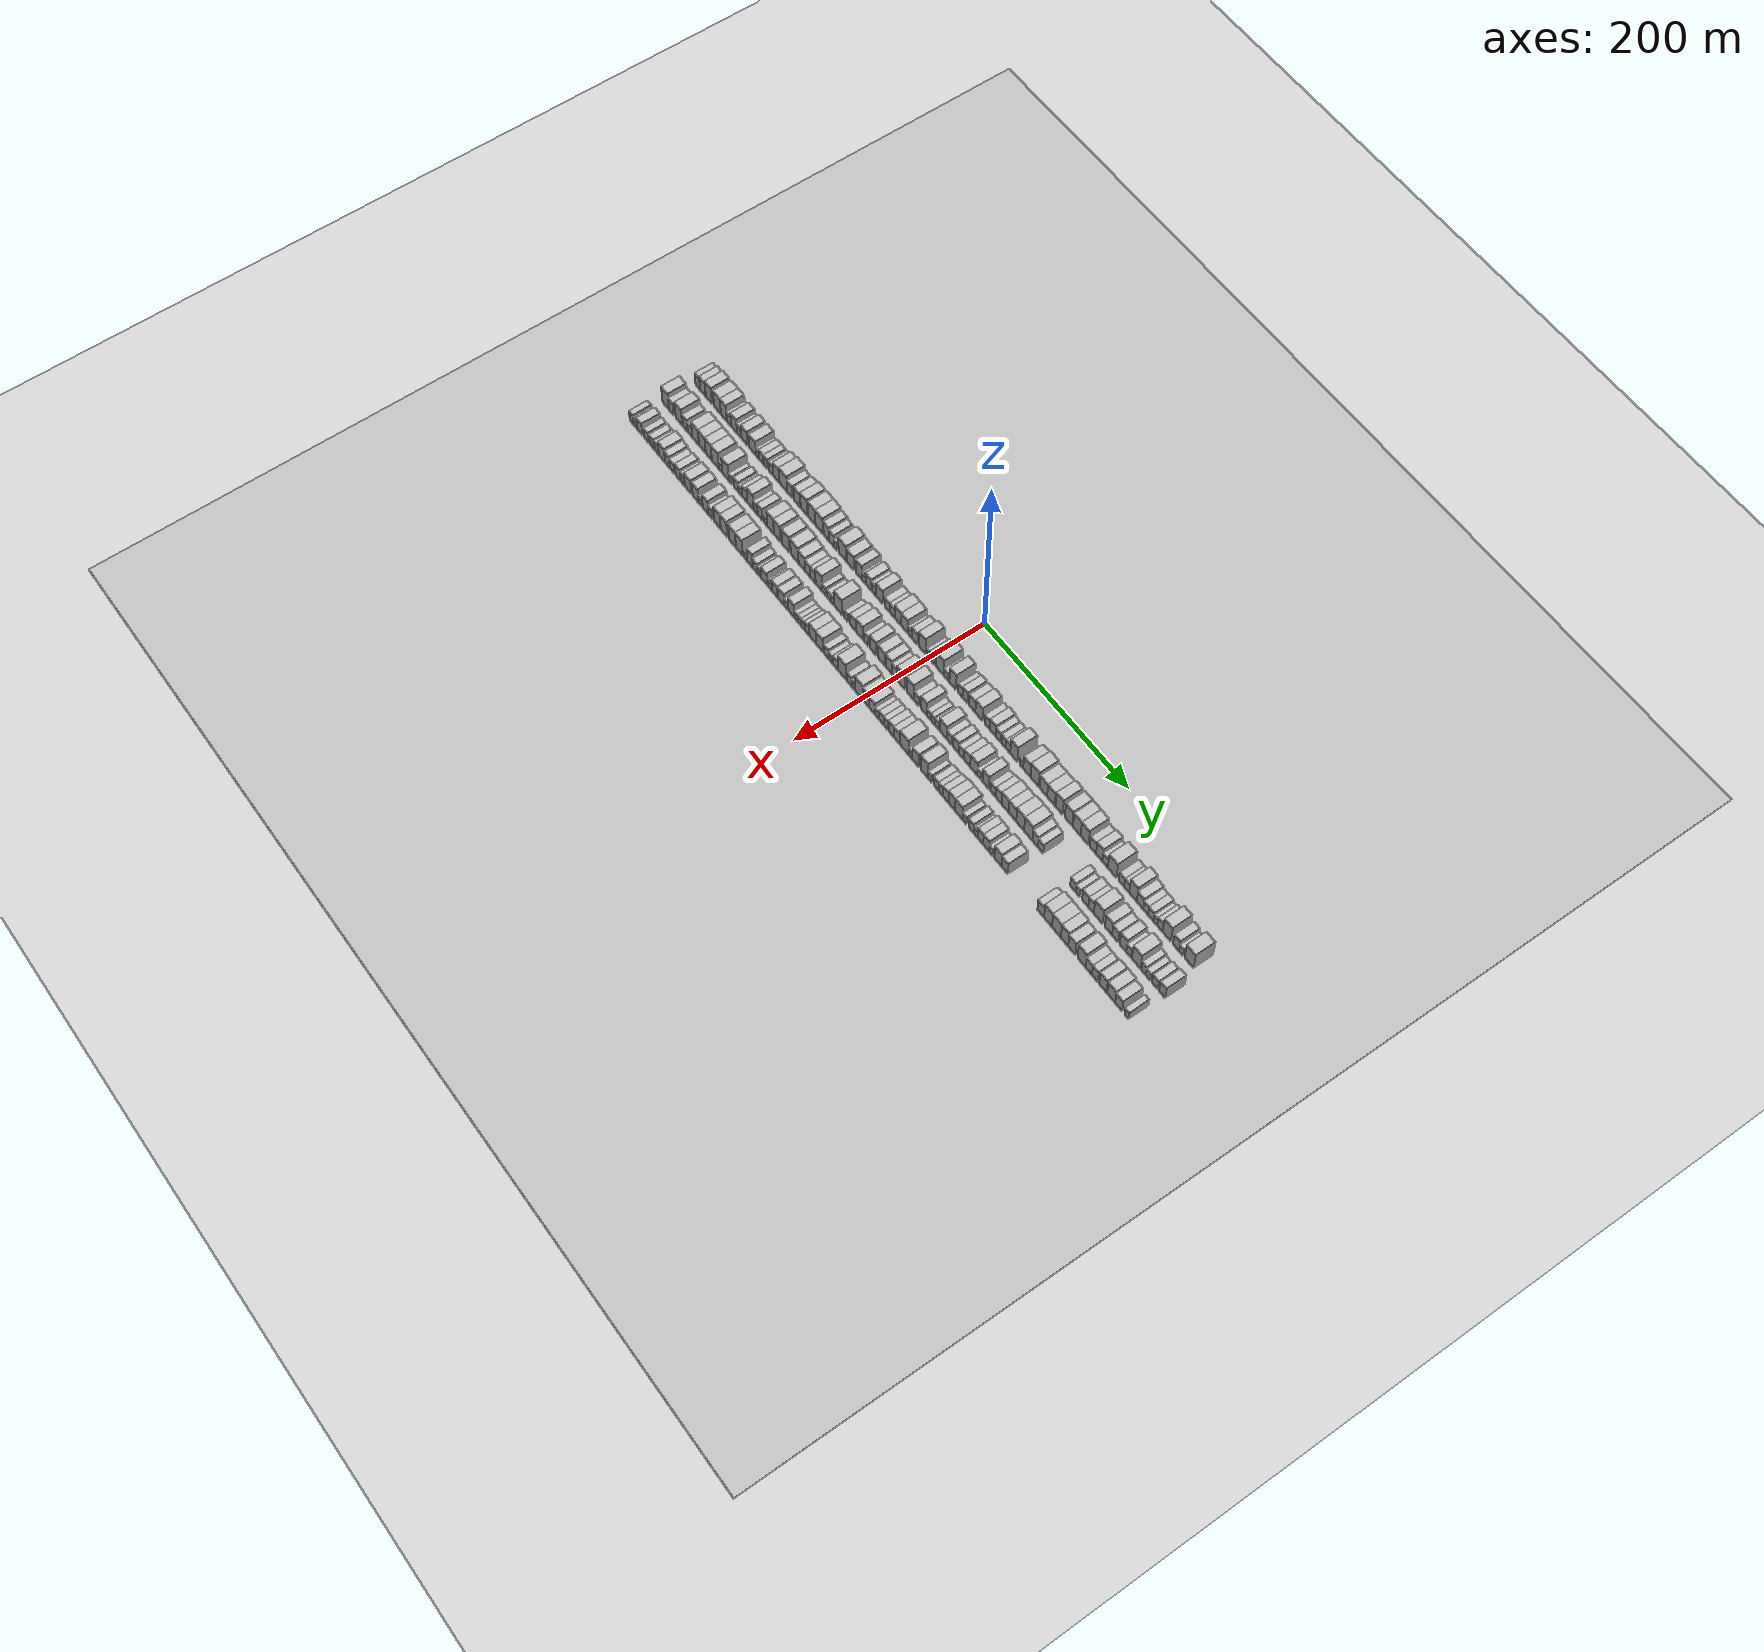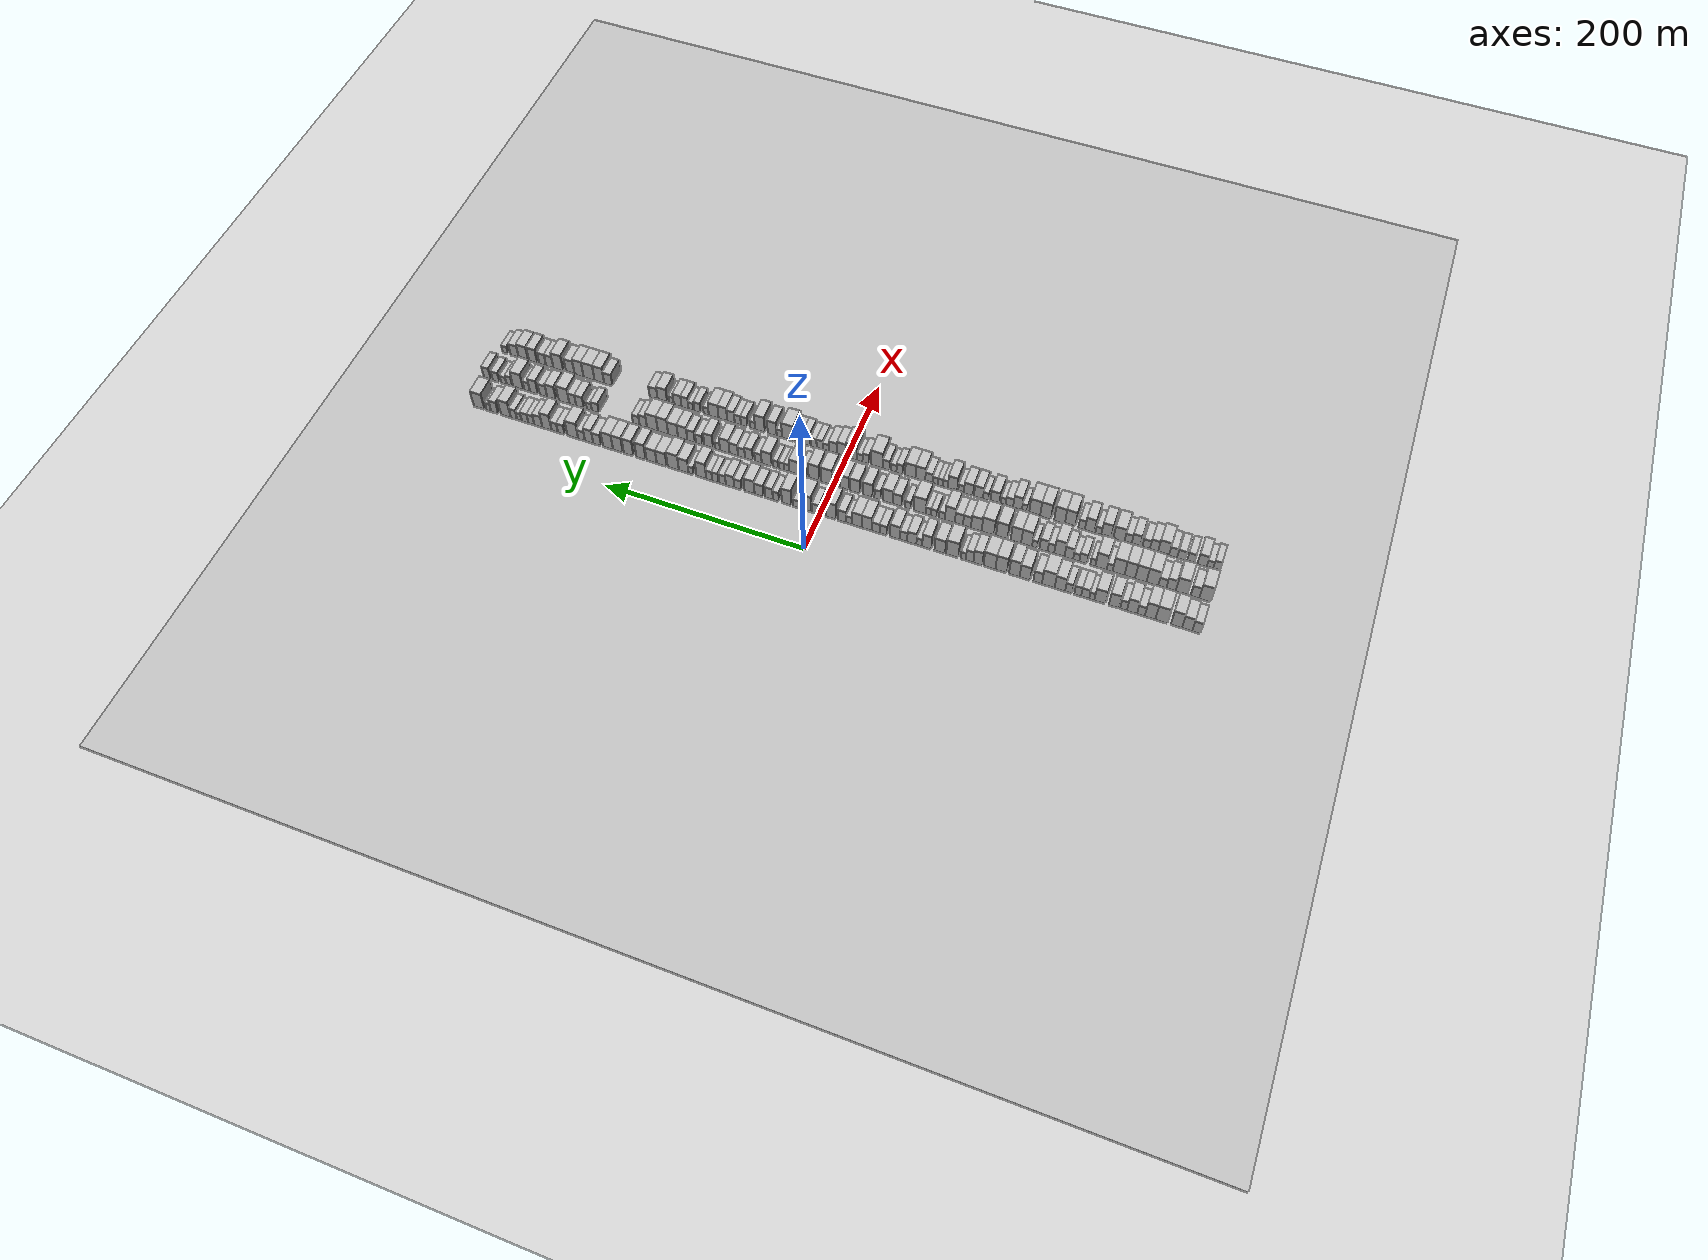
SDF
<?xml version="1.0" encoding="utf-8"?>

<sdf version="1.6">

   <world name="default">

      <gui fullscreen="0">

         <camera name="user_camera">

            <pose>-15 0 4.57585 0 0 0</pose>

            <view_controller>orbit</view_controller>

         </camera>

      </gui>

      <scene>

         <sky>

           <clouds>

             <speed>12</speed>

           </clouds>

         </sky>

         <ambient>0.4 0.4 0.4 1</ambient>

         <background>0.7 0.7 0.7 1</background>

         <shadows>1</shadows>

      </scene>

      <gravity>0 0 -9.8066</gravity>

      <magnetic_field>6e-06 2.3e-05 -4.2e-05</magnetic_field>

      <physics default="0" name="default_physics" type="ode">

         <ode>

            <solver>

               <type>quick</type>

               <iters>10</iters>

               <sor>1.0</sor>

               <use_dynamic_moi_rescaling>0</use_dynamic_moi_rescaling>

            </solver>

            <constraints>

               <cfm>0</cfm>

               <erp>0.2</erp>

               <contact_max_correcting_vel>100</contact_max_correcting_vel>

               <contact_surface_layer>0.001</contact_surface_layer>

            </constraints>

         </ode>

         <max_step_size>0.004</max_step_size>

         <real_time_factor>1</real_time_factor>

         <real_time_update_rate>250</real_time_update_rate>

      </physics>

      <light name="sun" type="directional">

         <cast_shadows>1</cast_shadows>

         <pose>0 0 10 0 0 0</pose>

         <diffuse>0.8 0.8 0.8 1</diffuse>

         <specular>0.2 0.2 0.2 1</specular>

         <attenuation>

            <range>1000</range>

            <constant>0.9</constant>

            <linear>0.01</linear>

            <quadratic>0.001</quadratic>

         </attenuation>

         <direction>-0.5 0.1 -0.9</direction>

      </light>

      <include>

         <name>ground_plane_1</name>

         <uri>model://HANNAS_ground_plane</uri>

         <pose>0 0 0  0 0 0</pose>

      </include>

      <include>

         <name>ground_plane_2</name>

         <uri>model://HANNAS_ground_plane</uri>

         <pose>100 0 0  0 0 0</pose>

      </include>

      <model name="building_1">

         <static>1</static>

         <pose frame="">50.0000 -355.2860 0 0.000000 0.000000 0.000000</pose>

         <link name="link">

            <pose frame="">0 0 9.00 0 0 0</pose>

            <collision name="collision">

               <geometry>

                  <box>

                     <size>20.0000 7.4280 18.0000</size>

                  </box>

               </geometry>

               <max_contacts>10</max_contacts>

               <surface>

                  <contact>

                     <ode/>

                  </contact>

                  <bounce/>

                  <friction>

                     <torsional>

                        <ode/>

                     </torsional>

                     <ode/>

                  </friction>

               </surface>

            </collision>

            <visual name="visual">

               <cast_shadows>0</cast_shadows>

               <geometry>

                  <box>

                     <size>20.0000 7.4280 18.0000</size>

                  </box>

               </geometry>

               <material>

                  <script>

                     <uri>model://HANNAS_wall/materials/scripts</uri>

                     <uri>model://HANNAS_wall/materials/textures</uri>

                     <name>vrc/HANNAS_wall</name>

                  </script>

               </material>

            </visual>

            <self_collide>0</self_collide>

            <enable_wind>0</enable_wind>

            <kinematic>0</kinematic>

         </link>

      </model>

      <model name="building_2">

         <static>1</static>

         <pose frame="">50.0000 -346.9435 0 0.000000 0.000000 0.000000</pose>

         <link name="link">

            <pose frame="">0 0 10.50 0 0 0</pose>

            <collision name="collision">

               <geometry>

                  <box>

                     <size>20.0000 9.2570 21.0000</size>

                  </box>

               </geometry>

               <max_contacts>10</max_contacts>

               <surface>

                  <contact>

                     <ode/>

                  </contact>

                  <bounce/>

                  <friction>

                     <torsional>

                        <ode/>

                     </torsional>

                     <ode/>

                  </friction>

               </surface>

            </collision>

            <visual name="visual">

               <cast_shadows>0</cast_shadows>

               <geometry>

                  <box>

                     <size>20.0000 9.2570 21.0000</size>

                  </box>

               </geometry>

               <material>

                  <script>

                     <uri>model://HANNAS_wall/materials/scripts</uri>

                     <uri>model://HANNAS_wall/materials/textures</uri>

                     <name>vrc/HANNAS_wall</name>

                  </script>

               </material>

            </visual>

            <self_collide>0</self_collide>

            <enable_wind>0</enable_wind>

            <kinematic>0</kinematic>

         </link>

      </model>

      <model name="building_3">

         <static>1</static>

         <pose frame="">50.0000 -337.2721 0 0.000000 0.000000 0.000000</pose>

         <link name="link">

            <pose frame="">0 0 12.00 0 0 0</pose>

            <collision name="collision">

               <geometry>

                  <box>

                     <size>20.0000 10.0858 24.0000</size>

                  </box>

               </geometry>

               <max_contacts>10</max_contacts>

               <surface>

                  <contact>

                     <ode/>

                  </contact>

                  <bounce/>

                  <friction>

                     <torsional>

                        <ode/>

                     </torsional>

                     <ode/>

                  </friction>

               </surface>

            </collision>

            <visual name="visual">

               <cast_shadows>0</cast_shadows>

               <geometry>

                  <box>

                     <size>20.0000 10.0858 24.0000</size>

                  </box>

               </geometry>

               <material>

                  <script>

                     <uri>model://HANNAS_wall/materials/scripts</uri>

                     <uri>model://HANNAS_wall/materials/textures</uri>

                     <name>vrc/HANNAS_wall</name>

                  </script>

               </material>

            </visual>

            <self_collide>0</self_collide>

            <enable_wind>0</enable_wind>

            <kinematic>0</kinematic>

         </link>

      </model>

      <model name="building_4">

         <static>1</static>

         <pose frame="">50.0000 -323.6632 0 0.000000 0.000000 0.000000</pose>

         <link name="link">

            <pose frame="">0 0 12.00 0 0 0</pose>

            <collision name="collision">

               <geometry>

                  <box>

                     <size>20.0000 11.1321 24.0000</size>

                  </box>

               </geometry>

               <max_contacts>10</max_contacts>

               <surface>

                  <contact>

                     <ode/>

                  </contact>

                  <bounce/>

                  <friction>

                     <torsional>

                        <ode/>

                     </torsional>

                     <ode/>

                  </friction>

               </surface>

            </collision>

            <visual name="visual">

               <cast_shadows>0</cast_shadows>

               <geometry>

                  <box>

                     <size>20.0000 11.1321 24.0000</size>

                  </box>

               </geometry>

               <material>

                  <script>

                     <uri>model://HANNAS_wall/materials/scripts</uri>

                     <uri>model://HANNAS_wall/materials/textures</uri>

                     <name>vrc/HANNAS_wall</name>

                  </script>

               </material>

            </visual>

            <self_collide>0</self_collide>

            <enable_wind>0</enable_wind>

            <kinematic>0</kinematic>

         </link>

      </model>

      <model name="building_5">

         <static>1</static>

         <pose frame="">50.0000 -313.2683 0 0.000000 0.000000 0.000000</pose>

         <link name="link">

            <pose frame="">0 0 12.00 0 0 0</pose>

            <collision name="collision">

               <geometry>

                  <box>

                     <size>20.0000 9.6578 24.0000</size>

                  </box>

               </geometry>

               <max_contacts>10</max_contacts>

               <surface>

                  <contact>

                     <ode/>

                  </contact>

                  <bounce/>

                  <friction>

                     <torsional>

                        <ode/>

                     </torsional>

                     <ode/>

                  </friction>

               </surface>

            </collision>

            <visual name="visual">

               <cast_shadows>0</cast_shadows>

               <geometry>

                  <box>

                     <size>20.0000 9.6578 24.0000</size>

                  </box>

               </geometry>

               <material>

                  <script>

                     <uri>model://HANNAS_wall/materials/scripts</uri>

                     <uri>model://HANNAS_wall/materials/textures</uri>

                     <name>vrc/HANNAS_wall</name>

                  </script>

               </material>

            </visual>

            <self_collide>0</self_collide>

            <enable_wind>0</enable_wind>

            <kinematic>0</kinematic>

         </link>

      </model>

      <model name="building_6">

         <static>1</static>

         <pose frame="">50.0000 -304.9249 0 0.000000 0.000000 0.000000</pose>

         <link name="link">

            <pose frame="">0 0 7.50 0 0 0</pose>

            <collision name="collision">

               <geometry>

                  <box>

                     <size>20.0000 7.0290 15.0000</size>

                  </box>

               </geometry>

               <max_contacts>10</max_contacts>

               <surface>

                  <contact>

                     <ode/>

                  </contact>

                  <bounce/>

                  <friction>

                     <torsional>

                        <ode/>

                     </torsional>

                     <ode/>

                  </friction>

               </surface>

            </collision>

            <visual name="visual">

               <cast_shadows>0</cast_shadows>

               <geometry>

                  <box>

                     <size>20.0000 7.0290 15.0000</size>

                  </box>

               </geometry>

               <material>

                  <script>

                     <uri>model://HANNAS_wall/materials/scripts</uri>

                     <uri>model://HANNAS_wall/materials/textures</uri>

                     <name>vrc/HANNAS_wall</name>

                  </script>

               </material>

            </visual>

            <self_collide>0</self_collide>

            <enable_wind>0</enable_wind>

            <kinematic>0</kinematic>

         </link>

      </model>

      <model name="building_7">

         <static>1</static>

         <pose frame="">50.0000 -296.7540 0 0.000000 0.000000 0.000000</pose>

         <link name="link">

            <pose frame="">0 0 10.50 0 0 0</pose>

            <collision name="collision">

               <geometry>

                  <box>

                     <size>20.0000 9.3128 21.0000</size>

                  </box>

               </geometry>

               <max_contacts>10</max_contacts>

               <surface>

                  <contact>

                     <ode/>

                  </contact>

                  <bounce/>

                  <friction>

                     <torsional>

                        <ode/>

                     </torsional>

                     <ode/>

                  </friction>

               </surface>

            </collision>

            <visual name="visual">

               <cast_shadows>0</cast_shadows>

               <geometry>

                  <box>

                     <size>20.0000 9.3128 21.0000</size>

                  </box>

               </geometry>

               <material>

                  <script>

                     <uri>model://HANNAS_wall/materials/scripts</uri>

                     <uri>model://HANNAS_wall/materials/textures</uri>

                     <name>vrc/HANNAS_wall</name>

                  </script>

               </material>

            </visual>

            <self_collide>0</self_collide>

            <enable_wind>0</enable_wind>

            <kinematic>0</kinematic>

         </link>

      </model>

      <model name="building_8">

         <static>1</static>

         <pose frame="">50.0000 -289.0511 0 0.000000 0.000000 0.000000</pose>

         <link name="link">

            <pose frame="">0 0 7.50 0 0 0</pose>

            <collision name="collision">

               <geometry>

                  <box>

                     <size>20.0000 6.0931 15.0000</size>

                  </box>

               </geometry>

               <max_contacts>10</max_contacts>

               <surface>

                  <contact>

                     <ode/>

                  </contact>

                  <bounce/>

                  <friction>

                     <torsional>

                        <ode/>

                     </torsional>

                     <ode/>

                  </friction>

               </surface>

            </collision>

            <visual name="visual">

               <cast_shadows>0</cast_shadows>

               <geometry>

                  <box>

                     <size>20.0000 6.0931 15.0000</size>

                  </box>

               </geometry>

               <material>

                  <script>

                     <uri>model://HANNAS_wall/materials/scripts</uri>

                     <uri>model://HANNAS_wall/materials/textures</uri>

                     <name>vrc/HANNAS_wall</name>

                  </script>

               </material>

            </visual>

            <self_collide>0</self_collide>

            <enable_wind>0</enable_wind>

            <kinematic>0</kinematic>

         </link>

      </model>

      <model name="building_9">

         <static>1</static>

         <pose frame="">50.0000 -280.2438 0 0.000000 0.000000 0.000000</pose>

         <link name="link">

            <pose frame="">0 0 10.50 0 0 0</pose>

            <collision name="collision">

               <geometry>

                  <box>

                     <size>20.0000 9.5215 21.0000</size>

                  </box>

               </geometry>

               <max_contacts>10</max_contacts>

               <surface>

                  <contact>

                     <ode/>

                  </contact>

                  <bounce/>

                  <friction>

                     <torsional>

                        <ode/>

                     </torsional>

                     <ode/>

                  </friction>

               </surface>

            </collision>

            <visual name="visual">

               <cast_shadows>0</cast_shadows>

               <geometry>

                  <box>

                     <size>20.0000 9.5215 21.0000</size>

                  </box>

               </geometry>

               <material>

                  <script>

                     <uri>model://HANNAS_wall/materials/scripts</uri>

                     <uri>model://HANNAS_wall/materials/textures</uri>

                     <name>vrc/HANNAS_wall</name>

                  </script>

               </material>

            </visual>

            <self_collide>0</self_collide>

            <enable_wind>0</enable_wind>

            <kinematic>0</kinematic>

         </link>

      </model>

      <model name="building_10">

         <static>1</static>

         <pose frame="">50.0000 -267.3015 0 0.000000 0.000000 0.000000</pose>

         <link name="link">

            <pose frame="">0 0 10.50 0 0 0</pose>

            <collision name="collision">

               <geometry>

                  <box>

                     <size>20.0000 10.3630 21.0000</size>

                  </box>

               </geometry>

               <max_contacts>10</max_contacts>

               <surface>

                  <contact>

                     <ode/>

                  </contact>

                  <bounce/>

                  <friction>

                     <torsional>

                        <ode/>

                     </torsional>

                     <ode/>

                  </friction>

               </surface>

            </collision>

            <visual name="visual">

               <cast_shadows>0</cast_shadows>

               <geometry>

                  <box>

                     <size>20.0000 10.3630 21.0000</size>

                  </box>

               </geometry>

               <material>

                  <script>

                     <uri>model://HANNAS_wall/materials/scripts</uri>

                     <uri>model://HANNAS_wall/materials/textures</uri>

                     <name>vrc/HANNAS_wall</name>

                  </script>

               </material>

            </visual>

            <self_collide>0</self_collide>

            <enable_wind>0</enable_wind>

            <kinematic>0</kinematic>

         </link>

      </model>

      <model name="building_11">

         <static>1</static>

         <pose frame="">50.0000 -259.7067 0 0.000000 0.000000 0.000000</pose>

         <link name="link">

            <pose frame="">0 0 6.00 0 0 0</pose>

            <collision name="collision">

               <geometry>

                  <box>

                     <size>20.0000 4.8265 12.0000</size>

                  </box>

               </geometry>

               <max_contacts>10</max_contacts>

               <surface>

                  <contact>

                     <ode/>

                  </contact>

                  <bounce/>

                  <friction>

                     <torsional>

                        <ode/>

                     </torsional>

                     <ode/>

                  </friction>

               </surface>

            </collision>

            <visual name="visual">

               <cast_shadows>0</cast_shadows>

               <geometry>

                  <box>

                     <size>20.0000 4.8265 12.0000</size>

                  </box>

               </geometry>

               <material>

                  <script>

                     <uri>model://HANNAS_wall/materials/scripts</uri>

                     <uri>model://HANNAS_wall/materials/textures</uri>

                     <name>vrc/HANNAS_wall</name>

                  </script>

               </material>

            </visual>

            <self_collide>0</self_collide>

            <enable_wind>0</enable_wind>

            <kinematic>0</kinematic>

         </link>

      </model>

      <model name="building_12">

         <static>1</static>

         <pose frame="">50.0000 -253.6373 0 0.000000 0.000000 0.000000</pose>

         <link name="link">

            <pose frame="">0 0 7.50 0 0 0</pose>

            <collision name="collision">

               <geometry>

                  <box>

                     <size>20.0000 7.3124 15.0000</size>

                  </box>

               </geometry>

               <max_contacts>10</max_contacts>

               <surface>

                  <contact>

                     <ode/>

                  </contact>

                  <bounce/>

                  <friction>

                     <torsional>

                        <ode/>

                     </torsional>

                     <ode/>

                  </friction>

               </surface>

            </collision>

            <visual name="visual">

               <cast_shadows>0</cast_shadows>

               <geometry>

                  <box>

                     <size>20.0000 7.3124 15.0000</size>

                  </box>

               </geometry>

               <material>

                  <script>

                     <uri>model://HANNAS_wall/materials/scripts</uri>

                     <uri>model://HANNAS_wall/materials/textures</uri>

                     <name>vrc/HANNAS_wall</name>

                  </script>

               </material>

            </visual>

            <self_collide>0</self_collide>

            <enable_wind>0</enable_wind>

            <kinematic>0</kinematic>

         </link>

      </model>

      <model name="building_13">

         <static>1</static>

         <pose frame="">50.0000 -246.7971 0 0.000000 0.000000 0.000000</pose>

         <link name="link">

            <pose frame="">0 0 7.50 0 0 0</pose>

            <collision name="collision">

               <geometry>

                  <box>

                     <size>20.0000 6.3680 15.0000</size>

                  </box>

               </geometry>

               <max_contacts>10</max_contacts>

               <surface>

                  <contact>

                     <ode/>

                  </contact>

                  <bounce/>

                  <friction>

                     <torsional>

                        <ode/>

                     </torsional>

                     <ode/>

                  </friction>

               </surface>

            </collision>

            <visual name="visual">

               <cast_shadows>0</cast_shadows>

               <geometry>

                  <box>

                     <size>20.0000 6.3680 15.0000</size>

                  </box>

               </geometry>

               <material>

                  <script>

                     <uri>model://HANNAS_wall/materials/scripts</uri>

                     <uri>model://HANNAS_wall/materials/textures</uri>

                     <name>vrc/HANNAS_wall</name>

                  </script>

               </material>

            </visual>

            <self_collide>0</self_collide>

            <enable_wind>0</enable_wind>

            <kinematic>0</kinematic>

         </link>

      </model>

      <model name="building_14">

         <static>1</static>

         <pose frame="">50.0000 -238.3296 0 0.000000 0.000000 0.000000</pose>

         <link name="link">

            <pose frame="">0 0 7.50 0 0 0</pose>

            <collision name="collision">

               <geometry>

                  <box>

                     <size>20.0000 6.5668 15.0000</size>

                  </box>

               </geometry>

               <max_contacts>10</max_contacts>

               <surface>

                  <contact>

                     <ode/>

                  </contact>

                  <bounce/>

                  <friction>

                     <torsional>

                        <ode/>

                     </torsional>

                     <ode/>

                  </friction>

               </surface>

            </collision>

            <visual name="visual">

               <cast_shadows>0</cast_shadows>

               <geometry>

                  <box>

                     <size>20.0000 6.5668 15.0000</size>

                  </box>

               </geometry>

               <material>

                  <script>

                     <uri>model://HANNAS_wall/materials/scripts</uri>

                     <uri>model://HANNAS_wall/materials/textures</uri>

                     <name>vrc/HANNAS_wall</name>

                  </script>

               </material>

            </visual>

            <self_collide>0</self_collide>

            <enable_wind>0</enable_wind>

            <kinematic>0</kinematic>

         </link>

      </model>

      <model name="building_15">

         <static>1</static>

         <pose frame="">50.0000 -230.1281 0 0.000000 0.000000 0.000000</pose>

         <link name="link">

            <pose frame="">0 0 10.50 0 0 0</pose>

            <collision name="collision">

               <geometry>

                  <box>

                     <size>20.0000 9.8362 21.0000</size>

                  </box>

               </geometry>

               <max_contacts>10</max_contacts>

               <surface>

                  <contact>

                     <ode/>

                  </contact>

                  <bounce/>

                  <friction>

                     <torsional>

                        <ode/>

                     </torsional>

                     <ode/>

                  </friction>

               </surface>

            </collision>

            <visual name="visual">

               <cast_shadows>0</cast_shadows>

               <geometry>

                  <box>

                     <size>20.0000 9.8362 21.0000</size>

                  </box>

               </geometry>

               <material>

                  <script>

                     <uri>model://HANNAS_wall/materials/scripts</uri>

                     <uri>model://HANNAS_wall/materials/textures</uri>

                     <name>vrc/HANNAS_wall</name>

                  </script>

               </material>

            </visual>

            <self_collide>0</self_collide>

            <enable_wind>0</enable_wind>

            <kinematic>0</kinematic>

         </link>

      </model>

      <model name="building_16">

         <static>1</static>

         <pose frame="">50.0000 -219.2534 0 0.000000 0.000000 0.000000</pose>

         <link name="link">

            <pose frame="">0 0 12.00 0 0 0</pose>

            <collision name="collision">

               <geometry>

                  <box>

                     <size>20.0000 11.9132 24.0000</size>

                  </box>

               </geometry>

               <max_contacts>10</max_contacts>

               <surface>

                  <contact>

                     <ode/>

                  </contact>

                  <bounce/>

                  <friction>

                     <torsional>

                        <ode/>

                     </torsional>

                     <ode/>

                  </friction>

               </surface>

            </collision>

            <visual name="visual">

               <cast_shadows>0</cast_shadows>

               <geometry>

                  <box>

                     <size>20.0000 11.9132 24.0000</size>

                  </box>

               </geometry>

               <material>

                  <script>

                     <uri>model://HANNAS_wall/materials/scripts</uri>

                     <uri>model://HANNAS_wall/materials/textures</uri>

                     <name>vrc/HANNAS_wall</name>

                  </script>

               </material>

            </visual>

            <self_collide>0</self_collide>

            <enable_wind>0</enable_wind>

            <kinematic>0</kinematic>

         </link>

      </model>

      <model name="building_17">

         <static>1</static>

         <pose frame="">50.0000 -209.3277 0 0.000000 0.000000 0.000000</pose>

         <link name="link">

            <pose frame="">0 0 9.00 0 0 0</pose>

            <collision name="collision">

               <geometry>

                  <box>

                     <size>20.0000 7.9382 18.0000</size>

                  </box>

               </geometry>

               <max_contacts>10</max_contacts>

               <surface>

                  <contact>

                     <ode/>

                  </contact>

                  <bounce/>

                  <friction>

                     <torsional>

                        <ode/>

                     </torsional>

                     <ode/>

                  </friction>

               </surface>

            </collision>

            <visual name="visual">

               <cast_shadows>0</cast_shadows>

               <geometry>

                  <box>

                     <size>20.0000 7.9382 18.0000</size>

                  </box>

               </geometry>

               <material>

                  <script>

                     <uri>model://HANNAS_wall/materials/scripts</uri>

                     <uri>model://HANNAS_wall/materials/textures</uri>

                     <name>vrc/HANNAS_wall</name>

                  </script>

               </material>

            </visual>

            <self_collide>0</self_collide>

            <enable_wind>0</enable_wind>

            <kinematic>0</kinematic>

         </link>

      </model>

      <model name="building_18">

         <static>1</static>

         <pose frame="">50.0000 -197.3633 0 0.000000 0.000000 0.000000</pose>

         <link name="link">

            <pose frame="">0 0 10.50 0 0 0</pose>

            <collision name="collision">

               <geometry>

                  <box>

                     <size>20.0000 9.9906 21.0000</size>

                  </box>

               </geometry>

               <max_contacts>10</max_contacts>

               <surface>

                  <contact>

                     <ode/>

                  </contact>

                  <bounce/>

                  <friction>

                     <torsional>

                        <ode/>

                     </torsional>

                     <ode/>

                  </friction>

               </surface>

            </collision>

            <visual name="visual">

               <cast_shadows>0</cast_shadows>

               <geometry>

                  <box>

                     <size>20.0000 9.9906 21.0000</size>

                  </box>

               </geometry>

               <material>

                  <script>

                     <uri>model://HANNAS_wall/materials/scripts</uri>

                     <uri>model://HANNAS_wall/materials/textures</uri>

                     <name>vrc/HANNAS_wall</name>

                  </script>

               </material>

            </visual>

            <self_collide>0</self_collide>

            <enable_wind>0</enable_wind>

            <kinematic>0</kinematic>

         </link>

      </model>

      <model name="building_19">

         <static>1</static>

         <pose frame="">50.0000 -187.3950 0 0.000000 0.000000 0.000000</pose>

         <link name="link">

            <pose frame="">0 0 12.00 0 0 0</pose>

            <collision name="collision">

               <geometry>

                  <box>

                     <size>20.0000 9.9459 24.0000</size>

                  </box>

               </geometry>

               <max_contacts>10</max_contacts>

               <surface>

                  <contact>

                     <ode/>

                  </contact>

                  <bounce/>

                  <friction>

                     <torsional>

                        <ode/>

                     </torsional>

                     <ode/>

                  </friction>

               </surface>

            </collision>

            <visual name="visual">

               <cast_shadows>0</cast_shadows>

               <geometry>

                  <box>

                     <size>20.0000 9.9459 24.0000</size>

                  </box>

               </geometry>

               <material>

                  <script>

                     <uri>model://HANNAS_wall/materials/scripts</uri>

                     <uri>model://HANNAS_wall/materials/textures</uri>

                     <name>vrc/HANNAS_wall</name>

                  </script>

               </material>

            </visual>

            <self_collide>0</self_collide>

            <enable_wind>0</enable_wind>

            <kinematic>0</kinematic>

         </link>

      </model>

      <model name="building_20">

         <static>1</static>

         <pose frame="">50.0000 -174.9886 0 0.000000 0.000000 0.000000</pose>

         <link name="link">

            <pose frame="">0 0 12.00 0 0 0</pose>

            <collision name="collision">

               <geometry>

                  <box>

                     <size>20.0000 10.8670 24.0000</size>

                  </box>

               </geometry>

               <max_contacts>10</max_contacts>

               <surface>

                  <contact>

                     <ode/>

                  </contact>

                  <bounce/>

                  <friction>

                     <torsional>

                        <ode/>

                     </torsional>

                     <ode/>

                  </friction>

               </surface>

            </collision>

            <visual name="visual">

               <cast_shadows>0</cast_shadows>

               <geometry>

                  <box>

                     <size>20.0000 10.8670 24.0000</size>

                  </box>

               </geometry>

               <material>

                  <script>

                     <uri>model://HANNAS_wall/materials/scripts</uri>

                     <uri>model://HANNAS_wall/materials/textures</uri>

                     <name>vrc/HANNAS_wall</name>

                  </script>

               </material>

            </visual>

            <self_collide>0</self_collide>

            <enable_wind>0</enable_wind>

            <kinematic>0</kinematic>

         </link>

      </model>

      <model name="building_21">

         <static>1</static>

         <pose frame="">50.0000 -163.8630 0 0.000000 0.000000 0.000000</pose>

         <link name="link">

            <pose frame="">0 0 12.00 0 0 0</pose>

            <collision name="collision">

               <geometry>

                  <box>

                     <size>20.0000 11.3841 24.0000</size>

                  </box>

               </geometry>

               <max_contacts>10</max_contacts>

               <surface>

                  <contact>

                     <ode/>

                  </contact>

                  <bounce/>

                  <friction>

                     <torsional>

                        <ode/>

                     </torsional>

                     <ode/>

                  </friction>

               </surface>

            </collision>

            <visual name="visual">

               <cast_shadows>0</cast_shadows>

               <geometry>

                  <box>

                     <size>20.0000 11.3841 24.0000</size>

                  </box>

               </geometry>

               <material>

                  <script>

                     <uri>model://HANNAS_wall/materials/scripts</uri>

                     <uri>model://HANNAS_wall/materials/textures</uri>

                     <name>vrc/HANNAS_wall</name>

                  </script>

               </material>

            </visual>

            <self_collide>0</self_collide>

            <enable_wind>0</enable_wind>

            <kinematic>0</kinematic>

         </link>

      </model>

      <model name="building_22">

         <static>1</static>

         <pose frame="">50.0000 -152.8875 0 0.000000 0.000000 0.000000</pose>

         <link name="link">

            <pose frame="">0 0 10.50 0 0 0</pose>

            <collision name="collision">

               <geometry>

                  <box>

                     <size>20.0000 8.5671 21.0000</size>

                  </box>

               </geometry>

               <max_contacts>10</max_contacts>

               <surface>

                  <contact>

                     <ode/>

                  </contact>

                  <bounce/>

                  <friction>

                     <torsional>

                        <ode/>

                     </torsional>

                     <ode/>

                  </friction>

               </surface>

            </collision>

            <visual name="visual">

               <cast_shadows>0</cast_shadows>

               <geometry>

                  <box>

                     <size>20.0000 8.5671 21.0000</size>

                  </box>

               </geometry>

               <material>

                  <script>

                     <uri>model://HANNAS_wall/materials/scripts</uri>

                     <uri>model://HANNAS_wall/materials/textures</uri>

                     <name>vrc/HANNAS_wall</name>

                  </script>

               </material>

            </visual>

            <self_collide>0</self_collide>

            <enable_wind>0</enable_wind>

            <kinematic>0</kinematic>

         </link>

      </model>

      <model name="building_23">

         <static>1</static>

         <pose frame="">50.0000 -144.9525 0 0.000000 0.000000 0.000000</pose>

         <link name="link">

            <pose frame="">0 0 9.00 0 0 0</pose>

            <collision name="collision">

               <geometry>

                  <box>

                     <size>20.0000 7.3028 18.0000</size>

                  </box>

               </geometry>

               <max_contacts>10</max_contacts>

               <surface>

                  <contact>

                     <ode/>

                  </contact>

                  <bounce/>

                  <friction>

                     <torsional>

                        <ode/>

                     </torsional>

                     <ode/>

                  </friction>

               </surface>

            </collision>

            <visual name="visual">

               <cast_shadows>0</cast_shadows>

               <geometry>

                  <box>

                     <size>20.0000 7.3028 18.0000</size>

                  </box>

               </geometry>

               <material>

                  <script>

                     <uri>model://HANNAS_wall/materials/scripts</uri>

                     <uri>model://HANNAS_wall/materials/textures</uri>

                     <name>vrc/HANNAS_wall</name>

                  </script>

               </material>

            </visual>

            <self_collide>0</self_collide>

            <enable_wind>0</enable_wind>

            <kinematic>0</kinematic>

         </link>

      </model>

      <model name="building_24">

         <static>1</static>

         <pose frame="">50.0000 -138.8365 0 0.000000 0.000000 0.000000</pose>

         <link name="link">

            <pose frame="">0 0 6.00 0 0 0</pose>

            <collision name="collision">

               <geometry>

                  <box>

                     <size>20.0000 4.9293 12.0000</size>

                  </box>

               </geometry>

               <max_contacts>10</max_contacts>

               <surface>

                  <contact>

                     <ode/>

                  </contact>

                  <bounce/>

                  <friction>

                     <torsional>

                        <ode/>

                     </torsional>

                     <ode/>

                  </friction>

               </surface>

            </collision>

            <visual name="visual">

               <cast_shadows>0</cast_shadows>

               <geometry>

                  <box>

                     <size>20.0000 4.9293 12.0000</size>

                  </box>

               </geometry>

               <material>

                  <script>

                     <uri>model://HANNAS_wall/materials/scripts</uri>

                     <uri>model://HANNAS_wall/materials/textures</uri>

                     <name>vrc/HANNAS_wall</name>

                  </script>

               </material>

            </visual>

            <self_collide>0</self_collide>

            <enable_wind>0</enable_wind>

            <kinematic>0</kinematic>

         </link>

      </model>

      <model name="building_25">

         <static>1</static>

         <pose frame="">50.0000 -128.4378 0 0.000000 0.000000 0.000000</pose>

         <link name="link">

            <pose frame="">0 0 12.00 0 0 0</pose>

            <collision name="collision">

               <geometry>

                  <box>

                     <size>20.0000 11.8682 24.0000</size>

                  </box>

               </geometry>

               <max_contacts>10</max_contacts>

               <surface>

                  <contact>

                     <ode/>

                  </contact>

                  <bounce/>

                  <friction>

                     <torsional>

                        <ode/>

                     </torsional>

                     <ode/>

                  </friction>

               </surface>

            </collision>

            <visual name="visual">

               <cast_shadows>0</cast_shadows>

               <geometry>

                  <box>

                     <size>20.0000 11.8682 24.0000</size>

                  </box>

               </geometry>

               <material>

                  <script>

                     <uri>model://HANNAS_wall/materials/scripts</uri>

                     <uri>model://HANNAS_wall/materials/textures</uri>

                     <name>vrc/HANNAS_wall</name>

                  </script>

               </material>

            </visual>

            <self_collide>0</self_collide>

            <enable_wind>0</enable_wind>

            <kinematic>0</kinematic>

         </link>

      </model>

      <model name="building_26">

         <static>1</static>

         <pose frame="">50.0000 -116.3749 0 0.000000 0.000000 0.000000</pose>

         <link name="link">

            <pose frame="">0 0 10.50 0 0 0</pose>

            <collision name="collision">

               <geometry>

                  <box>

                     <size>20.0000 10.2575 21.0000</size>

                  </box>

               </geometry>

               <max_contacts>10</max_contacts>

               <surface>

                  <contact>

                     <ode/>

                  </contact>

                  <bounce/>

                  <friction>

                     <torsional>

                        <ode/>

                     </torsional>

                     <ode/>

                  </friction>

               </surface>

            </collision>

            <visual name="visual">

               <cast_shadows>0</cast_shadows>

               <geometry>

                  <box>

                     <size>20.0000 10.2575 21.0000</size>

                  </box>

               </geometry>

               <material>

                  <script>

                     <uri>model://HANNAS_wall/materials/scripts</uri>

                     <uri>model://HANNAS_wall/materials/textures</uri>

                     <name>vrc/HANNAS_wall</name>

                  </script>

               </material>

            </visual>

            <self_collide>0</self_collide>

            <enable_wind>0</enable_wind>

            <kinematic>0</kinematic>

         </link>

      </model>

      <model name="building_27">

         <static>1</static>

         <pose frame="">50.0000 -103.8052 0 0.000000 0.000000 0.000000</pose>

         <link name="link">

            <pose frame="">0 0 10.50 0 0 0</pose>

            <collision name="collision">

               <geometry>

                  <box>

                     <size>20.0000 8.8818 21.0000</size>

                  </box>

               </geometry>

               <max_contacts>10</max_contacts>

               <surface>

                  <contact>

                     <ode/>

                  </contact>

                  <bounce/>

                  <friction>

                     <torsional>

                        <ode/>

                     </torsional>

                     <ode/>

                  </friction>

               </surface>

            </collision>

            <visual name="visual">

               <cast_shadows>0</cast_shadows>

               <geometry>

                  <box>

                     <size>20.0000 8.8818 21.0000</size>

                  </box>

               </geometry>

               <material>

                  <script>

                     <uri>model://HANNAS_wall/materials/scripts</uri>

                     <uri>model://HANNAS_wall/materials/textures</uri>

                     <name>vrc/HANNAS_wall</name>

                  </script>

               </material>

            </visual>

            <self_collide>0</self_collide>

            <enable_wind>0</enable_wind>

            <kinematic>0</kinematic>

         </link>

      </model>

      <model name="building_28">

         <static>1</static>

         <pose frame="">50.0000 -96.5634 0 0.000000 0.000000 0.000000</pose>

         <link name="link">

            <pose frame="">0 0 6.00 0 0 0</pose>

            <collision name="collision">

               <geometry>

                  <box>

                     <size>20.0000 5.6019 12.0000</size>

                  </box>

               </geometry>

               <max_contacts>10</max_contacts>

               <surface>

                  <contact>

                     <ode/>

                  </contact>

                  <bounce/>

                  <friction>

                     <torsional>

                        <ode/>

                     </torsional>

                     <ode/>

                  </friction>

               </surface>

            </collision>

            <visual name="visual">

               <cast_shadows>0</cast_shadows>

               <geometry>

                  <box>

                     <size>20.0000 5.6019 12.0000</size>

                  </box>

               </geometry>

               <material>

                  <script>

                     <uri>model://HANNAS_wall/materials/scripts</uri>

                     <uri>model://HANNAS_wall/materials/textures</uri>

                     <name>vrc/HANNAS_wall</name>

                  </script>

               </material>

            </visual>

            <self_collide>0</self_collide>

            <enable_wind>0</enable_wind>

            <kinematic>0</kinematic>

         </link>

      </model>

      <model name="building_29">

         <static>1</static>

         <pose frame="">50.0000 -89.3069 0 0.000000 0.000000 0.000000</pose>

         <link name="link">

            <pose frame="">0 0 9.00 0 0 0</pose>

            <collision name="collision">

               <geometry>

                  <box>

                     <size>20.0000 8.9112 18.0000</size>

                  </box>

               </geometry>

               <max_contacts>10</max_contacts>

               <surface>

                  <contact>

                     <ode/>

                  </contact>

                  <bounce/>

                  <friction>

                     <torsional>

                        <ode/>

                     </torsional>

                     <ode/>

                  </friction>

               </surface>

            </collision>

            <visual name="visual">

               <cast_shadows>0</cast_shadows>

               <geometry>

                  <box>

                     <size>20.0000 8.9112 18.0000</size>

                  </box>

               </geometry>

               <material>

                  <script>

                     <uri>model://HANNAS_wall/materials/scripts</uri>

                     <uri>model://HANNAS_wall/materials/textures</uri>

                     <name>vrc/HANNAS_wall</name>

                  </script>

               </material>

            </visual>

            <self_collide>0</self_collide>

            <enable_wind>0</enable_wind>

            <kinematic>0</kinematic>

         </link>

      </model>

      <model name="building_30">

         <static>1</static>

         <pose frame="">50.0000 -81.3925 0 0.000000 0.000000 0.000000</pose>

         <link name="link">

            <pose frame="">0 0 7.50 0 0 0</pose>

            <collision name="collision">

               <geometry>

                  <box>

                     <size>20.0000 6.9176 15.0000</size>

                  </box>

               </geometry>

               <max_contacts>10</max_contacts>

               <surface>

                  <contact>

                     <ode/>

                  </contact>

                  <bounce/>

                  <friction>

                     <torsional>

                        <ode/>

                     </torsional>

                     <ode/>

                  </friction>

               </surface>

            </collision>

            <visual name="visual">

               <cast_shadows>0</cast_shadows>

               <geometry>

                  <box>

                     <size>20.0000 6.9176 15.0000</size>

                  </box>

               </geometry>

               <material>

                  <script>

                     <uri>model://HANNAS_wall/materials/scripts</uri>

                     <uri>model://HANNAS_wall/materials/textures</uri>

                     <name>vrc/HANNAS_wall</name>

                  </script>

               </material>

            </visual>

            <self_collide>0</self_collide>

            <enable_wind>0</enable_wind>

            <kinematic>0</kinematic>

         </link>

      </model>

      <model name="building_31">

         <static>1</static>

         <pose frame="">50.0000 -73.1015 0 0.000000 0.000000 0.000000</pose>

         <link name="link">

            <pose frame="">0 0 10.50 0 0 0</pose>

            <collision name="collision">

               <geometry>

                  <box>

                     <size>20.0000 9.6645 21.0000</size>

                  </box>

               </geometry>

               <max_contacts>10</max_contacts>

               <surface>

                  <contact>

                     <ode/>

                  </contact>

                  <bounce/>

                  <friction>

                     <torsional>

                        <ode/>

                     </torsional>

                     <ode/>

                  </friction>

               </surface>

            </collision>

            <visual name="visual">

               <cast_shadows>0</cast_shadows>

               <geometry>

                  <box>

                     <size>20.0000 9.6645 21.0000</size>

                  </box>

               </geometry>

               <material>

                  <script>

                     <uri>model://HANNAS_wall/materials/scripts</uri>

                     <uri>model://HANNAS_wall/materials/textures</uri>

                     <name>vrc/HANNAS_wall</name>

                  </script>

               </material>

            </visual>

            <self_collide>0</self_collide>

            <enable_wind>0</enable_wind>

            <kinematic>0</kinematic>

         </link>

      </model>

      <model name="building_32">

         <static>1</static>

         <pose frame="">50.0000 -61.6101 0 0.000000 0.000000 0.000000</pose>

         <link name="link">

            <pose frame="">0 0 7.50 0 0 0</pose>

            <collision name="collision">

               <geometry>

                  <box>

                     <size>20.0000 7.3183 15.0000</size>

                  </box>

               </geometry>

               <max_contacts>10</max_contacts>

               <surface>

                  <contact>

                     <ode/>

                  </contact>

                  <bounce/>

                  <friction>

                     <torsional>

                        <ode/>

                     </torsional>

                     <ode/>

                  </friction>

               </surface>

            </collision>

            <visual name="visual">

               <cast_shadows>0</cast_shadows>

               <geometry>

                  <box>

                     <size>20.0000 7.3183 15.0000</size>

                  </box>

               </geometry>

               <material>

                  <script>

                     <uri>model://HANNAS_wall/materials/scripts</uri>

                     <uri>model://HANNAS_wall/materials/textures</uri>

                     <name>vrc/HANNAS_wall</name>

                  </script>

               </material>

            </visual>

            <self_collide>0</self_collide>

            <enable_wind>0</enable_wind>

            <kinematic>0</kinematic>

         </link>

      </model>

      <model name="building_33">

         <static>1</static>

         <pose frame="">50.0000 -54.2513 0 0.000000 0.000000 0.000000</pose>

         <link name="link">

            <pose frame="">0 0 7.50 0 0 0</pose>

            <collision name="collision">

               <geometry>

                  <box>

                     <size>20.0000 7.3994 15.0000</size>

                  </box>

               </geometry>

               <max_contacts>10</max_contacts>

               <surface>

                  <contact>

                     <ode/>

                  </contact>

                  <bounce/>

                  <friction>

                     <torsional>

                        <ode/>

                     </torsional>

                     <ode/>

                  </friction>

               </surface>

            </collision>

            <visual name="visual">

               <cast_shadows>0</cast_shadows>

               <geometry>

                  <box>

                     <size>20.0000 7.3994 15.0000</size>

                  </box>

               </geometry>

               <material>

                  <script>

                     <uri>model://HANNAS_wall/materials/scripts</uri>

                     <uri>model://HANNAS_wall/materials/textures</uri>

                     <name>vrc/HANNAS_wall</name>

                  </script>

               </material>

            </visual>

            <self_collide>0</self_collide>

            <enable_wind>0</enable_wind>

            <kinematic>0</kinematic>

         </link>

      </model>

      <model name="building_34">

         <static>1</static>

         <pose frame="">50.0000 -45.5678 0 0.000000 0.000000 0.000000</pose>

         <link name="link">

            <pose frame="">0 0 10.50 0 0 0</pose>

            <collision name="collision">

               <geometry>

                  <box>

                     <size>20.0000 9.9676 21.0000</size>

                  </box>

               </geometry>

               <max_contacts>10</max_contacts>

               <surface>

                  <contact>

                     <ode/>

                  </contact>

                  <bounce/>

                  <friction>

                     <torsional>

                        <ode/>

                     </torsional>

                     <ode/>

                  </friction>

               </surface>

            </collision>

            <visual name="visual">

               <cast_shadows>0</cast_shadows>

               <geometry>

                  <box>

                     <size>20.0000 9.9676 21.0000</size>

                  </box>

               </geometry>

               <material>

                  <script>

                     <uri>model://HANNAS_wall/materials/scripts</uri>

                     <uri>model://HANNAS_wall/materials/textures</uri>

                     <name>vrc/HANNAS_wall</name>

                  </script>

               </material>

            </visual>

            <self_collide>0</self_collide>

            <enable_wind>0</enable_wind>

            <kinematic>0</kinematic>

         </link>

      </model>

      <model name="building_35">

         <static>1</static>

         <pose frame="">50.0000 -35.8391 0 0.000000 0.000000 0.000000</pose>

         <link name="link">

            <pose frame="">0 0 10.50 0 0 0</pose>

            <collision name="collision">

               <geometry>

                  <box>

                     <size>20.0000 9.4897 21.0000</size>

                  </box>

               </geometry>

               <max_contacts>10</max_contacts>

               <surface>

                  <contact>

                     <ode/>

                  </contact>

                  <bounce/>

                  <friction>

                     <torsional>

                        <ode/>

                     </torsional>

                     <ode/>

                  </friction>

               </surface>

            </collision>

            <visual name="visual">

               <cast_shadows>0</cast_shadows>

               <geometry>

                  <box>

                     <size>20.0000 9.4897 21.0000</size>

                  </box>

               </geometry>

               <material>

                  <script>

                     <uri>model://HANNAS_wall/materials/scripts</uri>

                     <uri>model://HANNAS_wall/materials/textures</uri>

                     <name>vrc/HANNAS_wall</name>

                  </script>

               </material>

            </visual>

            <self_collide>0</self_collide>

            <enable_wind>0</enable_wind>

            <kinematic>0</kinematic>

         </link>

      </model>

      <model name="building_36">

         <static>1</static>

         <pose frame="">50.0000 -28.1138 0 0.000000 0.000000 0.000000</pose>

         <link name="link">

            <pose frame="">0 0 6.00 0 0 0</pose>

            <collision name="collision">

               <geometry>

                  <box>

                     <size>20.0000 5.9609 12.0000</size>

                  </box>

               </geometry>

               <max_contacts>10</max_contacts>

               <surface>

                  <contact>

                     <ode/>

                  </contact>

                  <bounce/>

                  <friction>

                     <torsional>

                        <ode/>

                     </torsional>

                     <ode/>

                  </friction>

               </surface>

            </collision>

            <visual name="visual">

               <cast_shadows>0</cast_shadows>

               <geometry>

                  <box>

                     <size>20.0000 5.9609 12.0000</size>

                  </box>

               </geometry>

               <material>

                  <script>

                     <uri>model://HANNAS_wall/materials/scripts</uri>

                     <uri>model://HANNAS_wall/materials/textures</uri>

                     <name>vrc/HANNAS_wall</name>

                  </script>

               </material>

            </visual>

            <self_collide>0</self_collide>

            <enable_wind>0</enable_wind>

            <kinematic>0</kinematic>

         </link>

      </model>

      <model name="building_37">

         <static>1</static>

         <pose frame="">50.0000 -21.1449 0 0.000000 0.000000 0.000000</pose>

         <link name="link">

            <pose frame="">0 0 9.00 0 0 0</pose>

            <collision name="collision">

               <geometry>

                  <box>

                     <size>20.0000 7.9767 18.0000</size>

                  </box>

               </geometry>

               <max_contacts>10</max_contacts>

               <surface>

                  <contact>

                     <ode/>

                  </contact>

                  <bounce/>

                  <friction>

                     <torsional>

                        <ode/>

                     </torsional>

                     <ode/>

                  </friction>

               </surface>

            </collision>

            <visual name="visual">

               <cast_shadows>0</cast_shadows>

               <geometry>

                  <box>

                     <size>20.0000 7.9767 18.0000</size>

                  </box>

               </geometry>

               <material>

                  <script>

                     <uri>model://HANNAS_wall/materials/scripts</uri>

                     <uri>model://HANNAS_wall/materials/textures</uri>

                     <name>vrc/HANNAS_wall</name>

                  </script>

               </material>

            </visual>

            <self_collide>0</self_collide>

            <enable_wind>0</enable_wind>

            <kinematic>0</kinematic>

         </link>

      </model>

      <model name="building_38">

         <static>1</static>

         <pose frame="">50.0000 -10.3359 0 0.000000 0.000000 0.000000</pose>

         <link name="link">

            <pose frame="">0 0 12.00 0 0 0</pose>

            <collision name="collision">

               <geometry>

                  <box>

                     <size>20.0000 9.6413 24.0000</size>

                  </box>

               </geometry>

               <max_contacts>10</max_contacts>

               <surface>

                  <contact>

                     <ode/>

                  </contact>

                  <bounce/>

                  <friction>

                     <torsional>

                        <ode/>

                     </torsional>

                     <ode/>

                  </friction>

               </surface>

            </collision>

            <visual name="visual">

               <cast_shadows>0</cast_shadows>

               <geometry>

                  <box>

                     <size>20.0000 9.6413 24.0000</size>

                  </box>

               </geometry>

               <material>

                  <script>

                     <uri>model://HANNAS_wall/materials/scripts</uri>

                     <uri>model://HANNAS_wall/materials/textures</uri>

                     <name>vrc/HANNAS_wall</name>

                  </script>

               </material>

            </visual>

            <self_collide>0</self_collide>

            <enable_wind>0</enable_wind>

            <kinematic>0</kinematic>

         </link>

      </model>

      <model name="building_39">

         <static>1</static>

         <pose frame="">50.0000 -0.9894 0 0.000000 0.000000 0.000000</pose>

         <link name="link">

            <pose frame="">0 0 6.00 0 0 0</pose>

            <collision name="collision">

               <geometry>

                  <box>

                     <size>20.0000 5.0517 12.0000</size>

                  </box>

               </geometry>

               <max_contacts>10</max_contacts>

               <surface>

                  <contact>

                     <ode/>

                  </contact>

                  <bounce/>

                  <friction>

                     <torsional>

                        <ode/>

                     </torsional>

                     <ode/>

                  </friction>

               </surface>

            </collision>

            <visual name="visual">

               <cast_shadows>0</cast_shadows>

               <geometry>

                  <box>

                     <size>20.0000 5.0517 12.0000</size>

                  </box>

               </geometry>

               <material>

                  <script>

                     <uri>model://HANNAS_wall/materials/scripts</uri>

                     <uri>model://HANNAS_wall/materials/textures</uri>

                     <name>vrc/HANNAS_wall</name>

                  </script>

               </material>

            </visual>

            <self_collide>0</self_collide>

            <enable_wind>0</enable_wind>

            <kinematic>0</kinematic>

         </link>

      </model>

      <model name="building_40">

         <static>1</static>

         <pose frame="">50.0000 4.9429 0 0.000000 0.000000 0.000000</pose>

         <link name="link">

            <pose frame="">0 0 7.50 0 0 0</pose>

            <collision name="collision">

               <geometry>

                  <box>

                     <size>20.0000 6.8130 15.0000</size>

                  </box>

               </geometry>

               <max_contacts>10</max_contacts>

               <surface>

                  <contact>

                     <ode/>

                  </contact>

                  <bounce/>

                  <friction>

                     <torsional>

                        <ode/>

                     </torsional>

                     <ode/>

                  </friction>

               </surface>

            </collision>

            <visual name="visual">

               <cast_shadows>0</cast_shadows>

               <geometry>

                  <box>

                     <size>20.0000 6.8130 15.0000</size>

                  </box>

               </geometry>

               <material>

                  <script>

                     <uri>model://HANNAS_wall/materials/scripts</uri>

                     <uri>model://HANNAS_wall/materials/textures</uri>

                     <name>vrc/HANNAS_wall</name>

                  </script>

               </material>

            </visual>

            <self_collide>0</self_collide>

            <enable_wind>0</enable_wind>

            <kinematic>0</kinematic>

         </link>

      </model>

      <model name="building_41">

         <static>1</static>

         <pose frame="">50.0000 15.2436 0 0.000000 0.000000 0.000000</pose>

         <link name="link">

            <pose frame="">0 0 12.00 0 0 0</pose>

            <collision name="collision">

               <geometry>

                  <box>

                     <size>20.0000 11.7885 24.0000</size>

                  </box>

               </geometry>

               <max_contacts>10</max_contacts>

               <surface>

                  <contact>

                     <ode/>

                  </contact>

                  <bounce/>

                  <friction>

                     <torsional>

                        <ode/>

                     </torsional>

                     <ode/>

                  </friction>

               </surface>

            </collision>

            <visual name="visual">

               <cast_shadows>0</cast_shadows>

               <geometry>

                  <box>

                     <size>20.0000 11.7885 24.0000</size>

                  </box>

               </geometry>

               <material>

                  <script>

                     <uri>model://HANNAS_wall/materials/scripts</uri>

                     <uri>model://HANNAS_wall/materials/textures</uri>

                     <name>vrc/HANNAS_wall</name>

                  </script>

               </material>

            </visual>

            <self_collide>0</self_collide>

            <enable_wind>0</enable_wind>

            <kinematic>0</kinematic>

         </link>

      </model>

      <model name="building_42">

         <static>1</static>

         <pose frame="">50.0000 24.1355 0 0.000000 0.000000 0.000000</pose>

         <link name="link">

            <pose frame="">0 0 6.00 0 0 0</pose>

            <collision name="collision">

               <geometry>

                  <box>

                     <size>20.0000 5.9953 12.0000</size>

                  </box>

               </geometry>

               <max_contacts>10</max_contacts>

               <surface>

                  <contact>

                     <ode/>

                  </contact>

                  <bounce/>

                  <friction>

                     <torsional>

                        <ode/>

                     </torsional>

                     <ode/>

                  </friction>

               </surface>

            </collision>

            <visual name="visual">

               <cast_shadows>0</cast_shadows>

               <geometry>

                  <box>

                     <size>20.0000 5.9953 12.0000</size>

                  </box>

               </geometry>

               <material>

                  <script>

                     <uri>model://HANNAS_wall/materials/scripts</uri>

                     <uri>model://HANNAS_wall/materials/textures</uri>

                     <name>vrc/HANNAS_wall</name>

                  </script>

               </material>

            </visual>

            <self_collide>0</self_collide>

            <enable_wind>0</enable_wind>

            <kinematic>0</kinematic>

         </link>

      </model>

      <model name="building_43">

         <static>1</static>

         <pose frame="">50.0000 33.9502 0 0.000000 0.000000 0.000000</pose>

         <link name="link">

            <pose frame="">0 0 12.00 0 0 0</pose>

            <collision name="collision">

               <geometry>

                  <box>

                     <size>20.0000 9.6340 24.0000</size>

                  </box>

               </geometry>

               <max_contacts>10</max_contacts>

               <surface>

                  <contact>

                     <ode/>

                  </contact>

                  <bounce/>

                  <friction>

                     <torsional>

                        <ode/>

                     </torsional>

                     <ode/>

                  </friction>

               </surface>

            </collision>

            <visual name="visual">

               <cast_shadows>0</cast_shadows>

               <geometry>

                  <box>

                     <size>20.0000 9.6340 24.0000</size>

                  </box>

               </geometry>

               <material>

                  <script>

                     <uri>model://HANNAS_wall/materials/scripts</uri>

                     <uri>model://HANNAS_wall/materials/textures</uri>

                     <name>vrc/HANNAS_wall</name>

                  </script>

               </material>

            </visual>

            <self_collide>0</self_collide>

            <enable_wind>0</enable_wind>

            <kinematic>0</kinematic>

         </link>

      </model>

      <model name="building_44">

         <static>1</static>

         <pose frame="">50.0000 44.7892 0 0.000000 0.000000 0.000000</pose>

         <link name="link">

            <pose frame="">0 0 7.50 0 0 0</pose>

            <collision name="collision">

               <geometry>

                  <box>

                     <size>20.0000 6.0442 15.0000</size>

                  </box>

               </geometry>

               <max_contacts>10</max_contacts>

               <surface>

                  <contact>

                     <ode/>

                  </contact>

                  <bounce/>

                  <friction>

                     <torsional>

                        <ode/>

                     </torsional>

                     <ode/>

                  </friction>

               </surface>

            </collision>

            <visual name="visual">

               <cast_shadows>0</cast_shadows>

               <geometry>

                  <box>

                     <size>20.0000 6.0442 15.0000</size>

                  </box>

               </geometry>

               <material>

                  <script>

                     <uri>model://HANNAS_wall/materials/scripts</uri>

                     <uri>model://HANNAS_wall/materials/textures</uri>

                     <name>vrc/HANNAS_wall</name>

                  </script>

               </material>

            </visual>

            <self_collide>0</self_collide>

            <enable_wind>0</enable_wind>

            <kinematic>0</kinematic>

         </link>

      </model>

      <model name="building_45">

         <static>1</static>

         <pose frame="">50.0000 51.5669 0 0.000000 0.000000 0.000000</pose>

         <link name="link">

            <pose frame="">0 0 9.00 0 0 0</pose>

            <collision name="collision">

               <geometry>

                  <box>

                     <size>20.0000 7.5112 18.0000</size>

                  </box>

               </geometry>

               <max_contacts>10</max_contacts>

               <surface>

                  <contact>

                     <ode/>

                  </contact>

                  <bounce/>

                  <friction>

                     <torsional>

                        <ode/>

                     </torsional>

                     <ode/>

                  </friction>

               </surface>

            </collision>

            <visual name="visual">

               <cast_shadows>0</cast_shadows>

               <geometry>

                  <box>

                     <size>20.0000 7.5112 18.0000</size>

                  </box>

               </geometry>

               <material>

                  <script>

                     <uri>model://HANNAS_wall/materials/scripts</uri>

                     <uri>model://HANNAS_wall/materials/textures</uri>

                     <name>vrc/HANNAS_wall</name>

                  </script>

               </material>

            </visual>

            <self_collide>0</self_collide>

            <enable_wind>0</enable_wind>

            <kinematic>0</kinematic>

         </link>

      </model>

      <model name="building_46">

         <static>1</static>

         <pose frame="">50.0000 61.7413 0 0.000000 0.000000 0.000000</pose>

         <link name="link">

            <pose frame="">0 0 9.00 0 0 0</pose>

            <collision name="collision">

               <geometry>

                  <box>

                     <size>20.0000 8.8376 18.0000</size>

                  </box>

               </geometry>

               <max_contacts>10</max_contacts>

               <surface>

                  <contact>

                     <ode/>

                  </contact>

                  <bounce/>

                  <friction>

                     <torsional>

                        <ode/>

                     </torsional>

                     <ode/>

                  </friction>

               </surface>

            </collision>

            <visual name="visual">

               <cast_shadows>0</cast_shadows>

               <geometry>

                  <box>

                     <size>20.0000 8.8376 18.0000</size>

                  </box>

               </geometry>

               <material>

                  <script>

                     <uri>model://HANNAS_wall/materials/scripts</uri>

                     <uri>model://HANNAS_wall/materials/textures</uri>

                     <name>vrc/HANNAS_wall</name>

                  </script>

               </material>

            </visual>

            <self_collide>0</self_collide>

            <enable_wind>0</enable_wind>

            <kinematic>0</kinematic>

         </link>

      </model>

      <model name="building_47">

         <static>1</static>

         <pose frame="">50.0000 71.2421 0 0.000000 0.000000 0.000000</pose>

         <link name="link">

            <pose frame="">0 0 10.50 0 0 0</pose>

            <collision name="collision">

               <geometry>

                  <box>

                     <size>20.0000 10.1640 21.0000</size>

                  </box>

               </geometry>

               <max_contacts>10</max_contacts>

               <surface>

                  <contact>

                     <ode/>

                  </contact>

                  <bounce/>

                  <friction>

                     <torsional>

                        <ode/>

                     </torsional>

                     <ode/>

                  </friction>

               </surface>

            </collision>

            <visual name="visual">

               <cast_shadows>0</cast_shadows>

               <geometry>

                  <box>

                     <size>20.0000 10.1640 21.0000</size>

                  </box>

               </geometry>

               <material>

                  <script>

                     <uri>model://HANNAS_wall/materials/scripts</uri>

                     <uri>model://HANNAS_wall/materials/textures</uri>

                     <name>vrc/HANNAS_wall</name>

                  </script>

               </material>

            </visual>

            <self_collide>0</self_collide>

            <enable_wind>0</enable_wind>

            <kinematic>0</kinematic>

         </link>

      </model>

      <model name="building_48">

         <static>1</static>

         <pose frame="">50.0000 83.0473 0 0.000000 0.000000 0.000000</pose>

         <link name="link">

            <pose frame="">0 0 7.50 0 0 0</pose>

            <collision name="collision">

               <geometry>

                  <box>

                     <size>20.0000 7.4463 15.0000</size>

                  </box>

               </geometry>

               <max_contacts>10</max_contacts>

               <surface>

                  <contact>

                     <ode/>

                  </contact>

                  <bounce/>

                  <friction>

                     <torsional>

                        <ode/>

                     </torsional>

                     <ode/>

                  </friction>

               </surface>

            </collision>

            <visual name="visual">

               <cast_shadows>0</cast_shadows>

               <geometry>

                  <box>

                     <size>20.0000 7.4463 15.0000</size>

                  </box>

               </geometry>

               <material>

                  <script>

                     <uri>model://HANNAS_wall/materials/scripts</uri>

                     <uri>model://HANNAS_wall/materials/textures</uri>

                     <name>vrc/HANNAS_wall</name>

                  </script>

               </material>

            </visual>

            <self_collide>0</self_collide>

            <enable_wind>0</enable_wind>

            <kinematic>0</kinematic>

         </link>

      </model>

      <model name="building_49">

         <static>1</static>

         <pose frame="">50.0000 91.0459 0 0.000000 0.000000 0.000000</pose>

         <link name="link">

            <pose frame="">0 0 9.00 0 0 0</pose>

            <collision name="collision">

               <geometry>

                  <box>

                     <size>20.0000 8.5509 18.0000</size>

                  </box>

               </geometry>

               <max_contacts>10</max_contacts>

               <surface>

                  <contact>

                     <ode/>

                  </contact>

                  <bounce/>

                  <friction>

                     <torsional>

                        <ode/>

                     </torsional>

                     <ode/>

                  </friction>

               </surface>

            </collision>

            <visual name="visual">

               <cast_shadows>0</cast_shadows>

               <geometry>

                  <box>

                     <size>20.0000 8.5509 18.0000</size>

                  </box>

               </geometry>

               <material>

                  <script>

                     <uri>model://HANNAS_wall/materials/scripts</uri>

                     <uri>model://HANNAS_wall/materials/textures</uri>

                     <name>vrc/HANNAS_wall</name>

                  </script>

               </material>

            </visual>

            <self_collide>0</self_collide>

            <enable_wind>0</enable_wind>

            <kinematic>0</kinematic>

         </link>

      </model>

      <model name="building_50">

         <static>1</static>

         <pose frame="">50.0000 98.6411 0 0.000000 0.000000 0.000000</pose>

         <link name="link">

            <pose frame="">0 0 7.50 0 0 0</pose>

            <collision name="collision">

               <geometry>

                  <box>

                     <size>20.0000 6.6396 15.0000</size>

                  </box>

               </geometry>

               <max_contacts>10</max_contacts>

               <surface>

                  <contact>

                     <ode/>

                  </contact>

                  <bounce/>

                  <friction>

                     <torsional>

                        <ode/>

                     </torsional>

                     <ode/>

                  </friction>

               </surface>

            </collision>

            <visual name="visual">

               <cast_shadows>0</cast_shadows>

               <geometry>

                  <box>

                     <size>20.0000 6.6396 15.0000</size>

                  </box>

               </geometry>

               <material>

                  <script>

                     <uri>model://HANNAS_wall/materials/scripts</uri>

                     <uri>model://HANNAS_wall/materials/textures</uri>

                     <name>vrc/HANNAS_wall</name>

                  </script>

               </material>

            </visual>

            <self_collide>0</self_collide>

            <enable_wind>0</enable_wind>

            <kinematic>0</kinematic>

         </link>

      </model>

      <model name="building_51">

         <static>1</static>

         <pose frame="">50.0000 106.1036 0 0.000000 0.000000 0.000000</pose>

         <link name="link">

            <pose frame="">0 0 7.50 0 0 0</pose>

            <collision name="collision">

               <geometry>

                  <box>

                     <size>20.0000 6.2854 15.0000</size>

                  </box>

               </geometry>

               <max_contacts>10</max_contacts>

               <surface>

                  <contact>

                     <ode/>

                  </contact>

                  <bounce/>

                  <friction>

                     <torsional>

                        <ode/>

                     </torsional>

                     <ode/>

                  </friction>

               </surface>

            </collision>

            <visual name="visual">

               <cast_shadows>0</cast_shadows>

               <geometry>

                  <box>

                     <size>20.0000 6.2854 15.0000</size>

                  </box>

               </geometry>

               <material>

                  <script>

                     <uri>model://HANNAS_wall/materials/scripts</uri>

                     <uri>model://HANNAS_wall/materials/textures</uri>

                     <name>vrc/HANNAS_wall</name>

                  </script>

               </material>

            </visual>

            <self_collide>0</self_collide>

            <enable_wind>0</enable_wind>

            <kinematic>0</kinematic>

         </link>

      </model>

      <model name="building_52">

         <static>1</static>

         <pose frame="">50.0000 112.2855 0 0.000000 0.000000 0.000000</pose>

         <link name="link">

            <pose frame="">0 0 7.50 0 0 0</pose>

            <collision name="collision">

               <geometry>

                  <box>

                     <size>20.0000 6.0785 15.0000</size>

                  </box>

               </geometry>

               <max_contacts>10</max_contacts>

               <surface>

                  <contact>

                     <ode/>

                  </contact>

                  <bounce/>

                  <friction>

                     <torsional>

                        <ode/>

                     </torsional>

                     <ode/>

                  </friction>

               </surface>

            </collision>

            <visual name="visual">

               <cast_shadows>0</cast_shadows>

               <geometry>

                  <box>

                     <size>20.0000 6.0785 15.0000</size>

                  </box>

               </geometry>

               <material>

                  <script>

                     <uri>model://HANNAS_wall/materials/scripts</uri>

                     <uri>model://HANNAS_wall/materials/textures</uri>

                     <name>vrc/HANNAS_wall</name>

                  </script>

               </material>

            </visual>

            <self_collide>0</self_collide>

            <enable_wind>0</enable_wind>

            <kinematic>0</kinematic>

         </link>

      </model>

      <model name="building_53">

         <static>1</static>

         <pose frame="">50.0000 120.3476 0 0.000000 0.000000 0.000000</pose>

         <link name="link">

            <pose frame="">0 0 12.00 0 0 0</pose>

            <collision name="collision">

               <geometry>

                  <box>

                     <size>20.0000 10.0456 24.0000</size>

                  </box>

               </geometry>

               <max_contacts>10</max_contacts>

               <surface>

                  <contact>

                     <ode/>

                  </contact>

                  <bounce/>

                  <friction>

                     <torsional>

                        <ode/>

                     </torsional>

                     <ode/>

                  </friction>

               </surface>

            </collision>

            <visual name="visual">

               <cast_shadows>0</cast_shadows>

               <geometry>

                  <box>

                     <size>20.0000 10.0456 24.0000</size>

                  </box>

               </geometry>

               <material>

                  <script>

                     <uri>model://HANNAS_wall/materials/scripts</uri>

                     <uri>model://HANNAS_wall/materials/textures</uri>

                     <name>vrc/HANNAS_wall</name>

                  </script>

               </material>

            </visual>

            <self_collide>0</self_collide>

            <enable_wind>0</enable_wind>

            <kinematic>0</kinematic>

         </link>

      </model>

      <model name="building_54">

         <static>1</static>

         <pose frame="">50.0000 130.8486 0 0.000000 0.000000 0.000000</pose>

         <link name="link">

            <pose frame="">0 0 6.00 0 0 0</pose>

            <collision name="collision">

               <geometry>

                  <box>

                     <size>20.0000 4.9565 12.0000</size>

                  </box>

               </geometry>

               <max_contacts>10</max_contacts>

               <surface>

                  <contact>

                     <ode/>

                  </contact>

                  <bounce/>

                  <friction>

                     <torsional>

                        <ode/>

                     </torsional>

                     <ode/>

                  </friction>

               </surface>

            </collision>

            <visual name="visual">

               <cast_shadows>0</cast_shadows>

               <geometry>

                  <box>

                     <size>20.0000 4.9565 12.0000</size>

                  </box>

               </geometry>

               <material>

                  <script>

                     <uri>model://HANNAS_wall/materials/scripts</uri>

                     <uri>model://HANNAS_wall/materials/textures</uri>

                     <name>vrc/HANNAS_wall</name>

                  </script>

               </material>

            </visual>

            <self_collide>0</self_collide>

            <enable_wind>0</enable_wind>

            <kinematic>0</kinematic>

         </link>

      </model>

      <model name="building_55">

         <static>1</static>

         <pose frame="">50.0000 138.3481 0 0.000000 0.000000 0.000000</pose>

         <link name="link">

            <pose frame="">0 0 10.50 0 0 0</pose>

            <collision name="collision">

               <geometry>

                  <box>

                     <size>20.0000 10.0426 21.0000</size>

                  </box>

               </geometry>

               <max_contacts>10</max_contacts>

               <surface>

                  <contact>

                     <ode/>

                  </contact>

                  <bounce/>

                  <friction>

                     <torsional>

                        <ode/>

                     </torsional>

                     <ode/>

                  </friction>

               </surface>

            </collision>

            <visual name="visual">

               <cast_shadows>0</cast_shadows>

               <geometry>

                  <box>

                     <size>20.0000 10.0426 21.0000</size>

                  </box>

               </geometry>

               <material>

                  <script>

                     <uri>model://HANNAS_wall/materials/scripts</uri>

                     <uri>model://HANNAS_wall/materials/textures</uri>

                     <name>vrc/HANNAS_wall</name>

                  </script>

               </material>

            </visual>

            <self_collide>0</self_collide>

            <enable_wind>0</enable_wind>

            <kinematic>0</kinematic>

         </link>

      </model>

      <model name="building_56">

         <static>1</static>

         <pose frame="">50.0000 149.1426 0 0.000000 0.000000 0.000000</pose>

         <link name="link">

            <pose frame="">0 0 12.00 0 0 0</pose>

            <collision name="collision">

               <geometry>

                  <box>

                     <size>20.0000 11.5463 24.0000</size>

                  </box>

               </geometry>

               <max_contacts>10</max_contacts>

               <surface>

                  <contact>

                     <ode/>

                  </contact>

                  <bounce/>

                  <friction>

                     <torsional>

                        <ode/>

                     </torsional>

                     <ode/>

                  </friction>

               </surface>

            </collision>

            <visual name="visual">

               <cast_shadows>0</cast_shadows>

               <geometry>

                  <box>

                     <size>20.0000 11.5463 24.0000</size>

                  </box>

               </geometry>

               <material>

                  <script>

                     <uri>model://HANNAS_wall/materials/scripts</uri>

                     <uri>model://HANNAS_wall/materials/textures</uri>

                     <name>vrc/HANNAS_wall</name>

                  </script>

               </material>

            </visual>

            <self_collide>0</self_collide>

            <enable_wind>0</enable_wind>

            <kinematic>0</kinematic>

         </link>

      </model>

      <model name="building_57">

         <static>1</static>

         <pose frame="">50.0000 161.1066 0 0.000000 0.000000 0.000000</pose>

         <link name="link">

            <pose frame="">0 0 10.50 0 0 0</pose>

            <collision name="collision">

               <geometry>

                  <box>

                     <size>20.0000 10.3818 21.0000</size>

                  </box>

               </geometry>

               <max_contacts>10</max_contacts>

               <surface>

                  <contact>

                     <ode/>

                  </contact>

                  <bounce/>

                  <friction>

                     <torsional>

                        <ode/>

                     </torsional>

                     <ode/>

                  </friction>

               </surface>

            </collision>

            <visual name="visual">

               <cast_shadows>0</cast_shadows>

               <geometry>

                  <box>

                     <size>20.0000 10.3818 21.0000</size>

                  </box>

               </geometry>

               <material>

                  <script>

                     <uri>model://HANNAS_wall/materials/scripts</uri>

                     <uri>model://HANNAS_wall/materials/textures</uri>

                     <name>vrc/HANNAS_wall</name>

                  </script>

               </material>

            </visual>

            <self_collide>0</self_collide>

            <enable_wind>0</enable_wind>

            <kinematic>0</kinematic>

         </link>

      </model>

      <model name="building_58">

         <static>1</static>

         <pose frame="">50.0000 171.5156 0 0.000000 0.000000 0.000000</pose>

         <link name="link">

            <pose frame="">0 0 10.50 0 0 0</pose>

            <collision name="collision">

               <geometry>

                  <box>

                     <size>20.0000 10.4361 21.0000</size>

                  </box>

               </geometry>

               <max_contacts>10</max_contacts>

               <surface>

                  <contact>

                     <ode/>

                  </contact>

                  <bounce/>

                  <friction>

                     <torsional>

                        <ode/>

                     </torsional>

                     <ode/>

                  </friction>

               </surface>

            </collision>

            <visual name="visual">

               <cast_shadows>0</cast_shadows>

               <geometry>

                  <box>

                     <size>20.0000 10.4361 21.0000</size>

                  </box>

               </geometry>

               <material>

                  <script>

                     <uri>model://HANNAS_wall/materials/scripts</uri>

                     <uri>model://HANNAS_wall/materials/textures</uri>

                     <name>vrc/HANNAS_wall</name>

                  </script>

               </material>

            </visual>

            <self_collide>0</self_collide>

            <enable_wind>0</enable_wind>

            <kinematic>0</kinematic>

         </link>

      </model>

      <model name="building_59">

         <static>1</static>

         <pose frame="">50.0000 182.5768 0 0.000000 0.000000 0.000000</pose>

         <link name="link">

            <pose frame="">0 0 12.00 0 0 0</pose>

            <collision name="collision">

               <geometry>

                  <box>

                     <size>20.0000 9.6863 24.0000</size>

                  </box>

               </geometry>

               <max_contacts>10</max_contacts>

               <surface>

                  <contact>

                     <ode/>

                  </contact>

                  <bounce/>

                  <friction>

                     <torsional>

                        <ode/>

                     </torsional>

                     <ode/>

                  </friction>

               </surface>

            </collision>

            <visual name="visual">

               <cast_shadows>0</cast_shadows>

               <geometry>

                  <box>

                     <size>20.0000 9.6863 24.0000</size>

                  </box>

               </geometry>

               <material>

                  <script>

                     <uri>model://HANNAS_wall/materials/scripts</uri>

                     <uri>model://HANNAS_wall/materials/textures</uri>

                     <name>vrc/HANNAS_wall</name>

                  </script>

               </material>

            </visual>

            <self_collide>0</self_collide>

            <enable_wind>0</enable_wind>

            <kinematic>0</kinematic>

         </link>

      </model>

      <model name="building_60">

         <static>1</static>

         <pose frame="">50.0000 195.4977 0 0.000000 0.000000 0.000000</pose>

         <link name="link">

            <pose frame="">0 0 12.00 0 0 0</pose>

            <collision name="collision">

               <geometry>

                  <box>

                     <size>20.0000 10.1554 24.0000</size>

                  </box>

               </geometry>

               <max_contacts>10</max_contacts>

               <surface>

                  <contact>

                     <ode/>

                  </contact>

                  <bounce/>

                  <friction>

                     <torsional>

                        <ode/>

                     </torsional>

                     <ode/>

                  </friction>

               </surface>

            </collision>

            <visual name="visual">

               <cast_shadows>0</cast_shadows>

               <geometry>

                  <box>

                     <size>20.0000 10.1554 24.0000</size>

                  </box>

               </geometry>

               <material>

                  <script>

                     <uri>model://HANNAS_wall/materials/scripts</uri>

                     <uri>model://HANNAS_wall/materials/textures</uri>

                     <name>vrc/HANNAS_wall</name>

                  </script>

               </material>

            </visual>

            <self_collide>0</self_collide>

            <enable_wind>0</enable_wind>

            <kinematic>0</kinematic>

         </link>

      </model>

      <model name="building_61">

         <static>1</static>

         <pose frame="">50.0000 206.7343 0 0.000000 0.000000 0.000000</pose>

         <link name="link">

            <pose frame="">0 0 12.00 0 0 0</pose>

            <collision name="collision">

               <geometry>

                  <box>

                     <size>20.0000 10.3178 24.0000</size>

                  </box>

               </geometry>

               <max_contacts>10</max_contacts>

               <surface>

                  <contact>

                     <ode/>

                  </contact>

                  <bounce/>

                  <friction>

                     <torsional>

                        <ode/>

                     </torsional>

                     <ode/>

                  </friction>

               </surface>

            </collision>

            <visual name="visual">

               <cast_shadows>0</cast_shadows>

               <geometry>

                  <box>

                     <size>20.0000 10.3178 24.0000</size>

                  </box>

               </geometry>

               <material>

                  <script>

                     <uri>model://HANNAS_wall/materials/scripts</uri>

                     <uri>model://HANNAS_wall/materials/textures</uri>

                     <name>vrc/HANNAS_wall</name>

                  </script>

               </material>

            </visual>

            <self_collide>0</self_collide>

            <enable_wind>0</enable_wind>

            <kinematic>0</kinematic>

         </link>

      </model>

      <model name="building_62">

         <static>1</static>

         <pose frame="">50.0000 217.1510 0 0.000000 0.000000 0.000000</pose>

         <link name="link">

            <pose frame="">0 0 12.00 0 0 0</pose>

            <collision name="collision">

               <geometry>

                  <box>

                     <size>20.0000 10.5157 24.0000</size>

                  </box>

               </geometry>

               <max_contacts>10</max_contacts>

               <surface>

                  <contact>

                     <ode/>

                  </contact>

                  <bounce/>

                  <friction>

                     <torsional>

                        <ode/>

                     </torsional>

                     <ode/>

                  </friction>

               </surface>

            </collision>

            <visual name="visual">

               <cast_shadows>0</cast_shadows>

               <geometry>

                  <box>

                     <size>20.0000 10.5157 24.0000</size>

                  </box>

               </geometry>

               <material>

                  <script>

                     <uri>model://HANNAS_wall/materials/scripts</uri>

                     <uri>model://HANNAS_wall/materials/textures</uri>

                     <name>vrc/HANNAS_wall</name>

                  </script>

               </material>

            </visual>

            <self_collide>0</self_collide>

            <enable_wind>0</enable_wind>

            <kinematic>0</kinematic>

         </link>

      </model>

      <model name="building_63">

         <static>1</static>

         <pose frame="">50.0000 228.5307 0 0.000000 0.000000 0.000000</pose>

         <link name="link">

            <pose frame="">0 0 9.00 0 0 0</pose>

            <collision name="collision">

               <geometry>

                  <box>

                     <size>20.0000 8.2437 18.0000</size>

                  </box>

               </geometry>

               <max_contacts>10</max_contacts>

               <surface>

                  <contact>

                     <ode/>

                  </contact>

                  <bounce/>

                  <friction>

                     <torsional>

                        <ode/>

                     </torsional>

                     <ode/>

                  </friction>

               </surface>

            </collision>

            <visual name="visual">

               <cast_shadows>0</cast_shadows>

               <geometry>

                  <box>

                     <size>20.0000 8.2437 18.0000</size>

                  </box>

               </geometry>

               <material>

                  <script>

                     <uri>model://HANNAS_wall/materials/scripts</uri>

                     <uri>model://HANNAS_wall/materials/textures</uri>

                     <name>vrc/HANNAS_wall</name>

                  </script>

               </material>

            </visual>

            <self_collide>0</self_collide>

            <enable_wind>0</enable_wind>

            <kinematic>0</kinematic>

         </link>

      </model>

      <model name="building_64">

         <static>1</static>

         <pose frame="">50.0000 236.9705 0 0.000000 0.000000 0.000000</pose>

         <link name="link">

            <pose frame="">0 0 10.50 0 0 0</pose>

            <collision name="collision">

               <geometry>

                  <box>

                     <size>20.0000 8.6359 21.0000</size>

                  </box>

               </geometry>

               <max_contacts>10</max_contacts>

               <surface>

                  <contact>

                     <ode/>

                  </contact>

                  <bounce/>

                  <friction>

                     <torsional>

                        <ode/>

                     </torsional>

                     <ode/>

                  </friction>

               </surface>

            </collision>

            <visual name="visual">

               <cast_shadows>0</cast_shadows>

               <geometry>

                  <box>

                     <size>20.0000 8.6359 21.0000</size>

                  </box>

               </geometry>

               <material>

                  <script>

                     <uri>model://HANNAS_wall/materials/scripts</uri>

                     <uri>model://HANNAS_wall/materials/textures</uri>

                     <name>vrc/HANNAS_wall</name>

                  </script>

               </material>

            </visual>

            <self_collide>0</self_collide>

            <enable_wind>0</enable_wind>

            <kinematic>0</kinematic>

         </link>

      </model>

      <model name="building_65">

         <static>1</static>

         <pose frame="">50.0000 244.8930 0 0.000000 0.000000 0.000000</pose>

         <link name="link">

            <pose frame="">0 0 7.50 0 0 0</pose>

            <collision name="collision">

               <geometry>

                  <box>

                     <size>20.0000 7.2090 15.0000</size>

                  </box>

               </geometry>

               <max_contacts>10</max_contacts>

               <surface>

                  <contact>

                     <ode/>

                  </contact>

                  <bounce/>

                  <friction>

                     <torsional>

                        <ode/>

                     </torsional>

                     <ode/>

                  </friction>

               </surface>

            </collision>

            <visual name="visual">

               <cast_shadows>0</cast_shadows>

               <geometry>

                  <box>

                     <size>20.0000 7.2090 15.0000</size>

                  </box>

               </geometry>

               <material>

                  <script>

                     <uri>model://HANNAS_wall/materials/scripts</uri>

                     <uri>model://HANNAS_wall/materials/textures</uri>

                     <name>vrc/HANNAS_wall</name>

                  </script>

               </material>

            </visual>

            <self_collide>0</self_collide>

            <enable_wind>0</enable_wind>

            <kinematic>0</kinematic>

         </link>

      </model>

      <model name="building_66">

         <static>1</static>

         <pose frame="">50.0000 254.2380 0 0.000000 0.000000 0.000000</pose>

         <link name="link">

            <pose frame="">0 0 12.00 0 0 0</pose>

            <collision name="collision">

               <geometry>

                  <box>

                     <size>20.0000 11.4810 24.0000</size>

                  </box>

               </geometry>

               <max_contacts>10</max_contacts>

               <surface>

                  <contact>

                     <ode/>

                  </contact>

                  <bounce/>

                  <friction>

                     <torsional>

                        <ode/>

                     </torsional>

                     <ode/>

                  </friction>

               </surface>

            </collision>

            <visual name="visual">

               <cast_shadows>0</cast_shadows>

               <geometry>

                  <box>

                     <size>20.0000 11.4810 24.0000</size>

                  </box>

               </geometry>

               <material>

                  <script>

                     <uri>model://HANNAS_wall/materials/scripts</uri>

                     <uri>model://HANNAS_wall/materials/textures</uri>

                     <name>vrc/HANNAS_wall</name>

                  </script>

               </material>

            </visual>

            <self_collide>0</self_collide>

            <enable_wind>0</enable_wind>

            <kinematic>0</kinematic>

         </link>

      </model>

      <model name="building_67">

         <static>1</static>

         <pose frame="">50.0000 266.5727 0 0.000000 0.000000 0.000000</pose>

         <link name="link">

            <pose frame="">0 0 7.50 0 0 0</pose>

            <collision name="collision">

               <geometry>

                  <box>

                     <size>20.0000 7.1884 15.0000</size>

                  </box>

               </geometry>

               <max_contacts>10</max_contacts>

               <surface>

                  <contact>

                     <ode/>

                  </contact>

                  <bounce/>

                  <friction>

                     <torsional>

                        <ode/>

                     </torsional>

                     <ode/>

                  </friction>

               </surface>

            </collision>

            <visual name="visual">

               <cast_shadows>0</cast_shadows>

               <geometry>

                  <box>

                     <size>20.0000 7.1884 15.0000</size>

                  </box>

               </geometry>

               <material>

                  <script>

                     <uri>model://HANNAS_wall/materials/scripts</uri>

                     <uri>model://HANNAS_wall/materials/textures</uri>

                     <name>vrc/HANNAS_wall</name>

                  </script>

               </material>

            </visual>

            <self_collide>0</self_collide>

            <enable_wind>0</enable_wind>

            <kinematic>0</kinematic>

         </link>

      </model>

      <model name="building_68">

         <static>1</static>

         <pose frame="">50.0000 273.5082 0 0.000000 0.000000 0.000000</pose>

         <link name="link">

            <pose frame="">0 0 7.50 0 0 0</pose>

            <collision name="collision">

               <geometry>

                  <box>

                     <size>20.0000 6.6827 15.0000</size>

                  </box>

               </geometry>

               <max_contacts>10</max_contacts>

               <surface>

                  <contact>

                     <ode/>

                  </contact>

                  <bounce/>

                  <friction>

                     <torsional>

                        <ode/>

                     </torsional>

                     <ode/>

                  </friction>

               </surface>

            </collision>

            <visual name="visual">

               <cast_shadows>0</cast_shadows>

               <geometry>

                  <box>

                     <size>20.0000 6.6827 15.0000</size>

                  </box>

               </geometry>

               <material>

                  <script>

                     <uri>model://HANNAS_wall/materials/scripts</uri>

                     <uri>model://HANNAS_wall/materials/textures</uri>

                     <name>vrc/HANNAS_wall</name>

                  </script>

               </material>

            </visual>

            <self_collide>0</self_collide>

            <enable_wind>0</enable_wind>

            <kinematic>0</kinematic>

         </link>

      </model>

      <model name="building_69">

         <static>1</static>

         <pose frame="">50.0000 281.7987 0 0.000000 0.000000 0.000000</pose>

         <link name="link">

            <pose frame="">0 0 12.00 0 0 0</pose>

            <collision name="collision">

               <geometry>

                  <box>

                     <size>20.0000 9.8983 24.0000</size>

                  </box>

               </geometry>

               <max_contacts>10</max_contacts>

               <surface>

                  <contact>

                     <ode/>

                  </contact>

                  <bounce/>

                  <friction>

                     <torsional>

                        <ode/>

                     </torsional>

                     <ode/>

                  </friction>

               </surface>

            </collision>

            <visual name="visual">

               <cast_shadows>0</cast_shadows>

               <geometry>

                  <box>

                     <size>20.0000 9.8983 24.0000</size>

                  </box>

               </geometry>

               <material>

                  <script>

                     <uri>model://HANNAS_wall/materials/scripts</uri>

                     <uri>model://HANNAS_wall/materials/textures</uri>

                     <name>vrc/HANNAS_wall</name>

                  </script>

               </material>

            </visual>

            <self_collide>0</self_collide>

            <enable_wind>0</enable_wind>

            <kinematic>0</kinematic>

         </link>

      </model>

      <model name="building_70">

         <static>1</static>

         <pose frame="">50.0000 291.0073 0 0.000000 0.000000 0.000000</pose>

         <link name="link">

            <pose frame="">0 0 9.00 0 0 0</pose>

            <collision name="collision">

               <geometry>

                  <box>

                     <size>20.0000 8.5188 18.0000</size>

                  </box>

               </geometry>

               <max_contacts>10</max_contacts>

               <surface>

                  <contact>

                     <ode/>

                  </contact>

                  <bounce/>

                  <friction>

                     <torsional>

                        <ode/>

                     </torsional>

                     <ode/>

                  </friction>

               </surface>

            </collision>

            <visual name="visual">

               <cast_shadows>0</cast_shadows>

               <geometry>

                  <box>

                     <size>20.0000 8.5188 18.0000</size>

                  </box>

               </geometry>

               <material>

                  <script>

                     <uri>model://HANNAS_wall/materials/scripts</uri>

                     <uri>model://HANNAS_wall/materials/textures</uri>

                     <name>vrc/HANNAS_wall</name>

                  </script>

               </material>

            </visual>

            <self_collide>0</self_collide>

            <enable_wind>0</enable_wind>

            <kinematic>0</kinematic>

         </link>

      </model>

      <model name="building_71">

         <static>1</static>

         <pose frame="">50.0000 298.4660 0 0.000000 0.000000 0.000000</pose>

         <link name="link">

            <pose frame="">0 0 7.50 0 0 0</pose>

            <collision name="collision">

               <geometry>

                  <box>

                     <size>20.0000 6.3985 15.0000</size>

                  </box>

               </geometry>

               <max_contacts>10</max_contacts>

               <surface>

                  <contact>

                     <ode/>

                  </contact>

                  <bounce/>

                  <friction>

                     <torsional>

                        <ode/>

                     </torsional>

                     <ode/>

                  </friction>

               </surface>

            </collision>

            <visual name="visual">

               <cast_shadows>0</cast_shadows>

               <geometry>

                  <box>

                     <size>20.0000 6.3985 15.0000</size>

                  </box>

               </geometry>

               <material>

                  <script>

                     <uri>model://HANNAS_wall/materials/scripts</uri>

                     <uri>model://HANNAS_wall/materials/textures</uri>

                     <name>vrc/HANNAS_wall</name>

                  </script>

               </material>

            </visual>

            <self_collide>0</self_collide>

            <enable_wind>0</enable_wind>

            <kinematic>0</kinematic>

         </link>

      </model>

      <model name="building_72">

         <static>1</static>

         <pose frame="">50.0000 305.2374 0 0.000000 0.000000 0.000000</pose>

         <link name="link">

            <pose frame="">0 0 7.50 0 0 0</pose>

            <collision name="collision">

               <geometry>

                  <box>

                     <size>20.0000 7.1443 15.0000</size>

                  </box>

               </geometry>

               <max_contacts>10</max_contacts>

               <surface>

                  <contact>

                     <ode/>

                  </contact>

                  <bounce/>

                  <friction>

                     <torsional>

                        <ode/>

                     </torsional>

                     <ode/>

                  </friction>

               </surface>

            </collision>

            <visual name="visual">

               <cast_shadows>0</cast_shadows>

               <geometry>

                  <box>

                     <size>20.0000 7.1443 15.0000</size>

                  </box>

               </geometry>

               <material>

                  <script>

                     <uri>model://HANNAS_wall/materials/scripts</uri>

                     <uri>model://HANNAS_wall/materials/textures</uri>

                     <name>vrc/HANNAS_wall</name>

                  </script>

               </material>

            </visual>

            <self_collide>0</self_collide>

            <enable_wind>0</enable_wind>

            <kinematic>0</kinematic>

         </link>

      </model>

      <model name="building_73">

         <static>1</static>

         <pose frame="">50.0000 311.3013 0 0.000000 0.000000 0.000000</pose>

         <link name="link">

            <pose frame="">0 0 6.00 0 0 0</pose>

            <collision name="collision">

               <geometry>

                  <box>

                     <size>20.0000 4.9836 12.0000</size>

                  </box>

               </geometry>

               <max_contacts>10</max_contacts>

               <surface>

                  <contact>

                     <ode/>

                  </contact>

                  <bounce/>

                  <friction>

                     <torsional>

                        <ode/>

                     </torsional>

                     <ode/>

                  </friction>

               </surface>

            </collision>

            <visual name="visual">

               <cast_shadows>0</cast_shadows>

               <geometry>

                  <box>

                     <size>20.0000 4.9836 12.0000</size>

                  </box>

               </geometry>

               <material>

                  <script>

                     <uri>model://HANNAS_wall/materials/scripts</uri>

                     <uri>model://HANNAS_wall/materials/textures</uri>

                     <name>vrc/HANNAS_wall</name>

                  </script>

               </material>

            </visual>

            <self_collide>0</self_collide>

            <enable_wind>0</enable_wind>

            <kinematic>0</kinematic>

         </link>

      </model>

      <model name="building_74">

         <static>1</static>

         <pose frame="">50.0000 317.2399 0 0.000000 0.000000 0.000000</pose>

         <link name="link">

            <pose frame="">0 0 7.50 0 0 0</pose>

            <collision name="collision">

               <geometry>

                  <box>

                     <size>20.0000 6.8936 15.0000</size>

                  </box>

               </geometry>

               <max_contacts>10</max_contacts>

               <surface>

                  <contact>

                     <ode/>

                  </contact>

                  <bounce/>

                  <friction>

                     <torsional>

                        <ode/>

                     </torsional>

                     <ode/>

                  </friction>

               </surface>

            </collision>

            <visual name="visual">

               <cast_shadows>0</cast_shadows>

               <geometry>

                  <box>

                     <size>20.0000 6.8936 15.0000</size>

                  </box>

               </geometry>

               <material>

                  <script>

                     <uri>model://HANNAS_wall/materials/scripts</uri>

                     <uri>model://HANNAS_wall/materials/textures</uri>

                     <name>vrc/HANNAS_wall</name>

                  </script>

               </material>

            </visual>

            <self_collide>0</self_collide>

            <enable_wind>0</enable_wind>

            <kinematic>0</kinematic>

         </link>

      </model>

      <model name="building_75">

         <static>1</static>

         <pose frame="">50.0000 325.9616 0 0.000000 0.000000 0.000000</pose>

         <link name="link">

            <pose frame="">0 0 12.00 0 0 0</pose>

            <collision name="collision">

               <geometry>

                  <box>

                     <size>20.0000 10.5498 24.0000</size>

                  </box>

               </geometry>

               <max_contacts>10</max_contacts>

               <surface>

                  <contact>

                     <ode/>

                  </contact>

                  <bounce/>

                  <friction>

                     <torsional>

                        <ode/>

                     </torsional>

                     <ode/>

                  </friction>

               </surface>

            </collision>

            <visual name="visual">

               <cast_shadows>0</cast_shadows>

               <geometry>

                  <box>

                     <size>20.0000 10.5498 24.0000</size>

                  </box>

               </geometry>

               <material>

                  <script>

                     <uri>model://HANNAS_wall/materials/scripts</uri>

                     <uri>model://HANNAS_wall/materials/textures</uri>

                     <name>vrc/HANNAS_wall</name>

                  </script>

               </material>

            </visual>

            <self_collide>0</self_collide>

            <enable_wind>0</enable_wind>

            <kinematic>0</kinematic>

         </link>

      </model>

      <model name="building_76">

         <static>1</static>

         <pose frame="">50.0000 338.0827 0 0.000000 0.000000 0.000000</pose>

         <link name="link">

            <pose frame="">0 0 9.00 0 0 0</pose>

            <collision name="collision">

               <geometry>

                  <box>

                     <size>20.0000 7.6923 18.0000</size>

                  </box>

               </geometry>

               <max_contacts>10</max_contacts>

               <surface>

                  <contact>

                     <ode/>

                  </contact>

                  <bounce/>

                  <friction>

                     <torsional>

                        <ode/>

                     </torsional>

                     <ode/>

                  </friction>

               </surface>

            </collision>

            <visual name="visual">

               <cast_shadows>0</cast_shadows>

               <geometry>

                  <box>

                     <size>20.0000 7.6923 18.0000</size>

                  </box>

               </geometry>

               <material>

                  <script>

                     <uri>model://HANNAS_wall/materials/scripts</uri>

                     <uri>model://HANNAS_wall/materials/textures</uri>

                     <name>vrc/HANNAS_wall</name>

                  </script>

               </material>

            </visual>

            <self_collide>0</self_collide>

            <enable_wind>0</enable_wind>

            <kinematic>0</kinematic>

         </link>

      </model>

      <model name="building_77">

         <static>1</static>

         <pose frame="">50.0000 344.5270 0 0.000000 0.000000 0.000000</pose>

         <link name="link">

            <pose frame="">0 0 6.00 0 0 0</pose>

            <collision name="collision">

               <geometry>

                  <box>

                     <size>20.0000 5.1963 12.0000</size>

                  </box>

               </geometry>

               <max_contacts>10</max_contacts>

               <surface>

                  <contact>

                     <ode/>

                  </contact>

                  <bounce/>

                  <friction>

                     <torsional>

                        <ode/>

                     </torsional>

                     <ode/>

                  </friction>

               </surface>

            </collision>

            <visual name="visual">

               <cast_shadows>0</cast_shadows>

               <geometry>

                  <box>

                     <size>20.0000 5.1963 12.0000</size>

                  </box>

               </geometry>

               <material>

                  <script>

                     <uri>model://HANNAS_wall/materials/scripts</uri>

                     <uri>model://HANNAS_wall/materials/textures</uri>

                     <name>vrc/HANNAS_wall</name>

                  </script>

               </material>

            </visual>

            <self_collide>0</self_collide>

            <enable_wind>0</enable_wind>

            <kinematic>0</kinematic>

         </link>

      </model>

      <model name="building_78">

         <static>1</static>

         <pose frame="">50.0000 354.9378 0 0.000000 0.000000 0.000000</pose>

         <link name="link">

            <pose frame="">0 0 12.00 0 0 0</pose>

            <collision name="collision">

               <geometry>

                  <box>

                     <size>20.0000 11.6253 24.0000</size>

                  </box>

               </geometry>

               <max_contacts>10</max_contacts>

               <surface>

                  <contact>

                     <ode/>

                  </contact>

                  <bounce/>

                  <friction>

                     <torsional>

                        <ode/>

                     </torsional>

                     <ode/>

                  </friction>

               </surface>

            </collision>

            <visual name="visual">

               <cast_shadows>0</cast_shadows>

               <geometry>

                  <box>

                     <size>20.0000 11.6253 24.0000</size>

                  </box>

               </geometry>

               <material>

                  <script>

                     <uri>model://HANNAS_wall/materials/scripts</uri>

                     <uri>model://HANNAS_wall/materials/textures</uri>

                     <name>vrc/HANNAS_wall</name>

                  </script>

               </material>

            </visual>

            <self_collide>0</self_collide>

            <enable_wind>0</enable_wind>

            <kinematic>0</kinematic>

         </link>

      </model>

      <model name="building_79">

         <static>1</static>

         <pose frame="">85.0000 -354.7068 0 0.000000 0.000000 0.000000</pose>

         <link name="link">

            <pose frame="">0 0 12.00 0 0 0</pose>

            <collision name="collision">

               <geometry>

                  <box>

                     <size>20.0000 10.5864 24.0000</size>

                  </box>

               </geometry>

               <max_contacts>10</max_contacts>

               <surface>

                  <contact>

                     <ode/>

                  </contact>

                  <bounce/>

                  <friction>

                     <torsional>

                        <ode/>

                     </torsional>

                     <ode/>

                  </friction>

               </surface>

            </collision>

            <visual name="visual">

               <cast_shadows>0</cast_shadows>

               <geometry>

                  <box>

                     <size>20.0000 10.5864 24.0000</size>

                  </box>

               </geometry>

               <material>

                  <script>

                     <uri>model://HANNAS_wall/materials/scripts</uri>

                     <uri>model://HANNAS_wall/materials/textures</uri>

                     <name>vrc/HANNAS_wall</name>

                  </script>

               </material>

            </visual>

            <self_collide>0</self_collide>

            <enable_wind>0</enable_wind>

            <kinematic>0</kinematic>

         </link>

      </model>

      <model name="building_80">

         <static>1</static>

         <pose frame="">85.0000 -345.4796 0 0.000000 0.000000 0.000000</pose>

         <link name="link">

            <pose frame="">0 0 9.00 0 0 0</pose>

            <collision name="collision">

               <geometry>

                  <box>

                     <size>20.0000 7.8680 18.0000</size>

                  </box>

               </geometry>

               <max_contacts>10</max_contacts>

               <surface>

                  <contact>

                     <ode/>

                  </contact>

                  <bounce/>

                  <friction>

                     <torsional>

                        <ode/>

                     </torsional>

                     <ode/>

                  </friction>

               </surface>

            </collision>

            <visual name="visual">

               <cast_shadows>0</cast_shadows>

               <geometry>

                  <box>

                     <size>20.0000 7.8680 18.0000</size>

                  </box>

               </geometry>

               <material>

                  <script>

                     <uri>model://HANNAS_wall/materials/scripts</uri>

                     <uri>model://HANNAS_wall/materials/textures</uri>

                     <name>vrc/HANNAS_wall</name>

                  </script>

               </material>

            </visual>

            <self_collide>0</self_collide>

            <enable_wind>0</enable_wind>

            <kinematic>0</kinematic>

         </link>

      </model>

      <model name="building_81">

         <static>1</static>

         <pose frame="">85.0000 -333.2357 0 0.000000 0.000000 0.000000</pose>

         <link name="link">

            <pose frame="">0 0 12.00 0 0 0</pose>

            <collision name="collision">

               <geometry>

                  <box>

                     <size>20.0000 10.6198 24.0000</size>

                  </box>

               </geometry>

               <max_contacts>10</max_contacts>

               <surface>

                  <contact>

                     <ode/>

                  </contact>

                  <bounce/>

                  <friction>

                     <torsional>

                        <ode/>

                     </torsional>

                     <ode/>

                  </friction>

               </surface>

            </collision>

            <visual name="visual">

               <cast_shadows>0</cast_shadows>

               <geometry>

                  <box>

                     <size>20.0000 10.6198 24.0000</size>

                  </box>

               </geometry>

               <material>

                  <script>

                     <uri>model://HANNAS_wall/materials/scripts</uri>

                     <uri>model://HANNAS_wall/materials/textures</uri>

                     <name>vrc/HANNAS_wall</name>

                  </script>

               </material>

            </visual>

            <self_collide>0</self_collide>

            <enable_wind>0</enable_wind>

            <kinematic>0</kinematic>

         </link>

      </model>

      <model name="building_82">

         <static>1</static>

         <pose frame="">85.0000 -323.0554 0 0.000000 0.000000 0.000000</pose>

         <link name="link">

            <pose frame="">0 0 9.00 0 0 0</pose>

            <collision name="collision">

               <geometry>

                  <box>

                     <size>20.0000 7.7408 18.0000</size>

                  </box>

               </geometry>

               <max_contacts>10</max_contacts>

               <surface>

                  <contact>

                     <ode/>

                  </contact>

                  <bounce/>

                  <friction>

                     <torsional>

                        <ode/>

                     </torsional>

                     <ode/>

                  </friction>

               </surface>

            </collision>

            <visual name="visual">

               <cast_shadows>0</cast_shadows>

               <geometry>

                  <box>

                     <size>20.0000 7.7408 18.0000</size>

                  </box>

               </geometry>

               <material>

                  <script>

                     <uri>model://HANNAS_wall/materials/scripts</uri>

                     <uri>model://HANNAS_wall/materials/textures</uri>

                     <name>vrc/HANNAS_wall</name>

                  </script>

               </material>

            </visual>

            <self_collide>0</self_collide>

            <enable_wind>0</enable_wind>

            <kinematic>0</kinematic>

         </link>

      </model>

      <model name="building_83">

         <static>1</static>

         <pose frame="">85.0000 -315.4797 0 0.000000 0.000000 0.000000</pose>

         <link name="link">

            <pose frame="">0 0 7.50 0 0 0</pose>

            <collision name="collision">

               <geometry>

                  <box>

                     <size>20.0000 7.4107 15.0000</size>

                  </box>

               </geometry>

               <max_contacts>10</max_contacts>

               <surface>

                  <contact>

                     <ode/>

                  </contact>

                  <bounce/>

                  <friction>

                     <torsional>

                        <ode/>

                     </torsional>

                     <ode/>

                  </friction>

               </surface>

            </collision>

            <visual name="visual">

               <cast_shadows>0</cast_shadows>

               <geometry>

                  <box>

                     <size>20.0000 7.4107 15.0000</size>

                  </box>

               </geometry>

               <material>

                  <script>

                     <uri>model://HANNAS_wall/materials/scripts</uri>

                     <uri>model://HANNAS_wall/materials/textures</uri>

                     <name>vrc/HANNAS_wall</name>

                  </script>

               </material>

            </visual>

            <self_collide>0</self_collide>

            <enable_wind>0</enable_wind>

            <kinematic>0</kinematic>

         </link>

      </model>

      <model name="building_84">

         <static>1</static>

         <pose frame="">85.0000 -306.3395 0 0.000000 0.000000 0.000000</pose>

         <link name="link">

            <pose frame="">0 0 12.00 0 0 0</pose>

            <collision name="collision">

               <geometry>

                  <box>

                     <size>20.0000 10.8697 24.0000</size>

                  </box>

               </geometry>

               <max_contacts>10</max_contacts>

               <surface>

                  <contact>

                     <ode/>

                  </contact>

                  <bounce/>

                  <friction>

                     <torsional>

                        <ode/>

                     </torsional>

                     <ode/>

                  </friction>

               </surface>

            </collision>

            <visual name="visual">

               <cast_shadows>0</cast_shadows>

               <geometry>

                  <box>

                     <size>20.0000 10.8697 24.0000</size>

                  </box>

               </geometry>

               <material>

                  <script>

                     <uri>model://HANNAS_wall/materials/scripts</uri>

                     <uri>model://HANNAS_wall/materials/textures</uri>

                     <name>vrc/HANNAS_wall</name>

                  </script>

               </material>

            </visual>

            <self_collide>0</self_collide>

            <enable_wind>0</enable_wind>

            <kinematic>0</kinematic>

         </link>

      </model>

      <model name="building_85">

         <static>1</static>

         <pose frame="">85.0000 -295.5923 0 0.000000 0.000000 0.000000</pose>

         <link name="link">

            <pose frame="">0 0 12.00 0 0 0</pose>

            <collision name="collision">

               <geometry>

                  <box>

                     <size>20.0000 10.6248 24.0000</size>

                  </box>

               </geometry>

               <max_contacts>10</max_contacts>

               <surface>

                  <contact>

                     <ode/>

                  </contact>

                  <bounce/>

                  <friction>

                     <torsional>

                        <ode/>

                     </torsional>

                     <ode/>

                  </friction>

               </surface>

            </collision>

            <visual name="visual">

               <cast_shadows>0</cast_shadows>

               <geometry>

                  <box>

                     <size>20.0000 10.6248 24.0000</size>

                  </box>

               </geometry>

               <material>

                  <script>

                     <uri>model://HANNAS_wall/materials/scripts</uri>

                     <uri>model://HANNAS_wall/materials/textures</uri>

                     <name>vrc/HANNAS_wall</name>

                  </script>

               </material>

            </visual>

            <self_collide>0</self_collide>

            <enable_wind>0</enable_wind>

            <kinematic>0</kinematic>

         </link>

      </model>

      <model name="building_86">

         <static>1</static>

         <pose frame="">85.0000 -285.3707 0 0.000000 0.000000 0.000000</pose>

         <link name="link">

            <pose frame="">0 0 12.00 0 0 0</pose>

            <collision name="collision">

               <geometry>

                  <box>

                     <size>20.0000 9.8184 24.0000</size>

                  </box>

               </geometry>

               <max_contacts>10</max_contacts>

               <surface>

                  <contact>

                     <ode/>

                  </contact>

                  <bounce/>

                  <friction>

                     <torsional>

                        <ode/>

                     </torsional>

                     <ode/>

                  </friction>

               </surface>

            </collision>

            <visual name="visual">

               <cast_shadows>0</cast_shadows>

               <geometry>

                  <box>

                     <size>20.0000 9.8184 24.0000</size>

                  </box>

               </geometry>

               <material>

                  <script>

                     <uri>model://HANNAS_wall/materials/scripts</uri>

                     <uri>model://HANNAS_wall/materials/textures</uri>

                     <name>vrc/HANNAS_wall</name>

                  </script>

               </material>

            </visual>

            <self_collide>0</self_collide>

            <enable_wind>0</enable_wind>

            <kinematic>0</kinematic>

         </link>

      </model>

      <model name="building_87">

         <static>1</static>

         <pose frame="">85.0000 -274.8560 0 0.000000 0.000000 0.000000</pose>

         <link name="link">

            <pose frame="">0 0 12.00 0 0 0</pose>

            <collision name="collision">

               <geometry>

                  <box>

                     <size>20.0000 11.2108 24.0000</size>

                  </box>

               </geometry>

               <max_contacts>10</max_contacts>

               <surface>

                  <contact>

                     <ode/>

                  </contact>

                  <bounce/>

                  <friction>

                     <torsional>

                        <ode/>

                     </torsional>

                     <ode/>

                  </friction>

               </surface>

            </collision>

            <visual name="visual">

               <cast_shadows>0</cast_shadows>

               <geometry>

                  <box>

                     <size>20.0000 11.2108 24.0000</size>

                  </box>

               </geometry>

               <material>

                  <script>

                     <uri>model://HANNAS_wall/materials/scripts</uri>

                     <uri>model://HANNAS_wall/materials/textures</uri>

                     <name>vrc/HANNAS_wall</name>

                  </script>

               </material>

            </visual>

            <self_collide>0</self_collide>

            <enable_wind>0</enable_wind>

            <kinematic>0</kinematic>

         </link>

      </model>

      <model name="building_88">

         <static>1</static>

         <pose frame="">85.0000 -266.5485 0 0.000000 0.000000 0.000000</pose>

         <link name="link">

            <pose frame="">0 0 6.00 0 0 0</pose>

            <collision name="collision">

               <geometry>

                  <box>

                     <size>20.0000 5.4044 12.0000</size>

                  </box>

               </geometry>

               <max_contacts>10</max_contacts>

               <surface>

                  <contact>

                     <ode/>

                  </contact>

                  <bounce/>

                  <friction>

                     <torsional>

                        <ode/>

                     </torsional>

                     <ode/>

                  </friction>

               </surface>

            </collision>

            <visual name="visual">

               <cast_shadows>0</cast_shadows>

               <geometry>

                  <box>

                     <size>20.0000 5.4044 12.0000</size>

                  </box>

               </geometry>

               <material>

                  <script>

                     <uri>model://HANNAS_wall/materials/scripts</uri>

                     <uri>model://HANNAS_wall/materials/textures</uri>

                     <name>vrc/HANNAS_wall</name>

                  </script>

               </material>

            </visual>

            <self_collide>0</self_collide>

            <enable_wind>0</enable_wind>

            <kinematic>0</kinematic>

         </link>

      </model>

      <model name="building_89">

         <static>1</static>

         <pose frame="">85.0000 -258.5695 0 0.000000 0.000000 0.000000</pose>

         <link name="link">

            <pose frame="">0 0 12.00 0 0 0</pose>

            <collision name="collision">

               <geometry>

                  <box>

                     <size>20.0000 10.5536 24.0000</size>

                  </box>

               </geometry>

               <max_contacts>10</max_contacts>

               <surface>

                  <contact>

                     <ode/>

                  </contact>

                  <bounce/>

                  <friction>

                     <torsional>

                        <ode/>

                     </torsional>

                     <ode/>

                  </friction>

               </surface>

            </collision>

            <visual name="visual">

               <cast_shadows>0</cast_shadows>

               <geometry>

                  <box>

                     <size>20.0000 10.5536 24.0000</size>

                  </box>

               </geometry>

               <material>

                  <script>

                     <uri>model://HANNAS_wall/materials/scripts</uri>

                     <uri>model://HANNAS_wall/materials/textures</uri>

                     <name>vrc/HANNAS_wall</name>

                  </script>

               </material>

            </visual>

            <self_collide>0</self_collide>

            <enable_wind>0</enable_wind>

            <kinematic>0</kinematic>

         </link>

      </model>

      <model name="building_90">

         <static>1</static>

         <pose frame="">85.0000 -250.8722 0 0.000000 0.000000 0.000000</pose>

         <link name="link">

            <pose frame="">0 0 6.00 0 0 0</pose>

            <collision name="collision">

               <geometry>

                  <box>

                     <size>20.0000 4.8410 12.0000</size>

                  </box>

               </geometry>

               <max_contacts>10</max_contacts>

               <surface>

                  <contact>

                     <ode/>

                  </contact>

                  <bounce/>

                  <friction>

                     <torsional>

                        <ode/>

                     </torsional>

                     <ode/>

                  </friction>

               </surface>

            </collision>

            <visual name="visual">

               <cast_shadows>0</cast_shadows>

               <geometry>

                  <box>

                     <size>20.0000 4.8410 12.0000</size>

                  </box>

               </geometry>

               <material>

                  <script>

                     <uri>model://HANNAS_wall/materials/scripts</uri>

                     <uri>model://HANNAS_wall/materials/textures</uri>

                     <name>vrc/HANNAS_wall</name>

                  </script>

               </material>

            </visual>

            <self_collide>0</self_collide>

            <enable_wind>0</enable_wind>

            <kinematic>0</kinematic>

         </link>

      </model>

      <model name="building_91">

         <static>1</static>

         <pose frame="">85.0000 -241.8413 0 0.000000 0.000000 0.000000</pose>

         <link name="link">

            <pose frame="">0 0 7.50 0 0 0</pose>

            <collision name="collision">

               <geometry>

                  <box>

                     <size>20.0000 7.2208 15.0000</size>

                  </box>

               </geometry>

               <max_contacts>10</max_contacts>

               <surface>

                  <contact>

                     <ode/>

                  </contact>

                  <bounce/>

                  <friction>

                     <torsional>

                        <ode/>

                     </torsional>

                     <ode/>

                  </friction>

               </surface>

            </collision>

            <visual name="visual">

               <cast_shadows>0</cast_shadows>

               <geometry>

                  <box>

                     <size>20.0000 7.2208 15.0000</size>

                  </box>

               </geometry>

               <material>

                  <script>

                     <uri>model://HANNAS_wall/materials/scripts</uri>

                     <uri>model://HANNAS_wall/materials/textures</uri>

                     <name>vrc/HANNAS_wall</name>

                  </script>

               </material>

            </visual>

            <self_collide>0</self_collide>

            <enable_wind>0</enable_wind>

            <kinematic>0</kinematic>

         </link>

      </model>

      <model name="building_92">

         <static>1</static>

         <pose frame="">85.0000 -235.2764 0 0.000000 0.000000 0.000000</pose>

         <link name="link">

            <pose frame="">0 0 6.00 0 0 0</pose>

            <collision name="collision">

               <geometry>

                  <box>

                     <size>20.0000 5.9089 12.0000</size>

                  </box>

               </geometry>

               <max_contacts>10</max_contacts>

               <surface>

                  <contact>

                     <ode/>

                  </contact>

                  <bounce/>

                  <friction>

                     <torsional>

                        <ode/>

                     </torsional>

                     <ode/>

                  </friction>

               </surface>

            </collision>

            <visual name="visual">

               <cast_shadows>0</cast_shadows>

               <geometry>

                  <box>

                     <size>20.0000 5.9089 12.0000</size>

                  </box>

               </geometry>

               <material>

                  <script>

                     <uri>model://HANNAS_wall/materials/scripts</uri>

                     <uri>model://HANNAS_wall/materials/textures</uri>

                     <name>vrc/HANNAS_wall</name>

                  </script>

               </material>

            </visual>

            <self_collide>0</self_collide>

            <enable_wind>0</enable_wind>

            <kinematic>0</kinematic>

         </link>

      </model>

      <model name="building_93">

         <static>1</static>

         <pose frame="">85.0000 -228.3103 0 0.000000 0.000000 0.000000</pose>

         <link name="link">

            <pose frame="">0 0 9.00 0 0 0</pose>

            <collision name="collision">

               <geometry>

                  <box>

                     <size>20.0000 8.0233 18.0000</size>

                  </box>

               </geometry>

               <max_contacts>10</max_contacts>

               <surface>

                  <contact>

                     <ode/>

                  </contact>

                  <bounce/>

                  <friction>

                     <torsional>

                        <ode/>

                     </torsional>

                     <ode/>

                  </friction>

               </surface>

            </collision>

            <visual name="visual">

               <cast_shadows>0</cast_shadows>

               <geometry>

                  <box>

                     <size>20.0000 8.0233 18.0000</size>

                  </box>

               </geometry>

               <material>

                  <script>

                     <uri>model://HANNAS_wall/materials/scripts</uri>

                     <uri>model://HANNAS_wall/materials/textures</uri>

                     <name>vrc/HANNAS_wall</name>

                  </script>

               </material>

            </visual>

            <self_collide>0</self_collide>

            <enable_wind>0</enable_wind>

            <kinematic>0</kinematic>

         </link>

      </model>

      <model name="building_94">

         <static>1</static>

         <pose frame="">85.0000 -219.4035 0 0.000000 0.000000 0.000000</pose>

         <link name="link">

            <pose frame="">0 0 12.00 0 0 0</pose>

            <collision name="collision">

               <geometry>

                  <box>

                     <size>20.0000 9.7904 24.0000</size>

                  </box>

               </geometry>

               <max_contacts>10</max_contacts>

               <surface>

                  <contact>

                     <ode/>

                  </contact>

                  <bounce/>

                  <friction>

                     <torsional>

                        <ode/>

                     </torsional>

                     <ode/>

                  </friction>

               </surface>

            </collision>

            <visual name="visual">

               <cast_shadows>0</cast_shadows>

               <geometry>

                  <box>

                     <size>20.0000 9.7904 24.0000</size>

                  </box>

               </geometry>

               <material>

                  <script>

                     <uri>model://HANNAS_wall/materials/scripts</uri>

                     <uri>model://HANNAS_wall/materials/textures</uri>

                     <name>vrc/HANNAS_wall</name>

                  </script>

               </material>

            </visual>

            <self_collide>0</self_collide>

            <enable_wind>0</enable_wind>

            <kinematic>0</kinematic>

         </link>

      </model>

      <model name="building_95">

         <static>1</static>

         <pose frame="">85.0000 -211.3507 0 0.000000 0.000000 0.000000</pose>

         <link name="link">

            <pose frame="">0 0 7.50 0 0 0</pose>

            <collision name="collision">

               <geometry>

                  <box>

                     <size>20.0000 6.3152 15.0000</size>

                  </box>

               </geometry>

               <max_contacts>10</max_contacts>

               <surface>

                  <contact>

                     <ode/>

                  </contact>

                  <bounce/>

                  <friction>

                     <torsional>

                        <ode/>

                     </torsional>

                     <ode/>

                  </friction>

               </surface>

            </collision>

            <visual name="visual">

               <cast_shadows>0</cast_shadows>

               <geometry>

                  <box>

                     <size>20.0000 6.3152 15.0000</size>

                  </box>

               </geometry>

               <material>

                  <script>

                     <uri>model://HANNAS_wall/materials/scripts</uri>

                     <uri>model://HANNAS_wall/materials/textures</uri>

                     <name>vrc/HANNAS_wall</name>

                  </script>

               </material>

            </visual>

            <self_collide>0</self_collide>

            <enable_wind>0</enable_wind>

            <kinematic>0</kinematic>

         </link>

      </model>

      <model name="building_96">

         <static>1</static>

         <pose frame="">85.0000 -204.3153 0 0.000000 0.000000 0.000000</pose>

         <link name="link">

            <pose frame="">0 0 9.00 0 0 0</pose>

            <collision name="collision">

               <geometry>

                  <box>

                     <size>20.0000 7.7556 18.0000</size>

                  </box>

               </geometry>

               <max_contacts>10</max_contacts>

               <surface>

                  <contact>

                     <ode/>

                  </contact>

                  <bounce/>

                  <friction>

                     <torsional>

                        <ode/>

                     </torsional>

                     <ode/>

                  </friction>

               </surface>

            </collision>

            <visual name="visual">

               <cast_shadows>0</cast_shadows>

               <geometry>

                  <box>

                     <size>20.0000 7.7556 18.0000</size>

                  </box>

               </geometry>

               <material>

                  <script>

                     <uri>model://HANNAS_wall/materials/scripts</uri>

                     <uri>model://HANNAS_wall/materials/textures</uri>

                     <name>vrc/HANNAS_wall</name>

                  </script>

               </material>

            </visual>

            <self_collide>0</self_collide>

            <enable_wind>0</enable_wind>

            <kinematic>0</kinematic>

         </link>

      </model>

      <model name="building_97">

         <static>1</static>

         <pose frame="">85.0000 -195.9130 0 0.000000 0.000000 0.000000</pose>

         <link name="link">

            <pose frame="">0 0 6.00 0 0 0</pose>

            <collision name="collision">

               <geometry>

                  <box>

                     <size>20.0000 5.0490 12.0000</size>

                  </box>

               </geometry>

               <max_contacts>10</max_contacts>

               <surface>

                  <contact>

                     <ode/>

                  </contact>

                  <bounce/>

                  <friction>

                     <torsional>

                        <ode/>

                     </torsional>

                     <ode/>

                  </friction>

               </surface>

            </collision>

            <visual name="visual">

               <cast_shadows>0</cast_shadows>

               <geometry>

                  <box>

                     <size>20.0000 5.0490 12.0000</size>

                  </box>

               </geometry>

               <material>

                  <script>

                     <uri>model://HANNAS_wall/materials/scripts</uri>

                     <uri>model://HANNAS_wall/materials/textures</uri>

                     <name>vrc/HANNAS_wall</name>

                  </script>

               </material>

            </visual>

            <self_collide>0</self_collide>

            <enable_wind>0</enable_wind>

            <kinematic>0</kinematic>

         </link>

      </model>

      <model name="building_98">

         <static>1</static>

         <pose frame="">85.0000 -188.1852 0 0.000000 0.000000 0.000000</pose>

         <link name="link">

            <pose frame="">0 0 12.00 0 0 0</pose>

            <collision name="collision">

               <geometry>

                  <box>

                     <size>20.0000 10.4067 24.0000</size>

                  </box>

               </geometry>

               <max_contacts>10</max_contacts>

               <surface>

                  <contact>

                     <ode/>

                  </contact>

                  <bounce/>

                  <friction>

                     <torsional>

                        <ode/>

                     </torsional>

                     <ode/>

                  </friction>

               </surface>

            </collision>

            <visual name="visual">

               <cast_shadows>0</cast_shadows>

               <geometry>

                  <box>

                     <size>20.0000 10.4067 24.0000</size>

                  </box>

               </geometry>

               <material>

                  <script>

                     <uri>model://HANNAS_wall/materials/scripts</uri>

                     <uri>model://HANNAS_wall/materials/textures</uri>

                     <name>vrc/HANNAS_wall</name>

                  </script>

               </material>

            </visual>

            <self_collide>0</self_collide>

            <enable_wind>0</enable_wind>

            <kinematic>0</kinematic>

         </link>

      </model>

      <model name="building_99">

         <static>1</static>

         <pose frame="">85.0000 -178.0086 0 0.000000 0.000000 0.000000</pose>

         <link name="link">

            <pose frame="">0 0 12.00 0 0 0</pose>

            <collision name="collision">

               <geometry>

                  <box>

                     <size>20.0000 9.9465 24.0000</size>

                  </box>

               </geometry>

               <max_contacts>10</max_contacts>

               <surface>

                  <contact>

                     <ode/>

                  </contact>

                  <bounce/>

                  <friction>

                     <torsional>

                        <ode/>

                     </torsional>

                     <ode/>

                  </friction>

               </surface>

            </collision>

            <visual name="visual">

               <cast_shadows>0</cast_shadows>

               <geometry>

                  <box>

                     <size>20.0000 9.9465 24.0000</size>

                  </box>

               </geometry>

               <material>

                  <script>

                     <uri>model://HANNAS_wall/materials/scripts</uri>

                     <uri>model://HANNAS_wall/materials/textures</uri>

                     <name>vrc/HANNAS_wall</name>

                  </script>

               </material>

            </visual>

            <self_collide>0</self_collide>

            <enable_wind>0</enable_wind>

            <kinematic>0</kinematic>

         </link>

      </model>

      <model name="building_100">

         <static>1</static>

         <pose frame="">85.0000 -164.5697 0 0.000000 0.000000 0.000000</pose>

         <link name="link">

            <pose frame="">0 0 12.00 0 0 0</pose>

            <collision name="collision">

               <geometry>

                  <box>

                     <size>20.0000 10.9312 24.0000</size>

                  </box>

               </geometry>

               <max_contacts>10</max_contacts>

               <surface>

                  <contact>

                     <ode/>

                  </contact>

                  <bounce/>

                  <friction>

                     <torsional>

                        <ode/>

                     </torsional>

                     <ode/>

                  </friction>

               </surface>

            </collision>

            <visual name="visual">

               <cast_shadows>0</cast_shadows>

               <geometry>

                  <box>

                     <size>20.0000 10.9312 24.0000</size>

                  </box>

               </geometry>

               <material>

                  <script>

                     <uri>model://HANNAS_wall/materials/scripts</uri>

                     <uri>model://HANNAS_wall/materials/textures</uri>

                     <name>vrc/HANNAS_wall</name>

                  </script>

               </material>

            </visual>

            <self_collide>0</self_collide>

            <enable_wind>0</enable_wind>

            <kinematic>0</kinematic>

         </link>

      </model>

      <model name="building_101">

         <static>1</static>

         <pose frame="">85.0000 -151.1575 0 0.000000 0.000000 0.000000</pose>

         <link name="link">

            <pose frame="">0 0 12.00 0 0 0</pose>

            <collision name="collision">

               <geometry>

                  <box>

                     <size>20.0000 11.8933 24.0000</size>

                  </box>

               </geometry>

               <max_contacts>10</max_contacts>

               <surface>

                  <contact>

                     <ode/>

                  </contact>

                  <bounce/>

                  <friction>

                     <torsional>

                        <ode/>

                     </torsional>

                     <ode/>

                  </friction>

               </surface>

            </collision>

            <visual name="visual">

               <cast_shadows>0</cast_shadows>

               <geometry>

                  <box>

                     <size>20.0000 11.8933 24.0000</size>

                  </box>

               </geometry>

               <material>

                  <script>

                     <uri>model://HANNAS_wall/materials/scripts</uri>

                     <uri>model://HANNAS_wall/materials/textures</uri>

                     <name>vrc/HANNAS_wall</name>

                  </script>

               </material>

            </visual>

            <self_collide>0</self_collide>

            <enable_wind>0</enable_wind>

            <kinematic>0</kinematic>

         </link>

      </model>

      <model name="building_102">

         <static>1</static>

         <pose frame="">85.0000 -140.0071 0 0.000000 0.000000 0.000000</pose>

         <link name="link">

            <pose frame="">0 0 10.50 0 0 0</pose>

            <collision name="collision">

               <geometry>

                  <box>

                     <size>20.0000 10.4074 21.0000</size>

                  </box>

               </geometry>

               <max_contacts>10</max_contacts>

               <surface>

                  <contact>

                     <ode/>

                  </contact>

                  <bounce/>

                  <friction>

                     <torsional>

                        <ode/>

                     </torsional>

                     <ode/>

                  </friction>

               </surface>

            </collision>

            <visual name="visual">

               <cast_shadows>0</cast_shadows>

               <geometry>

                  <box>

                     <size>20.0000 10.4074 21.0000</size>

                  </box>

               </geometry>

               <material>

                  <script>

                     <uri>model://HANNAS_wall/materials/scripts</uri>

                     <uri>model://HANNAS_wall/materials/textures</uri>

                     <name>vrc/HANNAS_wall</name>

                  </script>

               </material>

            </visual>

            <self_collide>0</self_collide>

            <enable_wind>0</enable_wind>

            <kinematic>0</kinematic>

         </link>

      </model>

      <model name="building_103">

         <static>1</static>

         <pose frame="">85.0000 -130.9282 0 0.000000 0.000000 0.000000</pose>

         <link name="link">

            <pose frame="">0 0 9.00 0 0 0</pose>

            <collision name="collision">

               <geometry>

                  <box>

                     <size>20.0000 7.7504 18.0000</size>

                  </box>

               </geometry>

               <max_contacts>10</max_contacts>

               <surface>

                  <contact>

                     <ode/>

                  </contact>

                  <bounce/>

                  <friction>

                     <torsional>

                        <ode/>

                     </torsional>

                     <ode/>

                  </friction>

               </surface>

            </collision>

            <visual name="visual">

               <cast_shadows>0</cast_shadows>

               <geometry>

                  <box>

                     <size>20.0000 7.7504 18.0000</size>

                  </box>

               </geometry>

               <material>

                  <script>

                     <uri>model://HANNAS_wall/materials/scripts</uri>

                     <uri>model://HANNAS_wall/materials/textures</uri>

                     <name>vrc/HANNAS_wall</name>

                  </script>

               </material>

            </visual>

            <self_collide>0</self_collide>

            <enable_wind>0</enable_wind>

            <kinematic>0</kinematic>

         </link>

      </model>

      <model name="building_104">

         <static>1</static>

         <pose frame="">85.0000 -123.1555 0 0.000000 0.000000 0.000000</pose>

         <link name="link">

            <pose frame="">0 0 9.00 0 0 0</pose>

            <collision name="collision">

               <geometry>

                  <box>

                     <size>20.0000 7.7949 18.0000</size>

                  </box>

               </geometry>

               <max_contacts>10</max_contacts>

               <surface>

                  <contact>

                     <ode/>

                  </contact>

                  <bounce/>

                  <friction>

                     <torsional>

                        <ode/>

                     </torsional>

                     <ode/>

                  </friction>

               </surface>

            </collision>

            <visual name="visual">

               <cast_shadows>0</cast_shadows>

               <geometry>

                  <box>

                     <size>20.0000 7.7949 18.0000</size>

                  </box>

               </geometry>

               <material>

                  <script>

                     <uri>model://HANNAS_wall/materials/scripts</uri>

                     <uri>model://HANNAS_wall/materials/textures</uri>

                     <name>vrc/HANNAS_wall</name>

                  </script>

               </material>

            </visual>

            <self_collide>0</self_collide>

            <enable_wind>0</enable_wind>

            <kinematic>0</kinematic>

         </link>

      </model>

      <model name="building_105">

         <static>1</static>

         <pose frame="">85.0000 -114.3521 0 0.000000 0.000000 0.000000</pose>

         <link name="link">

            <pose frame="">0 0 12.00 0 0 0</pose>

            <collision name="collision">

               <geometry>

                  <box>

                     <size>20.0000 9.8120 24.0000</size>

                  </box>

               </geometry>

               <max_contacts>10</max_contacts>

               <surface>

                  <contact>

                     <ode/>

                  </contact>

                  <bounce/>

                  <friction>

                     <torsional>

                        <ode/>

                     </torsional>

                     <ode/>

                  </friction>

               </surface>

            </collision>

            <visual name="visual">

               <cast_shadows>0</cast_shadows>

               <geometry>

                  <box>

                     <size>20.0000 9.8120 24.0000</size>

                  </box>

               </geometry>

               <material>

                  <script>

                     <uri>model://HANNAS_wall/materials/scripts</uri>

                     <uri>model://HANNAS_wall/materials/textures</uri>

                     <name>vrc/HANNAS_wall</name>

                  </script>

               </material>

            </visual>

            <self_collide>0</self_collide>

            <enable_wind>0</enable_wind>

            <kinematic>0</kinematic>

         </link>

      </model>

      <model name="building_106">

         <static>1</static>

         <pose frame="">85.0000 -106.6279 0 0.000000 0.000000 0.000000</pose>

         <link name="link">

            <pose frame="">0 0 6.00 0 0 0</pose>

            <collision name="collision">

               <geometry>

                  <box>

                     <size>20.0000 5.6365 12.0000</size>

                  </box>

               </geometry>

               <max_contacts>10</max_contacts>

               <surface>

                  <contact>

                     <ode/>

                  </contact>

                  <bounce/>

                  <friction>

                     <torsional>

                        <ode/>

                     </torsional>

                     <ode/>

                  </friction>

               </surface>

            </collision>

            <visual name="visual">

               <cast_shadows>0</cast_shadows>

               <geometry>

                  <box>

                     <size>20.0000 5.6365 12.0000</size>

                  </box>

               </geometry>

               <material>

                  <script>

                     <uri>model://HANNAS_wall/materials/scripts</uri>

                     <uri>model://HANNAS_wall/materials/textures</uri>

                     <name>vrc/HANNAS_wall</name>

                  </script>

               </material>

            </visual>

            <self_collide>0</self_collide>

            <enable_wind>0</enable_wind>

            <kinematic>0</kinematic>

         </link>

      </model>

      <model name="building_107">

         <static>1</static>

         <pose frame="">85.0000 -98.8685 0 0.000000 0.000000 0.000000</pose>

         <link name="link">

            <pose frame="">0 0 6.00 0 0 0</pose>

            <collision name="collision">

               <geometry>

                  <box>

                     <size>20.0000 5.8823 12.0000</size>

                  </box>

               </geometry>

               <max_contacts>10</max_contacts>

               <surface>

                  <contact>

                     <ode/>

                  </contact>

                  <bounce/>

                  <friction>

                     <torsional>

                        <ode/>

                     </torsional>

                     <ode/>

                  </friction>

               </surface>

            </collision>

            <visual name="visual">

               <cast_shadows>0</cast_shadows>

               <geometry>

                  <box>

                     <size>20.0000 5.8823 12.0000</size>

                  </box>

               </geometry>

               <material>

                  <script>

                     <uri>model://HANNAS_wall/materials/scripts</uri>

                     <uri>model://HANNAS_wall/materials/textures</uri>

                     <name>vrc/HANNAS_wall</name>

                  </script>

               </material>

            </visual>

            <self_collide>0</self_collide>

            <enable_wind>0</enable_wind>

            <kinematic>0</kinematic>

         </link>

      </model>

      <model name="building_108">

         <static>1</static>

         <pose frame="">85.0000 -93.4134 0 0.000000 0.000000 0.000000</pose>

         <link name="link">

            <pose frame="">0 0 6.00 0 0 0</pose>

            <collision name="collision">

               <geometry>

                  <box>

                     <size>20.0000 5.0279 12.0000</size>

                  </box>

               </geometry>

               <max_contacts>10</max_contacts>

               <surface>

                  <contact>

                     <ode/>

                  </contact>

                  <bounce/>

                  <friction>

                     <torsional>

                        <ode/>

                     </torsional>

                     <ode/>

                  </friction>

               </surface>

            </collision>

            <visual name="visual">

               <cast_shadows>0</cast_shadows>

               <geometry>

                  <box>

                     <size>20.0000 5.0279 12.0000</size>

                  </box>

               </geometry>

               <material>

                  <script>

                     <uri>model://HANNAS_wall/materials/scripts</uri>

                     <uri>model://HANNAS_wall/materials/textures</uri>

                     <name>vrc/HANNAS_wall</name>

                  </script>

               </material>

            </visual>

            <self_collide>0</self_collide>

            <enable_wind>0</enable_wind>

            <kinematic>0</kinematic>

         </link>

      </model>

      <model name="building_109">

         <static>1</static>

         <pose frame="">85.0000 -84.9789 0 0.000000 0.000000 0.000000</pose>

         <link name="link">

            <pose frame="">0 0 12.00 0 0 0</pose>

            <collision name="collision">

               <geometry>

                  <box>

                     <size>20.0000 11.8411 24.0000</size>

                  </box>

               </geometry>

               <max_contacts>10</max_contacts>

               <surface>

                  <contact>

                     <ode/>

                  </contact>

                  <bounce/>

                  <friction>

                     <torsional>

                        <ode/>

                     </torsional>

                     <ode/>

                  </friction>

               </surface>

            </collision>

            <visual name="visual">

               <cast_shadows>0</cast_shadows>

               <geometry>

                  <box>

                     <size>20.0000 11.8411 24.0000</size>

                  </box>

               </geometry>

               <material>

                  <script>

                     <uri>model://HANNAS_wall/materials/scripts</uri>

                     <uri>model://HANNAS_wall/materials/textures</uri>

                     <name>vrc/HANNAS_wall</name>

                  </script>

               </material>

            </visual>

            <self_collide>0</self_collide>

            <enable_wind>0</enable_wind>

            <kinematic>0</kinematic>

         </link>

      </model>

      <model name="building_110">

         <static>1</static>

         <pose frame="">85.0000 -73.2038 0 0.000000 0.000000 0.000000</pose>

         <link name="link">

            <pose frame="">0 0 6.00 0 0 0</pose>

            <collision name="collision">

               <geometry>

                  <box>

                     <size>20.0000 5.7091 12.0000</size>

                  </box>

               </geometry>

               <max_contacts>10</max_contacts>

               <surface>

                  <contact>

                     <ode/>

                  </contact>

                  <bounce/>

                  <friction>

                     <torsional>

                        <ode/>

                     </torsional>

                     <ode/>

                  </friction>

               </surface>

            </collision>

            <visual name="visual">

               <cast_shadows>0</cast_shadows>

               <geometry>

                  <box>

                     <size>20.0000 5.7091 12.0000</size>

                  </box>

               </geometry>

               <material>

                  <script>

                     <uri>model://HANNAS_wall/materials/scripts</uri>

                     <uri>model://HANNAS_wall/materials/textures</uri>

                     <name>vrc/HANNAS_wall</name>

                  </script>

               </material>

            </visual>

            <self_collide>0</self_collide>

            <enable_wind>0</enable_wind>

            <kinematic>0</kinematic>

         </link>

      </model>

      <model name="building_111">

         <static>1</static>

         <pose frame="">85.0000 -63.0033 0 0.000000 0.000000 0.000000</pose>

         <link name="link">

            <pose frame="">0 0 9.00 0 0 0</pose>

            <collision name="collision">

               <geometry>

                  <box>

                     <size>20.0000 8.6919 18.0000</size>

                  </box>

               </geometry>

               <max_contacts>10</max_contacts>

               <surface>

                  <contact>

                     <ode/>

                  </contact>

                  <bounce/>

                  <friction>

                     <torsional>

                        <ode/>

                     </torsional>

                     <ode/>

                  </friction>

               </surface>

            </collision>

            <visual name="visual">

               <cast_shadows>0</cast_shadows>

               <geometry>

                  <box>

                     <size>20.0000 8.6919 18.0000</size>

                  </box>

               </geometry>

               <material>

                  <script>

                     <uri>model://HANNAS_wall/materials/scripts</uri>

                     <uri>model://HANNAS_wall/materials/textures</uri>

                     <name>vrc/HANNAS_wall</name>

                  </script>

               </material>

            </visual>

            <self_collide>0</self_collide>

            <enable_wind>0</enable_wind>

            <kinematic>0</kinematic>

         </link>

      </model>

      <model name="building_112">

         <static>1</static>

         <pose frame="">85.0000 -53.4762 0 0.000000 0.000000 0.000000</pose>

         <link name="link">

            <pose frame="">0 0 10.50 0 0 0</pose>

            <collision name="collision">

               <geometry>

                  <box>

                     <size>20.0000 10.3623 21.0000</size>

                  </box>

               </geometry>

               <max_contacts>10</max_contacts>

               <surface>

                  <contact>

                     <ode/>

                  </contact>

                  <bounce/>

                  <friction>

                     <torsional>

                        <ode/>

                     </torsional>

                     <ode/>

                  </friction>

               </surface>

            </collision>

            <visual name="visual">

               <cast_shadows>0</cast_shadows>

               <geometry>

                  <box>

                     <size>20.0000 10.3623 21.0000</size>

                  </box>

               </geometry>

               <material>

                  <script>

                     <uri>model://HANNAS_wall/materials/scripts</uri>

                     <uri>model://HANNAS_wall/materials/textures</uri>

                     <name>vrc/HANNAS_wall</name>

                  </script>

               </material>

            </visual>

            <self_collide>0</self_collide>

            <enable_wind>0</enable_wind>

            <kinematic>0</kinematic>

         </link>

      </model>

      <model name="building_113">

         <static>1</static>

         <pose frame="">85.0000 -43.2516 0 0.000000 0.000000 0.000000</pose>

         <link name="link">

            <pose frame="">0 0 7.50 0 0 0</pose>

            <collision name="collision">

               <geometry>

                  <box>

                     <size>20.0000 6.0868 15.0000</size>

                  </box>

               </geometry>

               <max_contacts>10</max_contacts>

               <surface>

                  <contact>

                     <ode/>

                  </contact>

                  <bounce/>

                  <friction>

                     <torsional>

                        <ode/>

                     </torsional>

                     <ode/>

                  </friction>

               </surface>

            </collision>

            <visual name="visual">

               <cast_shadows>0</cast_shadows>

               <geometry>

                  <box>

                     <size>20.0000 6.0868 15.0000</size>

                  </box>

               </geometry>

               <material>

                  <script>

                     <uri>model://HANNAS_wall/materials/scripts</uri>

                     <uri>model://HANNAS_wall/materials/textures</uri>

                     <name>vrc/HANNAS_wall</name>

                  </script>

               </material>

            </visual>

            <self_collide>0</self_collide>

            <enable_wind>0</enable_wind>

            <kinematic>0</kinematic>

         </link>

      </model>

      <model name="building_114">

         <static>1</static>

         <pose frame="">85.0000 -33.4484 0 0.000000 0.000000 0.000000</pose>

         <link name="link">

            <pose frame="">0 0 10.50 0 0 0</pose>

            <collision name="collision">

               <geometry>

                  <box>

                     <size>20.0000 9.5197 21.0000</size>

                  </box>

               </geometry>

               <max_contacts>10</max_contacts>

               <surface>

                  <contact>

                     <ode/>

                  </contact>

                  <bounce/>

                  <friction>

                     <torsional>

                        <ode/>

                     </torsional>

                     <ode/>

                  </friction>

               </surface>

            </collision>

            <visual name="visual">

               <cast_shadows>0</cast_shadows>

               <geometry>

                  <box>

                     <size>20.0000 9.5197 21.0000</size>

                  </box>

               </geometry>

               <material>

                  <script>

                     <uri>model://HANNAS_wall/materials/scripts</uri>

                     <uri>model://HANNAS_wall/materials/textures</uri>

                     <name>vrc/HANNAS_wall</name>

                  </script>

               </material>

            </visual>

            <self_collide>0</self_collide>

            <enable_wind>0</enable_wind>

            <kinematic>0</kinematic>

         </link>

      </model>

      <model name="building_115">

         <static>1</static>

         <pose frame="">85.0000 -20.6767 0 0.000000 0.000000 0.000000</pose>

         <link name="link">

            <pose frame="">0 0 10.50 0 0 0</pose>

            <collision name="collision">

               <geometry>

                  <box>

                     <size>20.0000 10.0237 21.0000</size>

                  </box>

               </geometry>

               <max_contacts>10</max_contacts>

               <surface>

                  <contact>

                     <ode/>

                  </contact>

                  <bounce/>

                  <friction>

                     <torsional>

                        <ode/>

                     </torsional>

                     <ode/>

                  </friction>

               </surface>

            </collision>

            <visual name="visual">

               <cast_shadows>0</cast_shadows>

               <geometry>

                  <box>

                     <size>20.0000 10.0237 21.0000</size>

                  </box>

               </geometry>

               <material>

                  <script>

                     <uri>model://HANNAS_wall/materials/scripts</uri>

                     <uri>model://HANNAS_wall/materials/textures</uri>

                     <name>vrc/HANNAS_wall</name>

                  </script>

               </material>

            </visual>

            <self_collide>0</self_collide>

            <enable_wind>0</enable_wind>

            <kinematic>0</kinematic>

         </link>

      </model>

      <model name="building_116">

         <static>1</static>

         <pose frame="">85.0000 -10.2515 0 0.000000 0.000000 0.000000</pose>

         <link name="link">

            <pose frame="">0 0 10.50 0 0 0</pose>

            <collision name="collision">

               <geometry>

                  <box>

                     <size>20.0000 8.8266 21.0000</size>

                  </box>

               </geometry>

               <max_contacts>10</max_contacts>

               <surface>

                  <contact>

                     <ode/>

                  </contact>

                  <bounce/>

                  <friction>

                     <torsional>

                        <ode/>

                     </torsional>

                     <ode/>

                  </friction>

               </surface>

            </collision>

            <visual name="visual">

               <cast_shadows>0</cast_shadows>

               <geometry>

                  <box>

                     <size>20.0000 8.8266 21.0000</size>

                  </box>

               </geometry>

               <material>

                  <script>

                     <uri>model://HANNAS_wall/materials/scripts</uri>

                     <uri>model://HANNAS_wall/materials/textures</uri>

                     <name>vrc/HANNAS_wall</name>

                  </script>

               </material>

            </visual>

            <self_collide>0</self_collide>

            <enable_wind>0</enable_wind>

            <kinematic>0</kinematic>

         </link>

      </model>

      <model name="building_117">

         <static>1</static>

         <pose frame="">85.0000 -1.9053 0 0.000000 0.000000 0.000000</pose>

         <link name="link">

            <pose frame="">0 0 9.00 0 0 0</pose>

            <collision name="collision">

               <geometry>

                  <box>

                     <size>20.0000 7.8659 18.0000</size>

                  </box>

               </geometry>

               <max_contacts>10</max_contacts>

               <surface>

                  <contact>

                     <ode/>

                  </contact>

                  <bounce/>

                  <friction>

                     <torsional>

                        <ode/>

                     </torsional>

                     <ode/>

                  </friction>

               </surface>

            </collision>

            <visual name="visual">

               <cast_shadows>0</cast_shadows>

               <geometry>

                  <box>

                     <size>20.0000 7.8659 18.0000</size>

                  </box>

               </geometry>

               <material>

                  <script>

                     <uri>model://HANNAS_wall/materials/scripts</uri>

                     <uri>model://HANNAS_wall/materials/textures</uri>

                     <name>vrc/HANNAS_wall</name>

                  </script>

               </material>

            </visual>

            <self_collide>0</self_collide>

            <enable_wind>0</enable_wind>

            <kinematic>0</kinematic>

         </link>

      </model>

      <model name="building_118">

         <static>1</static>

         <pose frame="">85.0000 7.6980 0 0.000000 0.000000 0.000000</pose>

         <link name="link">

            <pose frame="">0 0 12.00 0 0 0</pose>

            <collision name="collision">

               <geometry>

                  <box>

                     <size>20.0000 11.3406 24.0000</size>

                  </box>

               </geometry>

               <max_contacts>10</max_contacts>

               <surface>

                  <contact>

                     <ode/>

                  </contact>

                  <bounce/>

                  <friction>

                     <torsional>

                        <ode/>

                     </torsional>

                     <ode/>

                  </friction>

               </surface>

            </collision>

            <visual name="visual">

               <cast_shadows>0</cast_shadows>

               <geometry>

                  <box>

                     <size>20.0000 11.3406 24.0000</size>

                  </box>

               </geometry>

               <material>

                  <script>

                     <uri>model://HANNAS_wall/materials/scripts</uri>

                     <uri>model://HANNAS_wall/materials/textures</uri>

                     <name>vrc/HANNAS_wall</name>

                  </script>

               </material>

            </visual>

            <self_collide>0</self_collide>

            <enable_wind>0</enable_wind>

            <kinematic>0</kinematic>

         </link>

      </model>

      <model name="building_119">

         <static>1</static>

         <pose frame="">85.0000 20.5540 0 0.000000 0.000000 0.000000</pose>

         <link name="link">

            <pose frame="">0 0 12.00 0 0 0</pose>

            <collision name="collision">

               <geometry>

                  <box>

                     <size>20.0000 10.3714 24.0000</size>

                  </box>

               </geometry>

               <max_contacts>10</max_contacts>

               <surface>

                  <contact>

                     <ode/>

                  </contact>

                  <bounce/>

                  <friction>

                     <torsional>

                        <ode/>

                     </torsional>

                     <ode/>

                  </friction>

               </surface>

            </collision>

            <visual name="visual">

               <cast_shadows>0</cast_shadows>

               <geometry>

                  <box>

                     <size>20.0000 10.3714 24.0000</size>

                  </box>

               </geometry>

               <material>

                  <script>

                     <uri>model://HANNAS_wall/materials/scripts</uri>

                     <uri>model://HANNAS_wall/materials/textures</uri>

                     <name>vrc/HANNAS_wall</name>

                  </script>

               </material>

            </visual>

            <self_collide>0</self_collide>

            <enable_wind>0</enable_wind>

            <kinematic>0</kinematic>

         </link>

      </model>

      <model name="building_120">

         <static>1</static>

         <pose frame="">85.0000 30.1135 0 0.000000 0.000000 0.000000</pose>

         <link name="link">

            <pose frame="">0 0 7.50 0 0 0</pose>

            <collision name="collision">

               <geometry>

                  <box>

                     <size>20.0000 6.7477 15.0000</size>

                  </box>

               </geometry>

               <max_contacts>10</max_contacts>

               <surface>

                  <contact>

                     <ode/>

                  </contact>

                  <bounce/>

                  <friction>

                     <torsional>

                        <ode/>

                     </torsional>

                     <ode/>

                  </friction>

               </surface>

            </collision>

            <visual name="visual">

               <cast_shadows>0</cast_shadows>

               <geometry>

                  <box>

                     <size>20.0000 6.7477 15.0000</size>

                  </box>

               </geometry>

               <material>

                  <script>

                     <uri>model://HANNAS_wall/materials/scripts</uri>

                     <uri>model://HANNAS_wall/materials/textures</uri>

                     <name>vrc/HANNAS_wall</name>

                  </script>

               </material>

            </visual>

            <self_collide>0</self_collide>

            <enable_wind>0</enable_wind>

            <kinematic>0</kinematic>

         </link>

      </model>

      <model name="building_121">

         <static>1</static>

         <pose frame="">85.0000 40.7785 0 0.000000 0.000000 0.000000</pose>

         <link name="link">

            <pose frame="">0 0 10.50 0 0 0</pose>

            <collision name="collision">

               <geometry>

                  <box>

                     <size>20.0000 8.5823 21.0000</size>

                  </box>

               </geometry>

               <max_contacts>10</max_contacts>

               <surface>

                  <contact>

                     <ode/>

                  </contact>

                  <bounce/>

                  <friction>

                     <torsional>

                        <ode/>

                     </torsional>

                     <ode/>

                  </friction>

               </surface>

            </collision>

            <visual name="visual">

               <cast_shadows>0</cast_shadows>

               <geometry>

                  <box>

                     <size>20.0000 8.5823 21.0000</size>

                  </box>

               </geometry>

               <material>

                  <script>

                     <uri>model://HANNAS_wall/materials/scripts</uri>

                     <uri>model://HANNAS_wall/materials/textures</uri>

                     <name>vrc/HANNAS_wall</name>

                  </script>

               </material>

            </visual>

            <self_collide>0</self_collide>

            <enable_wind>0</enable_wind>

            <kinematic>0</kinematic>

         </link>

      </model>

      <model name="building_122">

         <static>1</static>

         <pose frame="">85.0000 47.8047 0 0.000000 0.000000 0.000000</pose>

         <link name="link">

            <pose frame="">0 0 6.00 0 0 0</pose>

            <collision name="collision">

               <geometry>

                  <box>

                     <size>20.0000 5.4702 12.0000</size>

                  </box>

               </geometry>

               <max_contacts>10</max_contacts>

               <surface>

                  <contact>

                     <ode/>

                  </contact>

                  <bounce/>

                  <friction>

                     <torsional>

                        <ode/>

                     </torsional>

                     <ode/>

                  </friction>

               </surface>

            </collision>

            <visual name="visual">

               <cast_shadows>0</cast_shadows>

               <geometry>

                  <box>

                     <size>20.0000 5.4702 12.0000</size>

                  </box>

               </geometry>

               <material>

                  <script>

                     <uri>model://HANNAS_wall/materials/scripts</uri>

                     <uri>model://HANNAS_wall/materials/textures</uri>

                     <name>vrc/HANNAS_wall</name>

                  </script>

               </material>

            </visual>

            <self_collide>0</self_collide>

            <enable_wind>0</enable_wind>

            <kinematic>0</kinematic>

         </link>

      </model>

      <model name="building_123">

         <static>1</static>

         <pose frame="">85.0000 53.1433 0 0.000000 0.000000 0.000000</pose>

         <link name="link">

            <pose frame="">0 0 6.00 0 0 0</pose>

            <collision name="collision">

               <geometry>

                  <box>

                     <size>20.0000 5.2071 12.0000</size>

                  </box>

               </geometry>

               <max_contacts>10</max_contacts>

               <surface>

                  <contact>

                     <ode/>

                  </contact>

                  <bounce/>

                  <friction>

                     <torsional>

                        <ode/>

                     </torsional>

                     <ode/>

                  </friction>

               </surface>

            </collision>

            <visual name="visual">

               <cast_shadows>0</cast_shadows>

               <geometry>

                  <box>

                     <size>20.0000 5.2071 12.0000</size>

                  </box>

               </geometry>

               <material>

                  <script>

                     <uri>model://HANNAS_wall/materials/scripts</uri>

                     <uri>model://HANNAS_wall/materials/textures</uri>

                     <name>vrc/HANNAS_wall</name>

                  </script>

               </material>

            </visual>

            <self_collide>0</self_collide>

            <enable_wind>0</enable_wind>

            <kinematic>0</kinematic>

         </link>

      </model>

      <model name="building_124">

         <static>1</static>

         <pose frame="">85.0000 59.4095 0 0.000000 0.000000 0.000000</pose>

         <link name="link">

            <pose frame="">0 0 6.00 0 0 0</pose>

            <collision name="collision">

               <geometry>

                  <box>

                     <size>20.0000 5.3252 12.0000</size>

                  </box>

               </geometry>

               <max_contacts>10</max_contacts>

               <surface>

                  <contact>

                     <ode/>

                  </contact>

                  <bounce/>

                  <friction>

                     <torsional>

                        <ode/>

                     </torsional>

                     <ode/>

                  </friction>

               </surface>

            </collision>

            <visual name="visual">

               <cast_shadows>0</cast_shadows>

               <geometry>

                  <box>

                     <size>20.0000 5.3252 12.0000</size>

                  </box>

               </geometry>

               <material>

                  <script>

                     <uri>model://HANNAS_wall/materials/scripts</uri>

                     <uri>model://HANNAS_wall/materials/textures</uri>

                     <name>vrc/HANNAS_wall</name>

                  </script>

               </material>

            </visual>

            <self_collide>0</self_collide>

            <enable_wind>0</enable_wind>

            <kinematic>0</kinematic>

         </link>

      </model>

      <model name="building_125">

         <static>1</static>

         <pose frame="">85.0000 68.2128 0 0.000000 0.000000 0.000000</pose>

         <link name="link">

            <pose frame="">0 0 10.50 0 0 0</pose>

            <collision name="collision">

               <geometry>

                  <box>

                     <size>20.0000 10.2814 21.0000</size>

                  </box>

               </geometry>

               <max_contacts>10</max_contacts>

               <surface>

                  <contact>

                     <ode/>

                  </contact>

                  <bounce/>

                  <friction>

                     <torsional>

                        <ode/>

                     </torsional>

                     <ode/>

                  </friction>

               </surface>

            </collision>

            <visual name="visual">

               <cast_shadows>0</cast_shadows>

               <geometry>

                  <box>

                     <size>20.0000 10.2814 21.0000</size>

                  </box>

               </geometry>

               <material>

                  <script>

                     <uri>model://HANNAS_wall/materials/scripts</uri>

                     <uri>model://HANNAS_wall/materials/textures</uri>

                     <name>vrc/HANNAS_wall</name>

                  </script>

               </material>

            </visual>

            <self_collide>0</self_collide>

            <enable_wind>0</enable_wind>

            <kinematic>0</kinematic>

         </link>

      </model>

      <model name="building_126">

         <static>1</static>

         <pose frame="">85.0000 76.8649 0 0.000000 0.000000 0.000000</pose>

         <link name="link">

            <pose frame="">0 0 7.50 0 0 0</pose>

            <collision name="collision">

               <geometry>

                  <box>

                     <size>20.0000 7.0229 15.0000</size>

                  </box>

               </geometry>

               <max_contacts>10</max_contacts>

               <surface>

                  <contact>

                     <ode/>

                  </contact>

                  <bounce/>

                  <friction>

                     <torsional>

                        <ode/>

                     </torsional>

                     <ode/>

                  </friction>

               </surface>

            </collision>

            <visual name="visual">

               <cast_shadows>0</cast_shadows>

               <geometry>

                  <box>

                     <size>20.0000 7.0229 15.0000</size>

                  </box>

               </geometry>

               <material>

                  <script>

                     <uri>model://HANNAS_wall/materials/scripts</uri>

                     <uri>model://HANNAS_wall/materials/textures</uri>

                     <name>vrc/HANNAS_wall</name>

                  </script>

               </material>

            </visual>

            <self_collide>0</self_collide>

            <enable_wind>0</enable_wind>

            <kinematic>0</kinematic>

         </link>

      </model>

      <model name="building_127">

         <static>1</static>

         <pose frame="">85.0000 86.4111 0 0.000000 0.000000 0.000000</pose>

         <link name="link">

            <pose frame="">0 0 9.00 0 0 0</pose>

            <collision name="collision">

               <geometry>

                  <box>

                     <size>20.0000 8.0696 18.0000</size>

                  </box>

               </geometry>

               <max_contacts>10</max_contacts>

               <surface>

                  <contact>

                     <ode/>

                  </contact>

                  <bounce/>

                  <friction>

                     <torsional>

                        <ode/>

                     </torsional>

                     <ode/>

                  </friction>

               </surface>

            </collision>

            <visual name="visual">

               <cast_shadows>0</cast_shadows>

               <geometry>

                  <box>

                     <size>20.0000 8.0696 18.0000</size>

                  </box>

               </geometry>

               <material>

                  <script>

                     <uri>model://HANNAS_wall/materials/scripts</uri>

                     <uri>model://HANNAS_wall/materials/textures</uri>

                     <name>vrc/HANNAS_wall</name>

                  </script>

               </material>

            </visual>

            <self_collide>0</self_collide>

            <enable_wind>0</enable_wind>

            <kinematic>0</kinematic>

         </link>

      </model>

      <model name="building_128">

         <static>1</static>

         <pose frame="">85.0000 94.0438 0 0.000000 0.000000 0.000000</pose>

         <link name="link">

            <pose frame="">0 0 7.50 0 0 0</pose>

            <collision name="collision">

               <geometry>

                  <box>

                     <size>20.0000 7.1958 15.0000</size>

                  </box>

               </geometry>

               <max_contacts>10</max_contacts>

               <surface>

                  <contact>

                     <ode/>

                  </contact>

                  <bounce/>

                  <friction>

                     <torsional>

                        <ode/>

                     </torsional>

                     <ode/>

                  </friction>

               </surface>

            </collision>

            <visual name="visual">

               <cast_shadows>0</cast_shadows>

               <geometry>

                  <box>

                     <size>20.0000 7.1958 15.0000</size>

                  </box>

               </geometry>

               <material>

                  <script>

                     <uri>model://HANNAS_wall/materials/scripts</uri>

                     <uri>model://HANNAS_wall/materials/textures</uri>

                     <name>vrc/HANNAS_wall</name>

                  </script>

               </material>

            </visual>

            <self_collide>0</self_collide>

            <enable_wind>0</enable_wind>

            <kinematic>0</kinematic>

         </link>

      </model>

      <model name="building_129">

         <static>1</static>

         <pose frame="">85.0000 101.9792 0 0.000000 0.000000 0.000000</pose>

         <link name="link">

            <pose frame="">0 0 9.00 0 0 0</pose>

            <collision name="collision">

               <geometry>

                  <box>

                     <size>20.0000 8.6748 18.0000</size>

                  </box>

               </geometry>

               <max_contacts>10</max_contacts>

               <surface>

                  <contact>

                     <ode/>

                  </contact>

                  <bounce/>

                  <friction>

                     <torsional>

                        <ode/>

                     </torsional>

                     <ode/>

                  </friction>

               </surface>

            </collision>

            <visual name="visual">

               <cast_shadows>0</cast_shadows>

               <geometry>

                  <box>

                     <size>20.0000 8.6748 18.0000</size>

                  </box>

               </geometry>

               <material>

                  <script>

                     <uri>model://HANNAS_wall/materials/scripts</uri>

                     <uri>model://HANNAS_wall/materials/textures</uri>

                     <name>vrc/HANNAS_wall</name>

                  </script>

               </material>

            </visual>

            <self_collide>0</self_collide>

            <enable_wind>0</enable_wind>

            <kinematic>0</kinematic>

         </link>

      </model>

      <model name="building_130">

         <static>1</static>

         <pose frame="">85.0000 111.2460 0 0.000000 0.000000 0.000000</pose>

         <link name="link">

            <pose frame="">0 0 10.50 0 0 0</pose>

            <collision name="collision">

               <geometry>

                  <box>

                     <size>20.0000 9.8589 21.0000</size>

                  </box>

               </geometry>

               <max_contacts>10</max_contacts>

               <surface>

                  <contact>

                     <ode/>

                  </contact>

                  <bounce/>

                  <friction>

                     <torsional>

                        <ode/>

                     </torsional>

                     <ode/>

                  </friction>

               </surface>

            </collision>

            <visual name="visual">

               <cast_shadows>0</cast_shadows>

               <geometry>

                  <box>

                     <size>20.0000 9.8589 21.0000</size>

                  </box>

               </geometry>

               <material>

                  <script>

                     <uri>model://HANNAS_wall/materials/scripts</uri>

                     <uri>model://HANNAS_wall/materials/textures</uri>

                     <name>vrc/HANNAS_wall</name>

                  </script>

               </material>

            </visual>

            <self_collide>0</self_collide>

            <enable_wind>0</enable_wind>

            <kinematic>0</kinematic>

         </link>

      </model>

      <model name="building_131">

         <static>1</static>

         <pose frame="">85.0000 118.7785 0 0.000000 0.000000 0.000000</pose>

         <link name="link">

            <pose frame="">0 0 6.00 0 0 0</pose>

            <collision name="collision">

               <geometry>

                  <box>

                     <size>20.0000 5.2061 12.0000</size>

                  </box>

               </geometry>

               <max_contacts>10</max_contacts>

               <surface>

                  <contact>

                     <ode/>

                  </contact>

                  <bounce/>

                  <friction>

                     <torsional>

                        <ode/>

                     </torsional>

                     <ode/>

                  </friction>

               </surface>

            </collision>

            <visual name="visual">

               <cast_shadows>0</cast_shadows>

               <geometry>

                  <box>

                     <size>20.0000 5.2061 12.0000</size>

                  </box>

               </geometry>

               <material>

                  <script>

                     <uri>model://HANNAS_wall/materials/scripts</uri>

                     <uri>model://HANNAS_wall/materials/textures</uri>

                     <name>vrc/HANNAS_wall</name>

                  </script>

               </material>

            </visual>

            <self_collide>0</self_collide>

            <enable_wind>0</enable_wind>

            <kinematic>0</kinematic>

         </link>

      </model>

      <model name="building_132">

         <static>1</static>

         <pose frame="">85.0000 127.9424 0 0.000000 0.000000 0.000000</pose>

         <link name="link">

            <pose frame="">0 0 10.50 0 0 0</pose>

            <collision name="collision">

               <geometry>

                  <box>

                     <size>20.0000 9.1217 21.0000</size>

                  </box>

               </geometry>

               <max_contacts>10</max_contacts>

               <surface>

                  <contact>

                     <ode/>

                  </contact>

                  <bounce/>

                  <friction>

                     <torsional>

                        <ode/>

                     </torsional>

                     <ode/>

                  </friction>

               </surface>

            </collision>

            <visual name="visual">

               <cast_shadows>0</cast_shadows>

               <geometry>

                  <box>

                     <size>20.0000 9.1217 21.0000</size>

                  </box>

               </geometry>

               <material>

                  <script>

                     <uri>model://HANNAS_wall/materials/scripts</uri>

                     <uri>model://HANNAS_wall/materials/textures</uri>

                     <name>vrc/HANNAS_wall</name>

                  </script>

               </material>

            </visual>

            <self_collide>0</self_collide>

            <enable_wind>0</enable_wind>

            <kinematic>0</kinematic>

         </link>

      </model>

      <model name="building_133">

         <static>1</static>

         <pose frame="">85.0000 137.8553 0 0.000000 0.000000 0.000000</pose>

         <link name="link">

            <pose frame="">0 0 7.50 0 0 0</pose>

            <collision name="collision">

               <geometry>

                  <box>

                     <size>20.0000 6.7041 15.0000</size>

                  </box>

               </geometry>

               <max_contacts>10</max_contacts>

               <surface>

                  <contact>

                     <ode/>

                  </contact>

                  <bounce/>

                  <friction>

                     <torsional>

                        <ode/>

                     </torsional>

                     <ode/>

                  </friction>

               </surface>

            </collision>

            <visual name="visual">

               <cast_shadows>0</cast_shadows>

               <geometry>

                  <box>

                     <size>20.0000 6.7041 15.0000</size>

                  </box>

               </geometry>

               <material>

                  <script>

                     <uri>model://HANNAS_wall/materials/scripts</uri>

                     <uri>model://HANNAS_wall/materials/textures</uri>

                     <name>vrc/HANNAS_wall</name>

                  </script>

               </material>

            </visual>

            <self_collide>0</self_collide>

            <enable_wind>0</enable_wind>

            <kinematic>0</kinematic>

         </link>

      </model>

      <model name="building_134">

         <static>1</static>

         <pose frame="">85.0000 146.1530 0 0.000000 0.000000 0.000000</pose>

         <link name="link">

            <pose frame="">0 0 9.00 0 0 0</pose>

            <collision name="collision">

               <geometry>

                  <box>

                     <size>20.0000 7.8914 18.0000</size>

                  </box>

               </geometry>

               <max_contacts>10</max_contacts>

               <surface>

                  <contact>

                     <ode/>

                  </contact>

                  <bounce/>

                  <friction>

                     <torsional>

                        <ode/>

                     </torsional>

                     <ode/>

                  </friction>

               </surface>

            </collision>

            <visual name="visual">

               <cast_shadows>0</cast_shadows>

               <geometry>

                  <box>

                     <size>20.0000 7.8914 18.0000</size>

                  </box>

               </geometry>

               <material>

                  <script>

                     <uri>model://HANNAS_wall/materials/scripts</uri>

                     <uri>model://HANNAS_wall/materials/textures</uri>

                     <name>vrc/HANNAS_wall</name>

                  </script>

               </material>

            </visual>

            <self_collide>0</self_collide>

            <enable_wind>0</enable_wind>

            <kinematic>0</kinematic>

         </link>

      </model>

      <model name="building_135">

         <static>1</static>

         <pose frame="">85.0000 154.9851 0 0.000000 0.000000 0.000000</pose>

         <link name="link">

            <pose frame="">0 0 10.50 0 0 0</pose>

            <collision name="collision">

               <geometry>

                  <box>

                     <size>20.0000 9.7727 21.0000</size>

                  </box>

               </geometry>

               <max_contacts>10</max_contacts>

               <surface>

                  <contact>

                     <ode/>

                  </contact>

                  <bounce/>

                  <friction>

                     <torsional>

                        <ode/>

                     </torsional>

                     <ode/>

                  </friction>

               </surface>

            </collision>

            <visual name="visual">

               <cast_shadows>0</cast_shadows>

               <geometry>

                  <box>

                     <size>20.0000 9.7727 21.0000</size>

                  </box>

               </geometry>

               <material>

                  <script>

                     <uri>model://HANNAS_wall/materials/scripts</uri>

                     <uri>model://HANNAS_wall/materials/textures</uri>

                     <name>vrc/HANNAS_wall</name>

                  </script>

               </material>

            </visual>

            <self_collide>0</self_collide>

            <enable_wind>0</enable_wind>

            <kinematic>0</kinematic>

         </link>

      </model>

      <model name="building_136">

         <static>1</static>

         <pose frame="">85.0000 165.0271 0 0.000000 0.000000 0.000000</pose>

         <link name="link">

            <pose frame="">0 0 10.50 0 0 0</pose>

            <collision name="collision">

               <geometry>

                  <box>

                     <size>20.0000 10.3113 21.0000</size>

                  </box>

               </geometry>

               <max_contacts>10</max_contacts>

               <surface>

                  <contact>

                     <ode/>

                  </contact>

                  <bounce/>

                  <friction>

                     <torsional>

                        <ode/>

                     </torsional>

                     <ode/>

                  </friction>

               </surface>

            </collision>

            <visual name="visual">

               <cast_shadows>0</cast_shadows>

               <geometry>

                  <box>

                     <size>20.0000 10.3113 21.0000</size>

                  </box>

               </geometry>

               <material>

                  <script>

                     <uri>model://HANNAS_wall/materials/scripts</uri>

                     <uri>model://HANNAS_wall/materials/textures</uri>

                     <name>vrc/HANNAS_wall</name>

                  </script>

               </material>

            </visual>

            <self_collide>0</self_collide>

            <enable_wind>0</enable_wind>

            <kinematic>0</kinematic>

         </link>

      </model>

      <model name="building_137">

         <static>1</static>

         <pose frame="">85.0000 175.5868 0 0.000000 0.000000 0.000000</pose>

         <link name="link">

            <pose frame="">0 0 12.00 0 0 0</pose>

            <collision name="collision">

               <geometry>

                  <box>

                     <size>20.0000 10.8081 24.0000</size>

                  </box>

               </geometry>

               <max_contacts>10</max_contacts>

               <surface>

                  <contact>

                     <ode/>

                  </contact>

                  <bounce/>

                  <friction>

                     <torsional>

                        <ode/>

                     </torsional>

                     <ode/>

                  </friction>

               </surface>

            </collision>

            <visual name="visual">

               <cast_shadows>0</cast_shadows>

               <geometry>

                  <box>

                     <size>20.0000 10.8081 24.0000</size>

                  </box>

               </geometry>

               <material>

                  <script>

                     <uri>model://HANNAS_wall/materials/scripts</uri>

                     <uri>model://HANNAS_wall/materials/textures</uri>

                     <name>vrc/HANNAS_wall</name>

                  </script>

               </material>

            </visual>

            <self_collide>0</self_collide>

            <enable_wind>0</enable_wind>

            <kinematic>0</kinematic>

         </link>

      </model>

      <model name="building_138">

         <static>1</static>

         <pose frame="">85.0000 186.6764 0 0.000000 0.000000 0.000000</pose>

         <link name="link">

            <pose frame="">0 0 12.00 0 0 0</pose>

            <collision name="collision">

               <geometry>

                  <box>

                     <size>20.0000 11.3711 24.0000</size>

                  </box>

               </geometry>

               <max_contacts>10</max_contacts>

               <surface>

                  <contact>

                     <ode/>

                  </contact>

                  <bounce/>

                  <friction>

                     <torsional>

                        <ode/>

                     </torsional>

                     <ode/>

                  </friction>

               </surface>

            </collision>

            <visual name="visual">

               <cast_shadows>0</cast_shadows>

               <geometry>

                  <box>

                     <size>20.0000 11.3711 24.0000</size>

                  </box>

               </geometry>

               <material>

                  <script>

                     <uri>model://HANNAS_wall/materials/scripts</uri>

                     <uri>model://HANNAS_wall/materials/textures</uri>

                     <name>vrc/HANNAS_wall</name>

                  </script>

               </material>

            </visual>

            <self_collide>0</self_collide>

            <enable_wind>0</enable_wind>

            <kinematic>0</kinematic>

         </link>

      </model>

      <model name="building_139">

         <static>1</static>

         <pose frame="">85.0000 196.2268 0 0.000000 0.000000 0.000000</pose>

         <link name="link">

            <pose frame="">0 0 9.00 0 0 0</pose>

            <collision name="collision">

               <geometry>

                  <box>

                     <size>20.0000 7.7297 18.0000</size>

                  </box>

               </geometry>

               <max_contacts>10</max_contacts>

               <surface>

                  <contact>

                     <ode/>

                  </contact>

                  <bounce/>

                  <friction>

                     <torsional>

                        <ode/>

                     </torsional>

                     <ode/>

                  </friction>

               </surface>

            </collision>

            <visual name="visual">

               <cast_shadows>0</cast_shadows>

               <geometry>

                  <box>

                     <size>20.0000 7.7297 18.0000</size>

                  </box>

               </geometry>

               <material>

                  <script>

                     <uri>model://HANNAS_wall/materials/scripts</uri>

                     <uri>model://HANNAS_wall/materials/textures</uri>

                     <name>vrc/HANNAS_wall</name>

                  </script>

               </material>

            </visual>

            <self_collide>0</self_collide>

            <enable_wind>0</enable_wind>

            <kinematic>0</kinematic>

         </link>

      </model>

      <model name="building_140">

         <static>1</static>

         <pose frame="">85.0000 203.6118 0 0.000000 0.000000 0.000000</pose>

         <link name="link">

            <pose frame="">0 0 7.50 0 0 0</pose>

            <collision name="collision">

               <geometry>

                  <box>

                     <size>20.0000 7.0404 15.0000</size>

                  </box>

               </geometry>

               <max_contacts>10</max_contacts>

               <surface>

                  <contact>

                     <ode/>

                  </contact>

                  <bounce/>

                  <friction>

                     <torsional>

                        <ode/>

                     </torsional>

                     <ode/>

                  </friction>

               </surface>

            </collision>

            <visual name="visual">

               <cast_shadows>0</cast_shadows>

               <geometry>

                  <box>

                     <size>20.0000 7.0404 15.0000</size>

                  </box>

               </geometry>

               <material>

                  <script>

                     <uri>model://HANNAS_wall/materials/scripts</uri>

                     <uri>model://HANNAS_wall/materials/textures</uri>

                     <name>vrc/HANNAS_wall</name>

                  </script>

               </material>

            </visual>

            <self_collide>0</self_collide>

            <enable_wind>0</enable_wind>

            <kinematic>0</kinematic>

         </link>

      </model>

      <model name="building_141">

         <static>1</static>

         <pose frame="">85.0000 247.1425 0 0.000000 0.000000 0.000000</pose>

         <link name="link">

            <pose frame="">0 0 7.50 0 0 0</pose>

            <collision name="collision">

               <geometry>

                  <box>

                     <size>20.0000 7.3404 15.0000</size>

                  </box>

               </geometry>

               <max_contacts>10</max_contacts>

               <surface>

                  <contact>

                     <ode/>

                  </contact>

                  <bounce/>

                  <friction>

                     <torsional>

                        <ode/>

                     </torsional>

                     <ode/>

                  </friction>

               </surface>

            </collision>

            <visual name="visual">

               <cast_shadows>0</cast_shadows>

               <geometry>

                  <box>

                     <size>20.0000 7.3404 15.0000</size>

                  </box>

               </geometry>

               <material>

                  <script>

                     <uri>model://HANNAS_wall/materials/scripts</uri>

                     <uri>model://HANNAS_wall/materials/textures</uri>

                     <name>vrc/HANNAS_wall</name>

                  </script>

               </material>

            </visual>

            <self_collide>0</self_collide>

            <enable_wind>0</enable_wind>

            <kinematic>0</kinematic>

         </link>

      </model>

      <model name="building_142">

         <static>1</static>

         <pose frame="">85.0000 253.6233 0 0.000000 0.000000 0.000000</pose>

         <link name="link">

            <pose frame="">0 0 6.00 0 0 0</pose>

            <collision name="collision">

               <geometry>

                  <box>

                     <size>20.0000 5.6212 12.0000</size>

                  </box>

               </geometry>

               <max_contacts>10</max_contacts>

               <surface>

                  <contact>

                     <ode/>

                  </contact>

                  <bounce/>

                  <friction>

                     <torsional>

                        <ode/>

                     </torsional>

                     <ode/>

                  </friction>

               </surface>

            </collision>

            <visual name="visual">

               <cast_shadows>0</cast_shadows>

               <geometry>

                  <box>

                     <size>20.0000 5.6212 12.0000</size>

                  </box>

               </geometry>

               <material>

                  <script>

                     <uri>model://HANNAS_wall/materials/scripts</uri>

                     <uri>model://HANNAS_wall/materials/textures</uri>

                     <name>vrc/HANNAS_wall</name>

                  </script>

               </material>

            </visual>

            <self_collide>0</self_collide>

            <enable_wind>0</enable_wind>

            <kinematic>0</kinematic>

         </link>

      </model>

      <model name="building_143">

         <static>1</static>

         <pose frame="">85.0000 263.5810 0 0.000000 0.000000 0.000000</pose>

         <link name="link">

            <pose frame="">0 0 9.00 0 0 0</pose>

            <collision name="collision">

               <geometry>

                  <box>

                     <size>20.0000 8.2943 18.0000</size>

                  </box>

               </geometry>

               <max_contacts>10</max_contacts>

               <surface>

                  <contact>

                     <ode/>

                  </contact>

                  <bounce/>

                  <friction>

                     <torsional>

                        <ode/>

                     </torsional>

                     <ode/>

                  </friction>

               </surface>

            </collision>

            <visual name="visual">

               <cast_shadows>0</cast_shadows>

               <geometry>

                  <box>

                     <size>20.0000 8.2943 18.0000</size>

                  </box>

               </geometry>

               <material>

                  <script>

                     <uri>model://HANNAS_wall/materials/scripts</uri>

                     <uri>model://HANNAS_wall/materials/textures</uri>

                     <name>vrc/HANNAS_wall</name>

                  </script>

               </material>

            </visual>

            <self_collide>0</self_collide>

            <enable_wind>0</enable_wind>

            <kinematic>0</kinematic>

         </link>

      </model>

      <model name="building_144">

         <static>1</static>

         <pose frame="">85.0000 271.3674 0 0.000000 0.000000 0.000000</pose>

         <link name="link">

            <pose frame="">0 0 9.00 0 0 0</pose>

            <collision name="collision">

               <geometry>

                  <box>

                     <size>20.0000 7.2785 18.0000</size>

                  </box>

               </geometry>

               <max_contacts>10</max_contacts>

               <surface>

                  <contact>

                     <ode/>

                  </contact>

                  <bounce/>

                  <friction>

                     <torsional>

                        <ode/>

                     </torsional>

                     <ode/>

                  </friction>

               </surface>

            </collision>

            <visual name="visual">

               <cast_shadows>0</cast_shadows>

               <geometry>

                  <box>

                     <size>20.0000 7.2785 18.0000</size>

                  </box>

               </geometry>

               <material>

                  <script>

                     <uri>model://HANNAS_wall/materials/scripts</uri>

                     <uri>model://HANNAS_wall/materials/textures</uri>

                     <name>vrc/HANNAS_wall</name>

                  </script>

               </material>

            </visual>

            <self_collide>0</self_collide>

            <enable_wind>0</enable_wind>

            <kinematic>0</kinematic>

         </link>

      </model>

      <model name="building_145">

         <static>1</static>

         <pose frame="">85.0000 280.8345 0 0.000000 0.000000 0.000000</pose>

         <link name="link">

            <pose frame="">0 0 12.00 0 0 0</pose>

            <collision name="collision">

               <geometry>

                  <box>

                     <size>20.0000 11.6557 24.0000</size>

                  </box>

               </geometry>

               <max_contacts>10</max_contacts>

               <surface>

                  <contact>

                     <ode/>

                  </contact>

                  <bounce/>

                  <friction>

                     <torsional>

                        <ode/>

                     </torsional>

                     <ode/>

                  </friction>

               </surface>

            </collision>

            <visual name="visual">

               <cast_shadows>0</cast_shadows>

               <geometry>

                  <box>

                     <size>20.0000 11.6557 24.0000</size>

                  </box>

               </geometry>

               <material>

                  <script>

                     <uri>model://HANNAS_wall/materials/scripts</uri>

                     <uri>model://HANNAS_wall/materials/textures</uri>

                     <name>vrc/HANNAS_wall</name>

                  </script>

               </material>

            </visual>

            <self_collide>0</self_collide>

            <enable_wind>0</enable_wind>

            <kinematic>0</kinematic>

         </link>

      </model>

      <model name="building_146">

         <static>1</static>

         <pose frame="">85.0000 294.3858 0 0.000000 0.000000 0.000000</pose>

         <link name="link">

            <pose frame="">0 0 10.50 0 0 0</pose>

            <collision name="collision">

               <geometry>

                  <box>

                     <size>20.0000 9.4469 21.0000</size>

                  </box>

               </geometry>

               <max_contacts>10</max_contacts>

               <surface>

                  <contact>

                     <ode/>

                  </contact>

                  <bounce/>

                  <friction>

                     <torsional>

                        <ode/>

                     </torsional>

                     <ode/>

                  </friction>

               </surface>

            </collision>

            <visual name="visual">

               <cast_shadows>0</cast_shadows>

               <geometry>

                  <box>

                     <size>20.0000 9.4469 21.0000</size>

                  </box>

               </geometry>

               <material>

                  <script>

                     <uri>model://HANNAS_wall/materials/scripts</uri>

                     <uri>model://HANNAS_wall/materials/textures</uri>

                     <name>vrc/HANNAS_wall</name>

                  </script>

               </material>

            </visual>

            <self_collide>0</self_collide>

            <enable_wind>0</enable_wind>

            <kinematic>0</kinematic>

         </link>

      </model>

      <model name="building_147">

         <static>1</static>

         <pose frame="">85.0000 303.1085 0 0.000000 0.000000 0.000000</pose>

         <link name="link">

            <pose frame="">0 0 9.00 0 0 0</pose>

            <collision name="collision">

               <geometry>

                  <box>

                     <size>20.0000 7.9986 18.0000</size>

                  </box>

               </geometry>

               <max_contacts>10</max_contacts>

               <surface>

                  <contact>

                     <ode/>

                  </contact>

                  <bounce/>

                  <friction>

                     <torsional>

                        <ode/>

                     </torsional>

                     <ode/>

                  </friction>

               </surface>

            </collision>

            <visual name="visual">

               <cast_shadows>0</cast_shadows>

               <geometry>

                  <box>

                     <size>20.0000 7.9986 18.0000</size>

                  </box>

               </geometry>

               <material>

                  <script>

                     <uri>model://HANNAS_wall/materials/scripts</uri>

                     <uri>model://HANNAS_wall/materials/textures</uri>

                     <name>vrc/HANNAS_wall</name>

                  </script>

               </material>

            </visual>

            <self_collide>0</self_collide>

            <enable_wind>0</enable_wind>

            <kinematic>0</kinematic>

         </link>

      </model>

      <model name="building_148">

         <static>1</static>

         <pose frame="">85.0000 313.4570 0 0.000000 0.000000 0.000000</pose>

         <link name="link">

            <pose frame="">0 0 10.50 0 0 0</pose>

            <collision name="collision">

               <geometry>

                  <box>

                     <size>20.0000 8.6983 21.0000</size>

                  </box>

               </geometry>

               <max_contacts>10</max_contacts>

               <surface>

                  <contact>

                     <ode/>

                  </contact>

                  <bounce/>

                  <friction>

                     <torsional>

                        <ode/>

                     </torsional>

                     <ode/>

                  </friction>

               </surface>

            </collision>

            <visual name="visual">

               <cast_shadows>0</cast_shadows>

               <geometry>

                  <box>

                     <size>20.0000 8.6983 21.0000</size>

                  </box>

               </geometry>

               <material>

                  <script>

                     <uri>model://HANNAS_wall/materials/scripts</uri>

                     <uri>model://HANNAS_wall/materials/textures</uri>

                     <name>vrc/HANNAS_wall</name>

                  </script>

               </material>

            </visual>

            <self_collide>0</self_collide>

            <enable_wind>0</enable_wind>

            <kinematic>0</kinematic>

         </link>

      </model>

      <model name="building_149">

         <static>1</static>

         <pose frame="">85.0000 320.8846 0 0.000000 0.000000 0.000000</pose>

         <link name="link">

            <pose frame="">0 0 7.50 0 0 0</pose>

            <collision name="collision">

               <geometry>

                  <box>

                     <size>20.0000 6.1569 15.0000</size>

                  </box>

               </geometry>

               <max_contacts>10</max_contacts>

               <surface>

                  <contact>

                     <ode/>

                  </contact>

                  <bounce/>

                  <friction>

                     <torsional>

                        <ode/>

                     </torsional>

                     <ode/>

                  </friction>

               </surface>

            </collision>

            <visual name="visual">

               <cast_shadows>0</cast_shadows>

               <geometry>

                  <box>

                     <size>20.0000 6.1569 15.0000</size>

                  </box>

               </geometry>

               <material>

                  <script>

                     <uri>model://HANNAS_wall/materials/scripts</uri>

                     <uri>model://HANNAS_wall/materials/textures</uri>

                     <name>vrc/HANNAS_wall</name>

                  </script>

               </material>

            </visual>

            <self_collide>0</self_collide>

            <enable_wind>0</enable_wind>

            <kinematic>0</kinematic>

         </link>

      </model>

      <model name="building_150">

         <static>1</static>

         <pose frame="">85.0000 330.6049 0 0.000000 0.000000 0.000000</pose>

         <link name="link">

            <pose frame="">0 0 12.00 0 0 0</pose>

            <collision name="collision">

               <geometry>

                  <box>

                     <size>20.0000 11.2838 24.0000</size>

                  </box>

               </geometry>

               <max_contacts>10</max_contacts>

               <surface>

                  <contact>

                     <ode/>

                  </contact>

                  <bounce/>

                  <friction>

                     <torsional>

                        <ode/>

                     </torsional>

                     <ode/>

                  </friction>

               </surface>

            </collision>

            <visual name="visual">

               <cast_shadows>0</cast_shadows>

               <geometry>

                  <box>

                     <size>20.0000 11.2838 24.0000</size>

                  </box>

               </geometry>

               <material>

                  <script>

                     <uri>model://HANNAS_wall/materials/scripts</uri>

                     <uri>model://HANNAS_wall/materials/textures</uri>

                     <name>vrc/HANNAS_wall</name>

                  </script>

               </material>

            </visual>

            <self_collide>0</self_collide>

            <enable_wind>0</enable_wind>

            <kinematic>0</kinematic>

         </link>

      </model>

      <model name="building_151">

         <static>1</static>

         <pose frame="">85.0000 340.2652 0 0.000000 0.000000 0.000000</pose>

         <link name="link">

            <pose frame="">0 0 7.50 0 0 0</pose>

            <collision name="collision">

               <geometry>

                  <box>

                     <size>20.0000 6.0368 15.0000</size>

                  </box>

               </geometry>

               <max_contacts>10</max_contacts>

               <surface>

                  <contact>

                     <ode/>

                  </contact>

                  <bounce/>

                  <friction>

                     <torsional>

                        <ode/>

                     </torsional>

                     <ode/>

                  </friction>

               </surface>

            </collision>

            <visual name="visual">

               <cast_shadows>0</cast_shadows>

               <geometry>

                  <box>

                     <size>20.0000 6.0368 15.0000</size>

                  </box>

               </geometry>

               <material>

                  <script>

                     <uri>model://HANNAS_wall/materials/scripts</uri>

                     <uri>model://HANNAS_wall/materials/textures</uri>

                     <name>vrc/HANNAS_wall</name>

                  </script>

               </material>

            </visual>

            <self_collide>0</self_collide>

            <enable_wind>0</enable_wind>

            <kinematic>0</kinematic>

         </link>

      </model>

      <model name="building_152">

         <static>1</static>

         <pose frame="">85.0000 346.2528 0 0.000000 0.000000 0.000000</pose>

         <link name="link">

            <pose frame="">0 0 6.00 0 0 0</pose>

            <collision name="collision">

               <geometry>

                  <box>

                     <size>20.0000 5.9384 12.0000</size>

                  </box>

               </geometry>

               <max_contacts>10</max_contacts>

               <surface>

                  <contact>

                     <ode/>

                  </contact>

                  <bounce/>

                  <friction>

                     <torsional>

                        <ode/>

                     </torsional>

                     <ode/>

                  </friction>

               </surface>

            </collision>

            <visual name="visual">

               <cast_shadows>0</cast_shadows>

               <geometry>

                  <box>

                     <size>20.0000 5.9384 12.0000</size>

                  </box>

               </geometry>

               <material>

                  <script>

                     <uri>model://HANNAS_wall/materials/scripts</uri>

                     <uri>model://HANNAS_wall/materials/textures</uri>

                     <name>vrc/HANNAS_wall</name>

                  </script>

               </material>

            </visual>

            <self_collide>0</self_collide>

            <enable_wind>0</enable_wind>

            <kinematic>0</kinematic>

         </link>

      </model>

      <model name="building_153">

         <static>1</static>

         <pose frame="">85.0000 354.9166 0 0.000000 0.000000 0.000000</pose>

         <link name="link">

            <pose frame="">0 0 7.50 0 0 0</pose>

            <collision name="collision">

               <geometry>

                  <box>

                     <size>20.0000 7.3892 15.0000</size>

                  </box>

               </geometry>

               <max_contacts>10</max_contacts>

               <surface>

                  <contact>

                     <ode/>

                  </contact>

                  <bounce/>

                  <friction>

                     <torsional>

                        <ode/>

                     </torsional>

                     <ode/>

                  </friction>

               </surface>

            </collision>

            <visual name="visual">

               <cast_shadows>0</cast_shadows>

               <geometry>

                  <box>

                     <size>20.0000 7.3892 15.0000</size>

                  </box>

               </geometry>

               <material>

                  <script>

                     <uri>model://HANNAS_wall/materials/scripts</uri>

                     <uri>model://HANNAS_wall/materials/textures</uri>

                     <name>vrc/HANNAS_wall</name>

                  </script>

               </material>

            </visual>

            <self_collide>0</self_collide>

            <enable_wind>0</enable_wind>

            <kinematic>0</kinematic>

         </link>

      </model>

      <model name="building_154">

         <static>1</static>

         <pose frame="">85.0000 364.4182 0 0.000000 0.000000 0.000000</pose>

         <link name="link">

            <pose frame="">0 0 9.00 0 0 0</pose>

            <collision name="collision">

               <geometry>

                  <box>

                     <size>20.0000 7.6141 18.0000</size>

                  </box>

               </geometry>

               <max_contacts>10</max_contacts>

               <surface>

                  <contact>

                     <ode/>

                  </contact>

                  <bounce/>

                  <friction>

                     <torsional>

                        <ode/>

                     </torsional>

                     <ode/>

                  </friction>

               </surface>

            </collision>

            <visual name="visual">

               <cast_shadows>0</cast_shadows>

               <geometry>

                  <box>

                     <size>20.0000 7.6141 18.0000</size>

                  </box>

               </geometry>

               <material>

                  <script>

                     <uri>model://HANNAS_wall/materials/scripts</uri>

                     <uri>model://HANNAS_wall/materials/textures</uri>

                     <name>vrc/HANNAS_wall</name>

                  </script>

               </material>

            </visual>

            <self_collide>0</self_collide>

            <enable_wind>0</enable_wind>

            <kinematic>0</kinematic>

         </link>

      </model>

      <model name="building_155">

         <static>1</static>

         <pose frame="">120.0000 -356.9049 0 0.000000 0.000000 0.000000</pose>

         <link name="link">

            <pose frame="">0 0 7.50 0 0 0</pose>

            <collision name="collision">

               <geometry>

                  <box>

                     <size>20.0000 6.1901 15.0000</size>

                  </box>

               </geometry>

               <max_contacts>10</max_contacts>

               <surface>

                  <contact>

                     <ode/>

                  </contact>

                  <bounce/>

                  <friction>

                     <torsional>

                        <ode/>

                     </torsional>

                     <ode/>

                  </friction>

               </surface>

            </collision>

            <visual name="visual">

               <cast_shadows>0</cast_shadows>

               <geometry>

                  <box>

                     <size>20.0000 6.1901 15.0000</size>

                  </box>

               </geometry>

               <material>

                  <script>

                     <uri>model://HANNAS_wall/materials/scripts</uri>

                     <uri>model://HANNAS_wall/materials/textures</uri>

                     <name>vrc/HANNAS_wall</name>

                  </script>

               </material>

            </visual>

            <self_collide>0</self_collide>

            <enable_wind>0</enable_wind>

            <kinematic>0</kinematic>

         </link>

      </model>

      <model name="building_156">

         <static>1</static>

         <pose frame="">120.0000 -350.8230 0 0.000000 0.000000 0.000000</pose>

         <link name="link">

            <pose frame="">0 0 6.00 0 0 0</pose>

            <collision name="collision">

               <geometry>

                  <box>

                     <size>20.0000 5.9737 12.0000</size>

                  </box>

               </geometry>

               <max_contacts>10</max_contacts>

               <surface>

                  <contact>

                     <ode/>

                  </contact>

                  <bounce/>

                  <friction>

                     <torsional>

                        <ode/>

                     </torsional>

                     <ode/>

                  </friction>

               </surface>

            </collision>

            <visual name="visual">

               <cast_shadows>0</cast_shadows>

               <geometry>

                  <box>

                     <size>20.0000 5.9737 12.0000</size>

                  </box>

               </geometry>

               <material>

                  <script>

                     <uri>model://HANNAS_wall/materials/scripts</uri>

                     <uri>model://HANNAS_wall/materials/textures</uri>

                     <name>vrc/HANNAS_wall</name>

                  </script>

               </material>

            </visual>

            <self_collide>0</self_collide>

            <enable_wind>0</enable_wind>

            <kinematic>0</kinematic>

         </link>

      </model>

      <model name="building_157">

         <static>1</static>

         <pose frame="">120.0000 -343.6004 0 0.000000 0.000000 0.000000</pose>

         <link name="link">

            <pose frame="">0 0 9.00 0 0 0</pose>

            <collision name="collision">

               <geometry>

                  <box>

                     <size>20.0000 8.4715 18.0000</size>

                  </box>

               </geometry>

               <max_contacts>10</max_contacts>

               <surface>

                  <contact>

                     <ode/>

                  </contact>

                  <bounce/>

                  <friction>

                     <torsional>

                        <ode/>

                     </torsional>

                     <ode/>

                  </friction>

               </surface>

            </collision>

            <visual name="visual">

               <cast_shadows>0</cast_shadows>

               <geometry>

                  <box>

                     <size>20.0000 8.4715 18.0000</size>

                  </box>

               </geometry>

               <material>

                  <script>

                     <uri>model://HANNAS_wall/materials/scripts</uri>

                     <uri>model://HANNAS_wall/materials/textures</uri>

                     <name>vrc/HANNAS_wall</name>

                  </script>

               </material>

            </visual>

            <self_collide>0</self_collide>

            <enable_wind>0</enable_wind>

            <kinematic>0</kinematic>

         </link>

      </model>

      <model name="building_158">

         <static>1</static>

         <pose frame="">120.0000 -333.0420 0 0.000000 0.000000 0.000000</pose>

         <link name="link">

            <pose frame="">0 0 7.50 0 0 0</pose>

            <collision name="collision">

               <geometry>

                  <box>

                     <size>20.0000 6.6453 15.0000</size>

                  </box>

               </geometry>

               <max_contacts>10</max_contacts>

               <surface>

                  <contact>

                     <ode/>

                  </contact>

                  <bounce/>

                  <friction>

                     <torsional>

                        <ode/>

                     </torsional>

                     <ode/>

                  </friction>

               </surface>

            </collision>

            <visual name="visual">

               <cast_shadows>0</cast_shadows>

               <geometry>

                  <box>

                     <size>20.0000 6.6453 15.0000</size>

                  </box>

               </geometry>

               <material>

                  <script>

                     <uri>model://HANNAS_wall/materials/scripts</uri>

                     <uri>model://HANNAS_wall/materials/textures</uri>

                     <name>vrc/HANNAS_wall</name>

                  </script>

               </material>

            </visual>

            <self_collide>0</self_collide>

            <enable_wind>0</enable_wind>

            <kinematic>0</kinematic>

         </link>

      </model>

      <model name="building_159">

         <static>1</static>

         <pose frame="">120.0000 -324.1213 0 0.000000 0.000000 0.000000</pose>

         <link name="link">

            <pose frame="">0 0 7.50 0 0 0</pose>

            <collision name="collision">

               <geometry>

                  <box>

                     <size>20.0000 7.1961 15.0000</size>

                  </box>

               </geometry>

               <max_contacts>10</max_contacts>

               <surface>

                  <contact>

                     <ode/>

                  </contact>

                  <bounce/>

                  <friction>

                     <torsional>

                        <ode/>

                     </torsional>

                     <ode/>

                  </friction>

               </surface>

            </collision>

            <visual name="visual">

               <cast_shadows>0</cast_shadows>

               <geometry>

                  <box>

                     <size>20.0000 7.1961 15.0000</size>

                  </box>

               </geometry>

               <material>

                  <script>

                     <uri>model://HANNAS_wall/materials/scripts</uri>

                     <uri>model://HANNAS_wall/materials/textures</uri>

                     <name>vrc/HANNAS_wall</name>

                  </script>

               </material>

            </visual>

            <self_collide>0</self_collide>

            <enable_wind>0</enable_wind>

            <kinematic>0</kinematic>

         </link>

      </model>

      <model name="building_160">

         <static>1</static>

         <pose frame="">120.0000 -316.1702 0 0.000000 0.000000 0.000000</pose>

         <link name="link">

            <pose frame="">0 0 7.50 0 0 0</pose>

            <collision name="collision">

               <geometry>

                  <box>

                     <size>20.0000 6.7063 15.0000</size>

                  </box>

               </geometry>

               <max_contacts>10</max_contacts>

               <surface>

                  <contact>

                     <ode/>

                  </contact>

                  <bounce/>

                  <friction>

                     <torsional>

                        <ode/>

                     </torsional>

                     <ode/>

                  </friction>

               </surface>

            </collision>

            <visual name="visual">

               <cast_shadows>0</cast_shadows>

               <geometry>

                  <box>

                     <size>20.0000 6.7063 15.0000</size>

                  </box>

               </geometry>

               <material>

                  <script>

                     <uri>model://HANNAS_wall/materials/scripts</uri>

                     <uri>model://HANNAS_wall/materials/textures</uri>

                     <name>vrc/HANNAS_wall</name>

                  </script>

               </material>

            </visual>

            <self_collide>0</self_collide>

            <enable_wind>0</enable_wind>

            <kinematic>0</kinematic>

         </link>

      </model>

      <model name="building_161">

         <static>1</static>

         <pose frame="">120.0000 -307.7207 0 0.000000 0.000000 0.000000</pose>

         <link name="link">

            <pose frame="">0 0 10.50 0 0 0</pose>

            <collision name="collision">

               <geometry>

                  <box>

                     <size>20.0000 10.1926 21.0000</size>

                  </box>

               </geometry>

               <max_contacts>10</max_contacts>

               <surface>

                  <contact>

                     <ode/>

                  </contact>

                  <bounce/>

                  <friction>

                     <torsional>

                        <ode/>

                     </torsional>

                     <ode/>

                  </friction>

               </surface>

            </collision>

            <visual name="visual">

               <cast_shadows>0</cast_shadows>

               <geometry>

                  <box>

                     <size>20.0000 10.1926 21.0000</size>

                  </box>

               </geometry>

               <material>

                  <script>

                     <uri>model://HANNAS_wall/materials/scripts</uri>

                     <uri>model://HANNAS_wall/materials/textures</uri>

                     <name>vrc/HANNAS_wall</name>

                  </script>

               </material>

            </visual>

            <self_collide>0</self_collide>

            <enable_wind>0</enable_wind>

            <kinematic>0</kinematic>

         </link>

      </model>

      <model name="building_162">

         <static>1</static>

         <pose frame="">120.0000 -298.7549 0 0.000000 0.000000 0.000000</pose>

         <link name="link">

            <pose frame="">0 0 9.00 0 0 0</pose>

            <collision name="collision">

               <geometry>

                  <box>

                     <size>20.0000 7.7390 18.0000</size>

                  </box>

               </geometry>

               <max_contacts>10</max_contacts>

               <surface>

                  <contact>

                     <ode/>

                  </contact>

                  <bounce/>

                  <friction>

                     <torsional>

                        <ode/>

                     </torsional>

                     <ode/>

                  </friction>

               </surface>

            </collision>

            <visual name="visual">

               <cast_shadows>0</cast_shadows>

               <geometry>

                  <box>

                     <size>20.0000 7.7390 18.0000</size>

                  </box>

               </geometry>

               <material>

                  <script>

                     <uri>model://HANNAS_wall/materials/scripts</uri>

                     <uri>model://HANNAS_wall/materials/textures</uri>

                     <name>vrc/HANNAS_wall</name>

                  </script>

               </material>

            </visual>

            <self_collide>0</self_collide>

            <enable_wind>0</enable_wind>

            <kinematic>0</kinematic>

         </link>

      </model>

      <model name="building_163">

         <static>1</static>

         <pose frame="">120.0000 -291.3450 0 0.000000 0.000000 0.000000</pose>

         <link name="link">

            <pose frame="">0 0 7.50 0 0 0</pose>

            <collision name="collision">

               <geometry>

                  <box>

                     <size>20.0000 7.0810 15.0000</size>

                  </box>

               </geometry>

               <max_contacts>10</max_contacts>

               <surface>

                  <contact>

                     <ode/>

                  </contact>

                  <bounce/>

                  <friction>

                     <torsional>

                        <ode/>

                     </torsional>

                     <ode/>

                  </friction>

               </surface>

            </collision>

            <visual name="visual">

               <cast_shadows>0</cast_shadows>

               <geometry>

                  <box>

                     <size>20.0000 7.0810 15.0000</size>

                  </box>

               </geometry>

               <material>

                  <script>

                     <uri>model://HANNAS_wall/materials/scripts</uri>

                     <uri>model://HANNAS_wall/materials/textures</uri>

                     <name>vrc/HANNAS_wall</name>

                  </script>

               </material>

            </visual>

            <self_collide>0</self_collide>

            <enable_wind>0</enable_wind>

            <kinematic>0</kinematic>

         </link>

      </model>

      <model name="building_164">

         <static>1</static>

         <pose frame="">120.0000 -281.7710 0 0.000000 0.000000 0.000000</pose>

         <link name="link">

            <pose frame="">0 0 9.00 0 0 0</pose>

            <collision name="collision">

               <geometry>

                  <box>

                     <size>20.0000 8.0669 18.0000</size>

                  </box>

               </geometry>

               <max_contacts>10</max_contacts>

               <surface>

                  <contact>

                     <ode/>

                  </contact>

                  <bounce/>

                  <friction>

                     <torsional>

                        <ode/>

                     </torsional>

                     <ode/>

                  </friction>

               </surface>

            </collision>

            <visual name="visual">

               <cast_shadows>0</cast_shadows>

               <geometry>

                  <box>

                     <size>20.0000 8.0669 18.0000</size>

                  </box>

               </geometry>

               <material>

                  <script>

                     <uri>model://HANNAS_wall/materials/scripts</uri>

                     <uri>model://HANNAS_wall/materials/textures</uri>

                     <name>vrc/HANNAS_wall</name>

                  </script>

               </material>

            </visual>

            <self_collide>0</self_collide>

            <enable_wind>0</enable_wind>

            <kinematic>0</kinematic>

         </link>

      </model>

      <model name="building_165">

         <static>1</static>

         <pose frame="">120.0000 -274.4101 0 0.000000 0.000000 0.000000</pose>

         <link name="link">

            <pose frame="">0 0 7.50 0 0 0</pose>

            <collision name="collision">

               <geometry>

                  <box>

                     <size>20.0000 6.6549 15.0000</size>

                  </box>

               </geometry>

               <max_contacts>10</max_contacts>

               <surface>

                  <contact>

                     <ode/>

                  </contact>

                  <bounce/>

                  <friction>

                     <torsional>

                        <ode/>

                     </torsional>

                     <ode/>

                  </friction>

               </surface>

            </collision>

            <visual name="visual">

               <cast_shadows>0</cast_shadows>

               <geometry>

                  <box>

                     <size>20.0000 6.6549 15.0000</size>

                  </box>

               </geometry>

               <material>

                  <script>

                     <uri>model://HANNAS_wall/materials/scripts</uri>

                     <uri>model://HANNAS_wall/materials/textures</uri>

                     <name>vrc/HANNAS_wall</name>

                  </script>

               </material>

            </visual>

            <self_collide>0</self_collide>

            <enable_wind>0</enable_wind>

            <kinematic>0</kinematic>

         </link>

      </model>

      <model name="building_166">

         <static>1</static>

         <pose frame="">120.0000 -265.8575 0 0.000000 0.000000 0.000000</pose>

         <link name="link">

            <pose frame="">0 0 10.50 0 0 0</pose>

            <collision name="collision">

               <geometry>

                  <box>

                     <size>20.0000 10.4503 21.0000</size>

                  </box>

               </geometry>

               <max_contacts>10</max_contacts>

               <surface>

                  <contact>

                     <ode/>

                  </contact>

                  <bounce/>

                  <friction>

                     <torsional>

                        <ode/>

                     </torsional>

                     <ode/>

                  </friction>

               </surface>

            </collision>

            <visual name="visual">

               <cast_shadows>0</cast_shadows>

               <geometry>

                  <box>

                     <size>20.0000 10.4503 21.0000</size>

                  </box>

               </geometry>

               <material>

                  <script>

                     <uri>model://HANNAS_wall/materials/scripts</uri>

                     <uri>model://HANNAS_wall/materials/textures</uri>

                     <name>vrc/HANNAS_wall</name>

                  </script>

               </material>

            </visual>

            <self_collide>0</self_collide>

            <enable_wind>0</enable_wind>

            <kinematic>0</kinematic>

         </link>

      </model>

      <model name="building_167">

         <static>1</static>

         <pose frame="">120.0000 -253.9183 0 0.000000 0.000000 0.000000</pose>

         <link name="link">

            <pose frame="">0 0 10.50 0 0 0</pose>

            <collision name="collision">

               <geometry>

                  <box>

                     <size>20.0000 9.4283 21.0000</size>

                  </box>

               </geometry>

               <max_contacts>10</max_contacts>

               <surface>

                  <contact>

                     <ode/>

                  </contact>

                  <bounce/>

                  <friction>

                     <torsional>

                        <ode/>

                     </torsional>

                     <ode/>

                  </friction>

               </surface>

            </collision>

            <visual name="visual">

               <cast_shadows>0</cast_shadows>

               <geometry>

                  <box>

                     <size>20.0000 9.4283 21.0000</size>

                  </box>

               </geometry>

               <material>

                  <script>

                     <uri>model://HANNAS_wall/materials/scripts</uri>

                     <uri>model://HANNAS_wall/materials/textures</uri>

                     <name>vrc/HANNAS_wall</name>

                  </script>

               </material>

            </visual>

            <self_collide>0</self_collide>

            <enable_wind>0</enable_wind>

            <kinematic>0</kinematic>

         </link>

      </model>

      <model name="building_168">

         <static>1</static>

         <pose frame="">120.0000 -246.4407 0 0.000000 0.000000 0.000000</pose>

         <link name="link">

            <pose frame="">0 0 6.00 0 0 0</pose>

            <collision name="collision">

               <geometry>

                  <box>

                     <size>20.0000 5.5270 12.0000</size>

                  </box>

               </geometry>

               <max_contacts>10</max_contacts>

               <surface>

                  <contact>

                     <ode/>

                  </contact>

                  <bounce/>

                  <friction>

                     <torsional>

                        <ode/>

                     </torsional>

                     <ode/>

                  </friction>

               </surface>

            </collision>

            <visual name="visual">

               <cast_shadows>0</cast_shadows>

               <geometry>

                  <box>

                     <size>20.0000 5.5270 12.0000</size>

                  </box>

               </geometry>

               <material>

                  <script>

                     <uri>model://HANNAS_wall/materials/scripts</uri>

                     <uri>model://HANNAS_wall/materials/textures</uri>

                     <name>vrc/HANNAS_wall</name>

                  </script>

               </material>

            </visual>

            <self_collide>0</self_collide>

            <enable_wind>0</enable_wind>

            <kinematic>0</kinematic>

         </link>

      </model>

      <model name="building_169">

         <static>1</static>

         <pose frame="">120.0000 -238.1252 0 0.000000 0.000000 0.000000</pose>

         <link name="link">

            <pose frame="">0 0 10.50 0 0 0</pose>

            <collision name="collision">

               <geometry>

                  <box>

                     <size>20.0000 9.1041 21.0000</size>

                  </box>

               </geometry>

               <max_contacts>10</max_contacts>

               <surface>

                  <contact>

                     <ode/>

                  </contact>

                  <bounce/>

                  <friction>

                     <torsional>

                        <ode/>

                     </torsional>

                     <ode/>

                  </friction>

               </surface>

            </collision>

            <visual name="visual">

               <cast_shadows>0</cast_shadows>

               <geometry>

                  <box>

                     <size>20.0000 9.1041 21.0000</size>

                  </box>

               </geometry>

               <material>

                  <script>

                     <uri>model://HANNAS_wall/materials/scripts</uri>

                     <uri>model://HANNAS_wall/materials/textures</uri>

                     <name>vrc/HANNAS_wall</name>

                  </script>

               </material>

            </visual>

            <self_collide>0</self_collide>

            <enable_wind>0</enable_wind>

            <kinematic>0</kinematic>

         </link>

      </model>

      <model name="building_170">

         <static>1</static>

         <pose frame="">120.0000 -230.4430 0 0.000000 0.000000 0.000000</pose>

         <link name="link">

            <pose frame="">0 0 7.50 0 0 0</pose>

            <collision name="collision">

               <geometry>

                  <box>

                     <size>20.0000 6.2602 15.0000</size>

                  </box>

               </geometry>

               <max_contacts>10</max_contacts>

               <surface>

                  <contact>

                     <ode/>

                  </contact>

                  <bounce/>

                  <friction>

                     <torsional>

                        <ode/>

                     </torsional>

                     <ode/>

                  </friction>

               </surface>

            </collision>

            <visual name="visual">

               <cast_shadows>0</cast_shadows>

               <geometry>

                  <box>

                     <size>20.0000 6.2602 15.0000</size>

                  </box>

               </geometry>

               <material>

                  <script>

                     <uri>model://HANNAS_wall/materials/scripts</uri>

                     <uri>model://HANNAS_wall/materials/textures</uri>

                     <name>vrc/HANNAS_wall</name>

                  </script>

               </material>

            </visual>

            <self_collide>0</self_collide>

            <enable_wind>0</enable_wind>

            <kinematic>0</kinematic>

         </link>

      </model>

      <model name="building_171">

         <static>1</static>

         <pose frame="">120.0000 -219.3456 0 0.000000 0.000000 0.000000</pose>

         <link name="link">

            <pose frame="">0 0 12.00 0 0 0</pose>

            <collision name="collision">

               <geometry>

                  <box>

                     <size>20.0000 9.9348 24.0000</size>

                  </box>

               </geometry>

               <max_contacts>10</max_contacts>

               <surface>

                  <contact>

                     <ode/>

                  </contact>

                  <bounce/>

                  <friction>

                     <torsional>

                        <ode/>

                     </torsional>

                     <ode/>

                  </friction>

               </surface>

            </collision>

            <visual name="visual">

               <cast_shadows>0</cast_shadows>

               <geometry>

                  <box>

                     <size>20.0000 9.9348 24.0000</size>

                  </box>

               </geometry>

               <material>

                  <script>

                     <uri>model://HANNAS_wall/materials/scripts</uri>

                     <uri>model://HANNAS_wall/materials/textures</uri>

                     <name>vrc/HANNAS_wall</name>

                  </script>

               </material>

            </visual>

            <self_collide>0</self_collide>

            <enable_wind>0</enable_wind>

            <kinematic>0</kinematic>

         </link>

      </model>

      <model name="building_172">

         <static>1</static>

         <pose frame="">120.0000 -209.2334 0 0.000000 0.000000 0.000000</pose>

         <link name="link">

            <pose frame="">0 0 12.00 0 0 0</pose>

            <collision name="collision">

               <geometry>

                  <box>

                     <size>20.0000 10.2895 24.0000</size>

                  </box>

               </geometry>

               <max_contacts>10</max_contacts>

               <surface>

                  <contact>

                     <ode/>

                  </contact>

                  <bounce/>

                  <friction>

                     <torsional>

                        <ode/>

                     </torsional>

                     <ode/>

                  </friction>

               </surface>

            </collision>

            <visual name="visual">

               <cast_shadows>0</cast_shadows>

               <geometry>

                  <box>

                     <size>20.0000 10.2895 24.0000</size>

                  </box>

               </geometry>

               <material>

                  <script>

                     <uri>model://HANNAS_wall/materials/scripts</uri>

                     <uri>model://HANNAS_wall/materials/textures</uri>

                     <name>vrc/HANNAS_wall</name>

                  </script>

               </material>

            </visual>

            <self_collide>0</self_collide>

            <enable_wind>0</enable_wind>

            <kinematic>0</kinematic>

         </link>

      </model>

      <model name="building_173">

         <static>1</static>

         <pose frame="">120.0000 -195.8476 0 0.000000 0.000000 0.000000</pose>

         <link name="link">

            <pose frame="">0 0 12.00 0 0 0</pose>

            <collision name="collision">

               <geometry>

                  <box>

                     <size>20.0000 10.4820 24.0000</size>

                  </box>

               </geometry>

               <max_contacts>10</max_contacts>

               <surface>

                  <contact>

                     <ode/>

                  </contact>

                  <bounce/>

                  <friction>

                     <torsional>

                        <ode/>

                     </torsional>

                     <ode/>

                  </friction>

               </surface>

            </collision>

            <visual name="visual">

               <cast_shadows>0</cast_shadows>

               <geometry>

                  <box>

                     <size>20.0000 10.4820 24.0000</size>

                  </box>

               </geometry>

               <material>

                  <script>

                     <uri>model://HANNAS_wall/materials/scripts</uri>

                     <uri>model://HANNAS_wall/materials/textures</uri>

                     <name>vrc/HANNAS_wall</name>

                  </script>

               </material>

            </visual>

            <self_collide>0</self_collide>

            <enable_wind>0</enable_wind>

            <kinematic>0</kinematic>

         </link>

      </model>

      <model name="building_174">

         <static>1</static>

         <pose frame="">120.0000 -185.3029 0 0.000000 0.000000 0.000000</pose>

         <link name="link">

            <pose frame="">0 0 12.00 0 0 0</pose>

            <collision name="collision">

               <geometry>

                  <box>

                     <size>20.0000 10.6075 24.0000</size>

                  </box>

               </geometry>

               <max_contacts>10</max_contacts>

               <surface>

                  <contact>

                     <ode/>

                  </contact>

                  <bounce/>

                  <friction>

                     <torsional>

                        <ode/>

                     </torsional>

                     <ode/>

                  </friction>

               </surface>

            </collision>

            <visual name="visual">

               <cast_shadows>0</cast_shadows>

               <geometry>

                  <box>

                     <size>20.0000 10.6075 24.0000</size>

                  </box>

               </geometry>

               <material>

                  <script>

                     <uri>model://HANNAS_wall/materials/scripts</uri>

                     <uri>model://HANNAS_wall/materials/textures</uri>

                     <name>vrc/HANNAS_wall</name>

                  </script>

               </material>

            </visual>

            <self_collide>0</self_collide>

            <enable_wind>0</enable_wind>

            <kinematic>0</kinematic>

         </link>

      </model>

      <model name="building_175">

         <static>1</static>

         <pose frame="">120.0000 -175.4822 0 0.000000 0.000000 0.000000</pose>

         <link name="link">

            <pose frame="">0 0 6.00 0 0 0</pose>

            <collision name="collision">

               <geometry>

                  <box>

                     <size>20.0000 5.0339 12.0000</size>

                  </box>

               </geometry>

               <max_contacts>10</max_contacts>

               <surface>

                  <contact>

                     <ode/>

                  </contact>

                  <bounce/>

                  <friction>

                     <torsional>

                        <ode/>

                     </torsional>

                     <ode/>

                  </friction>

               </surface>

            </collision>

            <visual name="visual">

               <cast_shadows>0</cast_shadows>

               <geometry>

                  <box>

                     <size>20.0000 5.0339 12.0000</size>

                  </box>

               </geometry>

               <material>

                  <script>

                     <uri>model://HANNAS_wall/materials/scripts</uri>

                     <uri>model://HANNAS_wall/materials/textures</uri>

                     <name>vrc/HANNAS_wall</name>

                  </script>

               </material>

            </visual>

            <self_collide>0</self_collide>

            <enable_wind>0</enable_wind>

            <kinematic>0</kinematic>

         </link>

      </model>

      <model name="building_176">

         <static>1</static>

         <pose frame="">120.0000 -168.7279 0 0.000000 0.000000 0.000000</pose>

         <link name="link">

            <pose frame="">0 0 10.50 0 0 0</pose>

            <collision name="collision">

               <geometry>

                  <box>

                     <size>20.0000 8.4747 21.0000</size>

                  </box>

               </geometry>

               <max_contacts>10</max_contacts>

               <surface>

                  <contact>

                     <ode/>

                  </contact>

                  <bounce/>

                  <friction>

                     <torsional>

                        <ode/>

                     </torsional>

                     <ode/>

                  </friction>

               </surface>

            </collision>

            <visual name="visual">

               <cast_shadows>0</cast_shadows>

               <geometry>

                  <box>

                     <size>20.0000 8.4747 21.0000</size>

                  </box>

               </geometry>

               <material>

                  <script>

                     <uri>model://HANNAS_wall/materials/scripts</uri>

                     <uri>model://HANNAS_wall/materials/textures</uri>

                     <name>vrc/HANNAS_wall</name>

                  </script>

               </material>

            </visual>

            <self_collide>0</self_collide>

            <enable_wind>0</enable_wind>

            <kinematic>0</kinematic>

         </link>

      </model>

      <model name="building_177">

         <static>1</static>

         <pose frame="">120.0000 -160.8773 0 0.000000 0.000000 0.000000</pose>

         <link name="link">

            <pose frame="">0 0 7.50 0 0 0</pose>

            <collision name="collision">

               <geometry>

                  <box>

                     <size>20.0000 7.2266 15.0000</size>

                  </box>

               </geometry>

               <max_contacts>10</max_contacts>

               <surface>

                  <contact>

                     <ode/>

                  </contact>

                  <bounce/>

                  <friction>

                     <torsional>

                        <ode/>

                     </torsional>

                     <ode/>

                  </friction>

               </surface>

            </collision>

            <visual name="visual">

               <cast_shadows>0</cast_shadows>

               <geometry>

                  <box>

                     <size>20.0000 7.2266 15.0000</size>

                  </box>

               </geometry>

               <material>

                  <script>

                     <uri>model://HANNAS_wall/materials/scripts</uri>

                     <uri>model://HANNAS_wall/materials/textures</uri>

                     <name>vrc/HANNAS_wall</name>

                  </script>

               </material>

            </visual>

            <self_collide>0</self_collide>

            <enable_wind>0</enable_wind>

            <kinematic>0</kinematic>

         </link>

      </model>

      <model name="building_178">

         <static>1</static>

         <pose frame="">120.0000 -154.8233 0 0.000000 0.000000 0.000000</pose>

         <link name="link">

            <pose frame="">0 0 6.00 0 0 0</pose>

            <collision name="collision">

               <geometry>

                  <box>

                     <size>20.0000 4.8812 12.0000</size>

                  </box>

               </geometry>

               <max_contacts>10</max_contacts>

               <surface>

                  <contact>

                     <ode/>

                  </contact>

                  <bounce/>

                  <friction>

                     <torsional>

                        <ode/>

                     </torsional>

                     <ode/>

                  </friction>

               </surface>

            </collision>

            <visual name="visual">

               <cast_shadows>0</cast_shadows>

               <geometry>

                  <box>

                     <size>20.0000 4.8812 12.0000</size>

                  </box>

               </geometry>

               <material>

                  <script>

                     <uri>model://HANNAS_wall/materials/scripts</uri>

                     <uri>model://HANNAS_wall/materials/textures</uri>

                     <name>vrc/HANNAS_wall</name>

                  </script>

               </material>

            </visual>

            <self_collide>0</self_collide>

            <enable_wind>0</enable_wind>

            <kinematic>0</kinematic>

         </link>

      </model>

      <model name="building_179">

         <static>1</static>

         <pose frame="">120.0000 -146.9950 0 0.000000 0.000000 0.000000</pose>

         <link name="link">

            <pose frame="">0 0 9.00 0 0 0</pose>

            <collision name="collision">

               <geometry>

                  <box>

                     <size>20.0000 8.7755 18.0000</size>

                  </box>

               </geometry>

               <max_contacts>10</max_contacts>

               <surface>

                  <contact>

                     <ode/>

                  </contact>

                  <bounce/>

                  <friction>

                     <torsional>

                        <ode/>

                     </torsional>

                     <ode/>

                  </friction>

               </surface>

            </collision>

            <visual name="visual">

               <cast_shadows>0</cast_shadows>

               <geometry>

                  <box>

                     <size>20.0000 8.7755 18.0000</size>

                  </box>

               </geometry>

               <material>

                  <script>

                     <uri>model://HANNAS_wall/materials/scripts</uri>

                     <uri>model://HANNAS_wall/materials/textures</uri>

                     <name>vrc/HANNAS_wall</name>

                  </script>

               </material>

            </visual>

            <self_collide>0</self_collide>

            <enable_wind>0</enable_wind>

            <kinematic>0</kinematic>

         </link>

      </model>

      <model name="building_180">

         <static>1</static>

         <pose frame="">120.0000 -137.8871 0 0.000000 0.000000 0.000000</pose>

         <link name="link">

            <pose frame="">0 0 6.00 0 0 0</pose>

            <collision name="collision">

               <geometry>

                  <box>

                     <size>20.0000 5.4401 12.0000</size>

                  </box>

               </geometry>

               <max_contacts>10</max_contacts>

               <surface>

                  <contact>

                     <ode/>

                  </contact>

                  <bounce/>

                  <friction>

                     <torsional>

                        <ode/>

                     </torsional>

                     <ode/>

                  </friction>

               </surface>

            </collision>

            <visual name="visual">

               <cast_shadows>0</cast_shadows>

               <geometry>

                  <box>

                     <size>20.0000 5.4401 12.0000</size>

                  </box>

               </geometry>

               <material>

                  <script>

                     <uri>model://HANNAS_wall/materials/scripts</uri>

                     <uri>model://HANNAS_wall/materials/textures</uri>

                     <name>vrc/HANNAS_wall</name>

                  </script>

               </material>

            </visual>

            <self_collide>0</self_collide>

            <enable_wind>0</enable_wind>

            <kinematic>0</kinematic>

         </link>

      </model>

      <model name="building_181">

         <static>1</static>

         <pose frame="">120.0000 -130.7833 0 0.000000 0.000000 0.000000</pose>

         <link name="link">

            <pose frame="">0 0 9.00 0 0 0</pose>

            <collision name="collision">

               <geometry>

                  <box>

                     <size>20.0000 8.7676 18.0000</size>

                  </box>

               </geometry>

               <max_contacts>10</max_contacts>

               <surface>

                  <contact>

                     <ode/>

                  </contact>

                  <bounce/>

                  <friction>

                     <torsional>

                        <ode/>

                     </torsional>

                     <ode/>

                  </friction>

               </surface>

            </collision>

            <visual name="visual">

               <cast_shadows>0</cast_shadows>

               <geometry>

                  <box>

                     <size>20.0000 8.7676 18.0000</size>

                  </box>

               </geometry>

               <material>

                  <script>

                     <uri>model://HANNAS_wall/materials/scripts</uri>

                     <uri>model://HANNAS_wall/materials/textures</uri>

                     <name>vrc/HANNAS_wall</name>

                  </script>

               </material>

            </visual>

            <self_collide>0</self_collide>

            <enable_wind>0</enable_wind>

            <kinematic>0</kinematic>

         </link>

      </model>

      <model name="building_182">

         <static>1</static>

         <pose frame="">120.0000 -120.9175 0 0.000000 0.000000 0.000000</pose>

         <link name="link">

            <pose frame="">0 0 9.00 0 0 0</pose>

            <collision name="collision">

               <geometry>

                  <box>

                     <size>20.0000 8.9641 18.0000</size>

                  </box>

               </geometry>

               <max_contacts>10</max_contacts>

               <surface>

                  <contact>

                     <ode/>

                  </contact>

                  <bounce/>

                  <friction>

                     <torsional>

                        <ode/>

                     </torsional>

                     <ode/>

                  </friction>

               </surface>

            </collision>

            <visual name="visual">

               <cast_shadows>0</cast_shadows>

               <geometry>

                  <box>

                     <size>20.0000 8.9641 18.0000</size>

                  </box>

               </geometry>

               <material>

                  <script>

                     <uri>model://HANNAS_wall/materials/scripts</uri>

                     <uri>model://HANNAS_wall/materials/textures</uri>

                     <name>vrc/HANNAS_wall</name>

                  </script>

               </material>

            </visual>

            <self_collide>0</self_collide>

            <enable_wind>0</enable_wind>

            <kinematic>0</kinematic>

         </link>

      </model>

      <model name="building_183">

         <static>1</static>

         <pose frame="">120.0000 -113.6736 0 0.000000 0.000000 0.000000</pose>

         <link name="link">

            <pose frame="">0 0 6.00 0 0 0</pose>

            <collision name="collision">

               <geometry>

                  <box>

                     <size>20.0000 5.5237 12.0000</size>

                  </box>

               </geometry>

               <max_contacts>10</max_contacts>

               <surface>

                  <contact>

                     <ode/>

                  </contact>

                  <bounce/>

                  <friction>

                     <torsional>

                        <ode/>

                     </torsional>

                     <ode/>

                  </friction>

               </surface>

            </collision>

            <visual name="visual">

               <cast_shadows>0</cast_shadows>

               <geometry>

                  <box>

                     <size>20.0000 5.5237 12.0000</size>

                  </box>

               </geometry>

               <material>

                  <script>

                     <uri>model://HANNAS_wall/materials/scripts</uri>

                     <uri>model://HANNAS_wall/materials/textures</uri>

                     <name>vrc/HANNAS_wall</name>

                  </script>

               </material>

            </visual>

            <self_collide>0</self_collide>

            <enable_wind>0</enable_wind>

            <kinematic>0</kinematic>

         </link>

      </model>

      <model name="building_184">

         <static>1</static>

         <pose frame="">120.0000 -105.2766 0 0.000000 0.000000 0.000000</pose>

         <link name="link">

            <pose frame="">0 0 10.50 0 0 0</pose>

            <collision name="collision">

               <geometry>

                  <box>

                     <size>20.0000 9.2703 21.0000</size>

                  </box>

               </geometry>

               <max_contacts>10</max_contacts>

               <surface>

                  <contact>

                     <ode/>

                  </contact>

                  <bounce/>

                  <friction>

                     <torsional>

                        <ode/>

                     </torsional>

                     <ode/>

                  </friction>

               </surface>

            </collision>

            <visual name="visual">

               <cast_shadows>0</cast_shadows>

               <geometry>

                  <box>

                     <size>20.0000 9.2703 21.0000</size>

                  </box>

               </geometry>

               <material>

                  <script>

                     <uri>model://HANNAS_wall/materials/scripts</uri>

                     <uri>model://HANNAS_wall/materials/textures</uri>

                     <name>vrc/HANNAS_wall</name>

                  </script>

               </material>

            </visual>

            <self_collide>0</self_collide>

            <enable_wind>0</enable_wind>

            <kinematic>0</kinematic>

         </link>

      </model>

      <model name="building_185">

         <static>1</static>

         <pose frame="">120.0000 -98.1300 0 0.000000 0.000000 0.000000</pose>

         <link name="link">

            <pose frame="">0 0 6.00 0 0 0</pose>

            <collision name="collision">

               <geometry>

                  <box>

                     <size>20.0000 5.0229 12.0000</size>

                  </box>

               </geometry>

               <max_contacts>10</max_contacts>

               <surface>

                  <contact>

                     <ode/>

                  </contact>

                  <bounce/>

                  <friction>

                     <torsional>

                        <ode/>

                     </torsional>

                     <ode/>

                  </friction>

               </surface>

            </collision>

            <visual name="visual">

               <cast_shadows>0</cast_shadows>

               <geometry>

                  <box>

                     <size>20.0000 5.0229 12.0000</size>

                  </box>

               </geometry>

               <material>

                  <script>

                     <uri>model://HANNAS_wall/materials/scripts</uri>

                     <uri>model://HANNAS_wall/materials/textures</uri>

                     <name>vrc/HANNAS_wall</name>

                  </script>

               </material>

            </visual>

            <self_collide>0</self_collide>

            <enable_wind>0</enable_wind>

            <kinematic>0</kinematic>

         </link>

      </model>

      <model name="building_186">

         <static>1</static>

         <pose frame="">120.0000 -93.1897 0 0.000000 0.000000 0.000000</pose>

         <link name="link">

            <pose frame="">0 0 6.00 0 0 0</pose>

            <collision name="collision">

               <geometry>

                  <box>

                     <size>20.0000 4.8578 12.0000</size>

                  </box>

               </geometry>

               <max_contacts>10</max_contacts>

               <surface>

                  <contact>

                     <ode/>

                  </contact>

                  <bounce/>

                  <friction>

                     <torsional>

                        <ode/>

                     </torsional>

                     <ode/>

                  </friction>

               </surface>

            </collision>

            <visual name="visual">

               <cast_shadows>0</cast_shadows>

               <geometry>

                  <box>

                     <size>20.0000 4.8578 12.0000</size>

                  </box>

               </geometry>

               <material>

                  <script>

                     <uri>model://HANNAS_wall/materials/scripts</uri>

                     <uri>model://HANNAS_wall/materials/textures</uri>

                     <name>vrc/HANNAS_wall</name>

                  </script>

               </material>

            </visual>

            <self_collide>0</self_collide>

            <enable_wind>0</enable_wind>

            <kinematic>0</kinematic>

         </link>

      </model>

      <model name="building_187">

         <static>1</static>

         <pose frame="">120.0000 -88.0887 0 0.000000 0.000000 0.000000</pose>

         <link name="link">

            <pose frame="">0 0 6.00 0 0 0</pose>

            <collision name="collision">

               <geometry>

                  <box>

                     <size>20.0000 5.3440 12.0000</size>

                  </box>

               </geometry>

               <max_contacts>10</max_contacts>

               <surface>

                  <contact>

                     <ode/>

                  </contact>

                  <bounce/>

                  <friction>

                     <torsional>

                        <ode/>

                     </torsional>

                     <ode/>

                  </friction>

               </surface>

            </collision>

            <visual name="visual">

               <cast_shadows>0</cast_shadows>

               <geometry>

                  <box>

                     <size>20.0000 5.3440 12.0000</size>

                  </box>

               </geometry>

               <material>

                  <script>

                     <uri>model://HANNAS_wall/materials/scripts</uri>

                     <uri>model://HANNAS_wall/materials/textures</uri>

                     <name>vrc/HANNAS_wall</name>

                  </script>

               </material>

            </visual>

            <self_collide>0</self_collide>

            <enable_wind>0</enable_wind>

            <kinematic>0</kinematic>

         </link>

      </model>

      <model name="building_188">

         <static>1</static>

         <pose frame="">120.0000 -81.8094 0 0.000000 0.000000 0.000000</pose>

         <link name="link">

            <pose frame="">0 0 7.50 0 0 0</pose>

            <collision name="collision">

               <geometry>

                  <box>

                     <size>20.0000 7.2147 15.0000</size>

                  </box>

               </geometry>

               <max_contacts>10</max_contacts>

               <surface>

                  <contact>

                     <ode/>

                  </contact>

                  <bounce/>

                  <friction>

                     <torsional>

                        <ode/>

                     </torsional>

                     <ode/>

                  </friction>

               </surface>

            </collision>

            <visual name="visual">

               <cast_shadows>0</cast_shadows>

               <geometry>

                  <box>

                     <size>20.0000 7.2147 15.0000</size>

                  </box>

               </geometry>

               <material>

                  <script>

                     <uri>model://HANNAS_wall/materials/scripts</uri>

                     <uri>model://HANNAS_wall/materials/textures</uri>

                     <name>vrc/HANNAS_wall</name>

                  </script>

               </material>

            </visual>

            <self_collide>0</self_collide>

            <enable_wind>0</enable_wind>

            <kinematic>0</kinematic>

         </link>

      </model>

      <model name="building_189">

         <static>1</static>

         <pose frame="">120.0000 -73.3617 0 0.000000 0.000000 0.000000</pose>

         <link name="link">

            <pose frame="">0 0 10.50 0 0 0</pose>

            <collision name="collision">

               <geometry>

                  <box>

                     <size>20.0000 9.6806 21.0000</size>

                  </box>

               </geometry>

               <max_contacts>10</max_contacts>

               <surface>

                  <contact>

                     <ode/>

                  </contact>

                  <bounce/>

                  <friction>

                     <torsional>

                        <ode/>

                     </torsional>

                     <ode/>

                  </friction>

               </surface>

            </collision>

            <visual name="visual">

               <cast_shadows>0</cast_shadows>

               <geometry>

                  <box>

                     <size>20.0000 9.6806 21.0000</size>

                  </box>

               </geometry>

               <material>

                  <script>

                     <uri>model://HANNAS_wall/materials/scripts</uri>

                     <uri>model://HANNAS_wall/materials/textures</uri>

                     <name>vrc/HANNAS_wall</name>

                  </script>

               </material>

            </visual>

            <self_collide>0</self_collide>

            <enable_wind>0</enable_wind>

            <kinematic>0</kinematic>

         </link>

      </model>

      <model name="building_190">

         <static>1</static>

         <pose frame="">120.0000 -63.3588 0 0.000000 0.000000 0.000000</pose>

         <link name="link">

            <pose frame="">0 0 10.50 0 0 0</pose>

            <collision name="collision">

               <geometry>

                  <box>

                     <size>20.0000 10.3252 21.0000</size>

                  </box>

               </geometry>

               <max_contacts>10</max_contacts>

               <surface>

                  <contact>

                     <ode/>

                  </contact>

                  <bounce/>

                  <friction>

                     <torsional>

                        <ode/>

                     </torsional>

                     <ode/>

                  </friction>

               </surface>

            </collision>

            <visual name="visual">

               <cast_shadows>0</cast_shadows>

               <geometry>

                  <box>

                     <size>20.0000 10.3252 21.0000</size>

                  </box>

               </geometry>

               <material>

                  <script>

                     <uri>model://HANNAS_wall/materials/scripts</uri>

                     <uri>model://HANNAS_wall/materials/textures</uri>

                     <name>vrc/HANNAS_wall</name>

                  </script>

               </material>

            </visual>

            <self_collide>0</self_collide>

            <enable_wind>0</enable_wind>

            <kinematic>0</kinematic>

         </link>

      </model>

      <model name="building_191">

         <static>1</static>

         <pose frame="">120.0000 -52.8573 0 0.000000 0.000000 0.000000</pose>

         <link name="link">

            <pose frame="">0 0 7.50 0 0 0</pose>

            <collision name="collision">

               <geometry>

                  <box>

                     <size>20.0000 6.6778 15.0000</size>

                  </box>

               </geometry>

               <max_contacts>10</max_contacts>

               <surface>

                  <contact>

                     <ode/>

                  </contact>

                  <bounce/>

                  <friction>

                     <torsional>

                        <ode/>

                     </torsional>

                     <ode/>

                  </friction>

               </surface>

            </collision>

            <visual name="visual">

               <cast_shadows>0</cast_shadows>

               <geometry>

                  <box>

                     <size>20.0000 6.6778 15.0000</size>

                  </box>

               </geometry>

               <material>

                  <script>

                     <uri>model://HANNAS_wall/materials/scripts</uri>

                     <uri>model://HANNAS_wall/materials/textures</uri>

                     <name>vrc/HANNAS_wall</name>

                  </script>

               </material>

            </visual>

            <self_collide>0</self_collide>

            <enable_wind>0</enable_wind>

            <kinematic>0</kinematic>

         </link>

      </model>

      <model name="building_192">

         <static>1</static>

         <pose frame="">120.0000 -46.6724 0 0.000000 0.000000 0.000000</pose>

         <link name="link">

            <pose frame="">0 0 6.00 0 0 0</pose>

            <collision name="collision">

               <geometry>

                  <box>

                     <size>20.0000 5.6918 12.0000</size>

                  </box>

               </geometry>

               <max_contacts>10</max_contacts>

               <surface>

                  <contact>

                     <ode/>

                  </contact>

                  <bounce/>

                  <friction>

                     <torsional>

                        <ode/>

                     </torsional>

                     <ode/>

                  </friction>

               </surface>

            </collision>

            <visual name="visual">

               <cast_shadows>0</cast_shadows>

               <geometry>

                  <box>

                     <size>20.0000 5.6918 12.0000</size>

                  </box>

               </geometry>

               <material>

                  <script>

                     <uri>model://HANNAS_wall/materials/scripts</uri>

                     <uri>model://HANNAS_wall/materials/textures</uri>

                     <name>vrc/HANNAS_wall</name>

                  </script>

               </material>

            </visual>

            <self_collide>0</self_collide>

            <enable_wind>0</enable_wind>

            <kinematic>0</kinematic>

         </link>

      </model>

      <model name="building_193">

         <static>1</static>

         <pose frame="">120.0000 -39.3958 0 0.000000 0.000000 0.000000</pose>

         <link name="link">

            <pose frame="">0 0 7.50 0 0 0</pose>

            <collision name="collision">

               <geometry>

                  <box>

                     <size>20.0000 6.8615 15.0000</size>

                  </box>

               </geometry>

               <max_contacts>10</max_contacts>

               <surface>

                  <contact>

                     <ode/>

                  </contact>

                  <bounce/>

                  <friction>

                     <torsional>

                        <ode/>

                     </torsional>

                     <ode/>

                  </friction>

               </surface>

            </collision>

            <visual name="visual">

               <cast_shadows>0</cast_shadows>

               <geometry>

                  <box>

                     <size>20.0000 6.8615 15.0000</size>

                  </box>

               </geometry>

               <material>

                  <script>

                     <uri>model://HANNAS_wall/materials/scripts</uri>

                     <uri>model://HANNAS_wall/materials/textures</uri>

                     <name>vrc/HANNAS_wall</name>

                  </script>

               </material>

            </visual>

            <self_collide>0</self_collide>

            <enable_wind>0</enable_wind>

            <kinematic>0</kinematic>

         </link>

      </model>

      <model name="building_194">

         <static>1</static>

         <pose frame="">120.0000 -29.9924 0 0.000000 0.000000 0.000000</pose>

         <link name="link">

            <pose frame="">0 0 12.00 0 0 0</pose>

            <collision name="collision">

               <geometry>

                  <box>

                     <size>20.0000 11.9453 24.0000</size>

                  </box>

               </geometry>

               <max_contacts>10</max_contacts>

               <surface>

                  <contact>

                     <ode/>

                  </contact>

                  <bounce/>

                  <friction>

                     <torsional>

                        <ode/>

                     </torsional>

                     <ode/>

                  </friction>

               </surface>

            </collision>

            <visual name="visual">

               <cast_shadows>0</cast_shadows>

               <geometry>

                  <box>

                     <size>20.0000 11.9453 24.0000</size>

                  </box>

               </geometry>

               <material>

                  <script>

                     <uri>model://HANNAS_wall/materials/scripts</uri>

                     <uri>model://HANNAS_wall/materials/textures</uri>

                     <name>vrc/HANNAS_wall</name>

                  </script>

               </material>

            </visual>

            <self_collide>0</self_collide>

            <enable_wind>0</enable_wind>

            <kinematic>0</kinematic>

         </link>

      </model>

      <model name="building_195">

         <static>1</static>

         <pose frame="">120.0000 -18.7057 0 0.000000 0.000000 0.000000</pose>

         <link name="link">

            <pose frame="">0 0 7.50 0 0 0</pose>

            <collision name="collision">

               <geometry>

                  <box>

                     <size>20.0000 6.6281 15.0000</size>

                  </box>

               </geometry>

               <max_contacts>10</max_contacts>

               <surface>

                  <contact>

                     <ode/>

                  </contact>

                  <bounce/>

                  <friction>

                     <torsional>

                        <ode/>

                     </torsional>

                     <ode/>

                  </friction>

               </surface>

            </collision>

            <visual name="visual">

               <cast_shadows>0</cast_shadows>

               <geometry>

                  <box>

                     <size>20.0000 6.6281 15.0000</size>

                  </box>

               </geometry>

               <material>

                  <script>

                     <uri>model://HANNAS_wall/materials/scripts</uri>

                     <uri>model://HANNAS_wall/materials/textures</uri>

                     <name>vrc/HANNAS_wall</name>

                  </script>

               </material>

            </visual>

            <self_collide>0</self_collide>

            <enable_wind>0</enable_wind>

            <kinematic>0</kinematic>

         </link>

      </model>

      <model name="building_196">

         <static>1</static>

         <pose frame="">120.0000 -12.7754 0 0.000000 0.000000 0.000000</pose>

         <link name="link">

            <pose frame="">0 0 6.00 0 0 0</pose>

            <collision name="collision">

               <geometry>

                  <box>

                     <size>20.0000 5.2327 12.0000</size>

                  </box>

               </geometry>

               <max_contacts>10</max_contacts>

               <surface>

                  <contact>

                     <ode/>

                  </contact>

                  <bounce/>

                  <friction>

                     <torsional>

                        <ode/>

                     </torsional>

                     <ode/>

                  </friction>

               </surface>

            </collision>

            <visual name="visual">

               <cast_shadows>0</cast_shadows>

               <geometry>

                  <box>

                     <size>20.0000 5.2327 12.0000</size>

                  </box>

               </geometry>

               <material>

                  <script>

                     <uri>model://HANNAS_wall/materials/scripts</uri>

                     <uri>model://HANNAS_wall/materials/textures</uri>

                     <name>vrc/HANNAS_wall</name>

                  </script>

               </material>

            </visual>

            <self_collide>0</self_collide>

            <enable_wind>0</enable_wind>

            <kinematic>0</kinematic>

         </link>

      </model>

      <model name="building_197">

         <static>1</static>

         <pose frame="">120.0000 -4.4008 0 0.000000 0.000000 0.000000</pose>

         <link name="link">

            <pose frame="">0 0 12.00 0 0 0</pose>

            <collision name="collision">

               <geometry>

                  <box>

                     <size>20.0000 11.5165 24.0000</size>

                  </box>

               </geometry>

               <max_contacts>10</max_contacts>

               <surface>

                  <contact>

                     <ode/>

                  </contact>

                  <bounce/>

                  <friction>

                     <torsional>

                        <ode/>

                     </torsional>

                     <ode/>

                  </friction>

               </surface>

            </collision>

            <visual name="visual">

               <cast_shadows>0</cast_shadows>

               <geometry>

                  <box>

                     <size>20.0000 11.5165 24.0000</size>

                  </box>

               </geometry>

               <material>

                  <script>

                     <uri>model://HANNAS_wall/materials/scripts</uri>

                     <uri>model://HANNAS_wall/materials/textures</uri>

                     <name>vrc/HANNAS_wall</name>

                  </script>

               </material>

            </visual>

            <self_collide>0</self_collide>

            <enable_wind>0</enable_wind>

            <kinematic>0</kinematic>

         </link>

      </model>

      <model name="building_198">

         <static>1</static>

         <pose frame="">120.0000 5.7030 0 0.000000 0.000000 0.000000</pose>

         <link name="link">

            <pose frame="">0 0 10.50 0 0 0</pose>

            <collision name="collision">

               <geometry>

                  <box>

                     <size>20.0000 8.6910 21.0000</size>

                  </box>

               </geometry>

               <max_contacts>10</max_contacts>

               <surface>

                  <contact>

                     <ode/>

                  </contact>

                  <bounce/>

                  <friction>

                     <torsional>

                        <ode/>

                     </torsional>

                     <ode/>

                  </friction>

               </surface>

            </collision>

            <visual name="visual">

               <cast_shadows>0</cast_shadows>

               <geometry>

                  <box>

                     <size>20.0000 8.6910 21.0000</size>

                  </box>

               </geometry>

               <material>

                  <script>

                     <uri>model://HANNAS_wall/materials/scripts</uri>

                     <uri>model://HANNAS_wall/materials/textures</uri>

                     <name>vrc/HANNAS_wall</name>

                  </script>

               </material>

            </visual>

            <self_collide>0</self_collide>

            <enable_wind>0</enable_wind>

            <kinematic>0</kinematic>

         </link>

      </model>

      <model name="building_199">

         <static>1</static>

         <pose frame="">120.0000 14.3172 0 0.000000 0.000000 0.000000</pose>

         <link name="link">

            <pose frame="">0 0 9.00 0 0 0</pose>

            <collision name="collision">

               <geometry>

                  <box>

                     <size>20.0000 8.5374 18.0000</size>

                  </box>

               </geometry>

               <max_contacts>10</max_contacts>

               <surface>

                  <contact>

                     <ode/>

                  </contact>

                  <bounce/>

                  <friction>

                     <torsional>

                        <ode/>

                     </torsional>

                     <ode/>

                  </friction>

               </surface>

            </collision>

            <visual name="visual">

               <cast_shadows>0</cast_shadows>

               <geometry>

                  <box>

                     <size>20.0000 8.5374 18.0000</size>

                  </box>

               </geometry>

               <material>

                  <script>

                     <uri>model://HANNAS_wall/materials/scripts</uri>

                     <uri>model://HANNAS_wall/materials/textures</uri>

                     <name>vrc/HANNAS_wall</name>

                  </script>

               </material>

            </visual>

            <self_collide>0</self_collide>

            <enable_wind>0</enable_wind>

            <kinematic>0</kinematic>

         </link>

      </model>

      <model name="building_200">

         <static>1</static>

         <pose frame="">120.0000 21.5673 0 0.000000 0.000000 0.000000</pose>

         <link name="link">

            <pose frame="">0 0 6.00 0 0 0</pose>

            <collision name="collision">

               <geometry>

                  <box>

                     <size>20.0000 5.9628 12.0000</size>

                  </box>

               </geometry>

               <max_contacts>10</max_contacts>

               <surface>

                  <contact>

                     <ode/>

                  </contact>

                  <bounce/>

                  <friction>

                     <torsional>

                        <ode/>

                     </torsional>

                     <ode/>

                  </friction>

               </surface>

            </collision>

            <visual name="visual">

               <cast_shadows>0</cast_shadows>

               <geometry>

                  <box>

                     <size>20.0000 5.9628 12.0000</size>

                  </box>

               </geometry>

               <material>

                  <script>

                     <uri>model://HANNAS_wall/materials/scripts</uri>

                     <uri>model://HANNAS_wall/materials/textures</uri>

                     <name>vrc/HANNAS_wall</name>

                  </script>

               </material>

            </visual>

            <self_collide>0</self_collide>

            <enable_wind>0</enable_wind>

            <kinematic>0</kinematic>

         </link>

      </model>

      <model name="building_201">

         <static>1</static>

         <pose frame="">120.0000 27.8762 0 0.000000 0.000000 0.000000</pose>

         <link name="link">

            <pose frame="">0 0 7.50 0 0 0</pose>

            <collision name="collision">

               <geometry>

                  <box>

                     <size>20.0000 6.6550 15.0000</size>

                  </box>

               </geometry>

               <max_contacts>10</max_contacts>

               <surface>

                  <contact>

                     <ode/>

                  </contact>

                  <bounce/>

                  <friction>

                     <torsional>

                        <ode/>

                     </torsional>

                     <ode/>

                  </friction>

               </surface>

            </collision>

            <visual name="visual">

               <cast_shadows>0</cast_shadows>

               <geometry>

                  <box>

                     <size>20.0000 6.6550 15.0000</size>

                  </box>

               </geometry>

               <material>

                  <script>

                     <uri>model://HANNAS_wall/materials/scripts</uri>

                     <uri>model://HANNAS_wall/materials/textures</uri>

                     <name>vrc/HANNAS_wall</name>

                  </script>

               </material>

            </visual>

            <self_collide>0</self_collide>

            <enable_wind>0</enable_wind>

            <kinematic>0</kinematic>

         </link>

      </model>

      <model name="building_202">

         <static>1</static>

         <pose frame="">120.0000 34.2150 0 0.000000 0.000000 0.000000</pose>

         <link name="link">

            <pose frame="">0 0 7.50 0 0 0</pose>

            <collision name="collision">

               <geometry>

                  <box>

                     <size>20.0000 6.0225 15.0000</size>

                  </box>

               </geometry>

               <max_contacts>10</max_contacts>

               <surface>

                  <contact>

                     <ode/>

                  </contact>

                  <bounce/>

                  <friction>

                     <torsional>

                        <ode/>

                     </torsional>

                     <ode/>

                  </friction>

               </surface>

            </collision>

            <visual name="visual">

               <cast_shadows>0</cast_shadows>

               <geometry>

                  <box>

                     <size>20.0000 6.0225 15.0000</size>

                  </box>

               </geometry>

               <material>

                  <script>

                     <uri>model://HANNAS_wall/materials/scripts</uri>

                     <uri>model://HANNAS_wall/materials/textures</uri>

                     <name>vrc/HANNAS_wall</name>

                  </script>

               </material>

            </visual>

            <self_collide>0</self_collide>

            <enable_wind>0</enable_wind>

            <kinematic>0</kinematic>

         </link>

      </model>

      <model name="building_203">

         <static>1</static>

         <pose frame="">120.0000 41.9098 0 0.000000 0.000000 0.000000</pose>

         <link name="link">

            <pose frame="">0 0 9.00 0 0 0</pose>

            <collision name="collision">

               <geometry>

                  <box>

                     <size>20.0000 7.3671 18.0000</size>

                  </box>

               </geometry>

               <max_contacts>10</max_contacts>

               <surface>

                  <contact>

                     <ode/>

                  </contact>

                  <bounce/>

                  <friction>

                     <torsional>

                        <ode/>

                     </torsional>

                     <ode/>

                  </friction>

               </surface>

            </collision>

            <visual name="visual">

               <cast_shadows>0</cast_shadows>

               <geometry>

                  <box>

                     <size>20.0000 7.3671 18.0000</size>

                  </box>

               </geometry>

               <material>

                  <script>

                     <uri>model://HANNAS_wall/materials/scripts</uri>

                     <uri>model://HANNAS_wall/materials/textures</uri>

                     <name>vrc/HANNAS_wall</name>

                  </script>

               </material>

            </visual>

            <self_collide>0</self_collide>

            <enable_wind>0</enable_wind>

            <kinematic>0</kinematic>

         </link>

      </model>

      <model name="building_204">

         <static>1</static>

         <pose frame="">120.0000 49.7267 0 0.000000 0.000000 0.000000</pose>

         <link name="link">

            <pose frame="">0 0 9.00 0 0 0</pose>

            <collision name="collision">

               <geometry>

                  <box>

                     <size>20.0000 8.2668 18.0000</size>

                  </box>

               </geometry>

               <max_contacts>10</max_contacts>

               <surface>

                  <contact>

                     <ode/>

                  </contact>

                  <bounce/>

                  <friction>

                     <torsional>

                        <ode/>

                     </torsional>

                     <ode/>

                  </friction>

               </surface>

            </collision>

            <visual name="visual">

               <cast_shadows>0</cast_shadows>

               <geometry>

                  <box>

                     <size>20.0000 8.2668 18.0000</size>

                  </box>

               </geometry>

               <material>

                  <script>

                     <uri>model://HANNAS_wall/materials/scripts</uri>

                     <uri>model://HANNAS_wall/materials/textures</uri>

                     <name>vrc/HANNAS_wall</name>

                  </script>

               </material>

            </visual>

            <self_collide>0</self_collide>

            <enable_wind>0</enable_wind>

            <kinematic>0</kinematic>

         </link>

      </model>

      <model name="building_205">

         <static>1</static>

         <pose frame="">120.0000 60.8256 0 0.000000 0.000000 0.000000</pose>

         <link name="link">

            <pose frame="">0 0 12.00 0 0 0</pose>

            <collision name="collision">

               <geometry>

                  <box>

                     <size>20.0000 11.9309 24.0000</size>

                  </box>

               </geometry>

               <max_contacts>10</max_contacts>

               <surface>

                  <contact>

                     <ode/>

                  </contact>

                  <bounce/>

                  <friction>

                     <torsional>

                        <ode/>

                     </torsional>

                     <ode/>

                  </friction>

               </surface>

            </collision>

            <visual name="visual">

               <cast_shadows>0</cast_shadows>

               <geometry>

                  <box>

                     <size>20.0000 11.9309 24.0000</size>

                  </box>

               </geometry>

               <material>

                  <script>

                     <uri>model://HANNAS_wall/materials/scripts</uri>

                     <uri>model://HANNAS_wall/materials/textures</uri>

                     <name>vrc/HANNAS_wall</name>

                  </script>

               </material>

            </visual>

            <self_collide>0</self_collide>

            <enable_wind>0</enable_wind>

            <kinematic>0</kinematic>

         </link>

      </model>

      <model name="building_206">

         <static>1</static>

         <pose frame="">120.0000 69.5146 0 0.000000 0.000000 0.000000</pose>

         <link name="link">

            <pose frame="">0 0 6.00 0 0 0</pose>

            <collision name="collision">

               <geometry>

                  <box>

                     <size>20.0000 5.4472 12.0000</size>

                  </box>

               </geometry>

               <max_contacts>10</max_contacts>

               <surface>

                  <contact>

                     <ode/>

                  </contact>

                  <bounce/>

                  <friction>

                     <torsional>

                        <ode/>

                     </torsional>

                     <ode/>

                  </friction>

               </surface>

            </collision>

            <visual name="visual">

               <cast_shadows>0</cast_shadows>

               <geometry>

                  <box>

                     <size>20.0000 5.4472 12.0000</size>

                  </box>

               </geometry>

               <material>

                  <script>

                     <uri>model://HANNAS_wall/materials/scripts</uri>

                     <uri>model://HANNAS_wall/materials/textures</uri>

                     <name>vrc/HANNAS_wall</name>

                  </script>

               </material>

            </visual>

            <self_collide>0</self_collide>

            <enable_wind>0</enable_wind>

            <kinematic>0</kinematic>

         </link>

      </model>

      <model name="building_207">

         <static>1</static>

         <pose frame="">120.0000 76.8476 0 0.000000 0.000000 0.000000</pose>

         <link name="link">

            <pose frame="">0 0 10.50 0 0 0</pose>

            <collision name="collision">

               <geometry>

                  <box>

                     <size>20.0000 9.2189 21.0000</size>

                  </box>

               </geometry>

               <max_contacts>10</max_contacts>

               <surface>

                  <contact>

                     <ode/>

                  </contact>

                  <bounce/>

                  <friction>

                     <torsional>

                        <ode/>

                     </torsional>

                     <ode/>

                  </friction>

               </surface>

            </collision>

            <visual name="visual">

               <cast_shadows>0</cast_shadows>

               <geometry>

                  <box>

                     <size>20.0000 9.2189 21.0000</size>

                  </box>

               </geometry>

               <material>

                  <script>

                     <uri>model://HANNAS_wall/materials/scripts</uri>

                     <uri>model://HANNAS_wall/materials/textures</uri>

                     <name>vrc/HANNAS_wall</name>

                  </script>

               </material>

            </visual>

            <self_collide>0</self_collide>

            <enable_wind>0</enable_wind>

            <kinematic>0</kinematic>

         </link>

      </model>

      <model name="building_208">

         <static>1</static>

         <pose frame="">120.0000 89.5604 0 0.000000 0.000000 0.000000</pose>

         <link name="link">

            <pose frame="">0 0 12.00 0 0 0</pose>

            <collision name="collision">

               <geometry>

                  <box>

                     <size>20.0000 10.2067 24.0000</size>

                  </box>

               </geometry>

               <max_contacts>10</max_contacts>

               <surface>

                  <contact>

                     <ode/>

                  </contact>

                  <bounce/>

                  <friction>

                     <torsional>

                        <ode/>

                     </torsional>

                     <ode/>

                  </friction>

               </surface>

            </collision>

            <visual name="visual">

               <cast_shadows>0</cast_shadows>

               <geometry>

                  <box>

                     <size>20.0000 10.2067 24.0000</size>

                  </box>

               </geometry>

               <material>

                  <script>

                     <uri>model://HANNAS_wall/materials/scripts</uri>

                     <uri>model://HANNAS_wall/materials/textures</uri>

                     <name>vrc/HANNAS_wall</name>

                  </script>

               </material>

            </visual>

            <self_collide>0</self_collide>

            <enable_wind>0</enable_wind>

            <kinematic>0</kinematic>

         </link>

      </model>

      <model name="building_209">

         <static>1</static>

         <pose frame="">120.0000 97.2356 0 0.000000 0.000000 0.000000</pose>

         <link name="link">

            <pose frame="">0 0 6.00 0 0 0</pose>

            <collision name="collision">

               <geometry>

                  <box>

                     <size>20.0000 5.1438 12.0000</size>

                  </box>

               </geometry>

               <max_contacts>10</max_contacts>

               <surface>

                  <contact>

                     <ode/>

                  </contact>

                  <bounce/>

                  <friction>

                     <torsional>

                        <ode/>

                     </torsional>

                     <ode/>

                  </friction>

               </surface>

            </collision>

            <visual name="visual">

               <cast_shadows>0</cast_shadows>

               <geometry>

                  <box>

                     <size>20.0000 5.1438 12.0000</size>

                  </box>

               </geometry>

               <material>

                  <script>

                     <uri>model://HANNAS_wall/materials/scripts</uri>

                     <uri>model://HANNAS_wall/materials/textures</uri>

                     <name>vrc/HANNAS_wall</name>

                  </script>

               </material>

            </visual>

            <self_collide>0</self_collide>

            <enable_wind>0</enable_wind>

            <kinematic>0</kinematic>

         </link>

      </model>

      <model name="building_210">

         <static>1</static>

         <pose frame="">120.0000 106.0946 0 0.000000 0.000000 0.000000</pose>

         <link name="link">

            <pose frame="">0 0 7.50 0 0 0</pose>

            <collision name="collision">

               <geometry>

                  <box>

                     <size>20.0000 6.5740 15.0000</size>

                  </box>

               </geometry>

               <max_contacts>10</max_contacts>

               <surface>

                  <contact>

                     <ode/>

                  </contact>

                  <bounce/>

                  <friction>

                     <torsional>

                        <ode/>

                     </torsional>

                     <ode/>

                  </friction>

               </surface>

            </collision>

            <visual name="visual">

               <cast_shadows>0</cast_shadows>

               <geometry>

                  <box>

                     <size>20.0000 6.5740 15.0000</size>

                  </box>

               </geometry>

               <material>

                  <script>

                     <uri>model://HANNAS_wall/materials/scripts</uri>

                     <uri>model://HANNAS_wall/materials/textures</uri>

                     <name>vrc/HANNAS_wall</name>

                  </script>

               </material>

            </visual>

            <self_collide>0</self_collide>

            <enable_wind>0</enable_wind>

            <kinematic>0</kinematic>

         </link>

      </model>

      <model name="building_211">

         <static>1</static>

         <pose frame="">120.0000 112.5561 0 0.000000 0.000000 0.000000</pose>

         <link name="link">

            <pose frame="">0 0 7.50 0 0 0</pose>

            <collision name="collision">

               <geometry>

                  <box>

                     <size>20.0000 6.3491 15.0000</size>

                  </box>

               </geometry>

               <max_contacts>10</max_contacts>

               <surface>

                  <contact>

                     <ode/>

                  </contact>

                  <bounce/>

                  <friction>

                     <torsional>

                        <ode/>

                     </torsional>

                     <ode/>

                  </friction>

               </surface>

            </collision>

            <visual name="visual">

               <cast_shadows>0</cast_shadows>

               <geometry>

                  <box>

                     <size>20.0000 6.3491 15.0000</size>

                  </box>

               </geometry>

               <material>

                  <script>

                     <uri>model://HANNAS_wall/materials/scripts</uri>

                     <uri>model://HANNAS_wall/materials/textures</uri>

                     <name>vrc/HANNAS_wall</name>

                  </script>

               </material>

            </visual>

            <self_collide>0</self_collide>

            <enable_wind>0</enable_wind>

            <kinematic>0</kinematic>

         </link>

      </model>

      <model name="building_212">

         <static>1</static>

         <pose frame="">120.0000 119.6691 0 0.000000 0.000000 0.000000</pose>

         <link name="link">

            <pose frame="">0 0 9.00 0 0 0</pose>

            <collision name="collision">

               <geometry>

                  <box>

                     <size>20.0000 7.8768 18.0000</size>

                  </box>

               </geometry>

               <max_contacts>10</max_contacts>

               <surface>

                  <contact>

                     <ode/>

                  </contact>

                  <bounce/>

                  <friction>

                     <torsional>

                        <ode/>

                     </torsional>

                     <ode/>

                  </friction>

               </surface>

            </collision>

            <visual name="visual">

               <cast_shadows>0</cast_shadows>

               <geometry>

                  <box>

                     <size>20.0000 7.8768 18.0000</size>

                  </box>

               </geometry>

               <material>

                  <script>

                     <uri>model://HANNAS_wall/materials/scripts</uri>

                     <uri>model://HANNAS_wall/materials/textures</uri>

                     <name>vrc/HANNAS_wall</name>

                  </script>

               </material>

            </visual>

            <self_collide>0</self_collide>

            <enable_wind>0</enable_wind>

            <kinematic>0</kinematic>

         </link>

      </model>

      <model name="building_213">

         <static>1</static>

         <pose frame="">120.0000 128.1193 0 0.000000 0.000000 0.000000</pose>

         <link name="link">

            <pose frame="">0 0 10.50 0 0 0</pose>

            <collision name="collision">

               <geometry>

                  <box>

                     <size>20.0000 9.0237 21.0000</size>

                  </box>

               </geometry>

               <max_contacts>10</max_contacts>

               <surface>

                  <contact>

                     <ode/>

                  </contact>

                  <bounce/>

                  <friction>

                     <torsional>

                        <ode/>

                     </torsional>

                     <ode/>

                  </friction>

               </surface>

            </collision>

            <visual name="visual">

               <cast_shadows>0</cast_shadows>

               <geometry>

                  <box>

                     <size>20.0000 9.0237 21.0000</size>

                  </box>

               </geometry>

               <material>

                  <script>

                     <uri>model://HANNAS_wall/materials/scripts</uri>

                     <uri>model://HANNAS_wall/materials/textures</uri>

                     <name>vrc/HANNAS_wall</name>

                  </script>

               </material>

            </visual>

            <self_collide>0</self_collide>

            <enable_wind>0</enable_wind>

            <kinematic>0</kinematic>

         </link>

      </model>

      <model name="building_214">

         <static>1</static>

         <pose frame="">120.0000 137.7825 0 0.000000 0.000000 0.000000</pose>

         <link name="link">

            <pose frame="">0 0 10.50 0 0 0</pose>

            <collision name="collision">

               <geometry>

                  <box>

                     <size>20.0000 10.3026 21.0000</size>

                  </box>

               </geometry>

               <max_contacts>10</max_contacts>

               <surface>

                  <contact>

                     <ode/>

                  </contact>

                  <bounce/>

                  <friction>

                     <torsional>

                        <ode/>

                     </torsional>

                     <ode/>

                  </friction>

               </surface>

            </collision>

            <visual name="visual">

               <cast_shadows>0</cast_shadows>

               <geometry>

                  <box>

                     <size>20.0000 10.3026 21.0000</size>

                  </box>

               </geometry>

               <material>

                  <script>

                     <uri>model://HANNAS_wall/materials/scripts</uri>

                     <uri>model://HANNAS_wall/materials/textures</uri>

                     <name>vrc/HANNAS_wall</name>

                  </script>

               </material>

            </visual>

            <self_collide>0</self_collide>

            <enable_wind>0</enable_wind>

            <kinematic>0</kinematic>

         </link>

      </model>

      <model name="building_215">

         <static>1</static>

         <pose frame="">120.0000 145.6630 0 0.000000 0.000000 0.000000</pose>

         <link name="link">

            <pose frame="">0 0 6.00 0 0 0</pose>

            <collision name="collision">

               <geometry>

                  <box>

                     <size>20.0000 5.4585 12.0000</size>

                  </box>

               </geometry>

               <max_contacts>10</max_contacts>

               <surface>

                  <contact>

                     <ode/>

                  </contact>

                  <bounce/>

                  <friction>

                     <torsional>

                        <ode/>

                     </torsional>

                     <ode/>

                  </friction>

               </surface>

            </collision>

            <visual name="visual">

               <cast_shadows>0</cast_shadows>

               <geometry>

                  <box>

                     <size>20.0000 5.4585 12.0000</size>

                  </box>

               </geometry>

               <material>

                  <script>

                     <uri>model://HANNAS_wall/materials/scripts</uri>

                     <uri>model://HANNAS_wall/materials/textures</uri>

                     <name>vrc/HANNAS_wall</name>

                  </script>

               </material>

            </visual>

            <self_collide>0</self_collide>

            <enable_wind>0</enable_wind>

            <kinematic>0</kinematic>

         </link>

      </model>

      <model name="building_216">

         <static>1</static>

         <pose frame="">120.0000 154.8561 0 0.000000 0.000000 0.000000</pose>

         <link name="link">

            <pose frame="">0 0 7.50 0 0 0</pose>

            <collision name="collision">

               <geometry>

                  <box>

                     <size>20.0000 6.9278 15.0000</size>

                  </box>

               </geometry>

               <max_contacts>10</max_contacts>

               <surface>

                  <contact>

                     <ode/>

                  </contact>

                  <bounce/>

                  <friction>

                     <torsional>

                        <ode/>

                     </torsional>

                     <ode/>

                  </friction>

               </surface>

            </collision>

            <visual name="visual">

               <cast_shadows>0</cast_shadows>

               <geometry>

                  <box>

                     <size>20.0000 6.9278 15.0000</size>

                  </box>

               </geometry>

               <material>

                  <script>

                     <uri>model://HANNAS_wall/materials/scripts</uri>

                     <uri>model://HANNAS_wall/materials/textures</uri>

                     <name>vrc/HANNAS_wall</name>

                  </script>

               </material>

            </visual>

            <self_collide>0</self_collide>

            <enable_wind>0</enable_wind>

            <kinematic>0</kinematic>

         </link>

      </model>

      <model name="building_217">

         <static>1</static>

         <pose frame="">120.0000 161.7926 0 0.000000 0.000000 0.000000</pose>

         <link name="link">

            <pose frame="">0 0 6.00 0 0 0</pose>

            <collision name="collision">

               <geometry>

                  <box>

                     <size>20.0000 4.9453 12.0000</size>

                  </box>

               </geometry>

               <max_contacts>10</max_contacts>

               <surface>

                  <contact>

                     <ode/>

                  </contact>

                  <bounce/>

                  <friction>

                     <torsional>

                        <ode/>

                     </torsional>

                     <ode/>

                  </friction>

               </surface>

            </collision>

            <visual name="visual">

               <cast_shadows>0</cast_shadows>

               <geometry>

                  <box>

                     <size>20.0000 4.9453 12.0000</size>

                  </box>

               </geometry>

               <material>

                  <script>

                     <uri>model://HANNAS_wall/materials/scripts</uri>

                     <uri>model://HANNAS_wall/materials/textures</uri>

                     <name>vrc/HANNAS_wall</name>

                  </script>

               </material>

            </visual>

            <self_collide>0</self_collide>

            <enable_wind>0</enable_wind>

            <kinematic>0</kinematic>

         </link>

      </model>

      <model name="building_218">

         <static>1</static>

         <pose frame="">120.0000 167.9382 0 0.000000 0.000000 0.000000</pose>

         <link name="link">

            <pose frame="">0 0 9.00 0 0 0</pose>

            <collision name="collision">

               <geometry>

                  <box>

                     <size>20.0000 7.3459 18.0000</size>

                  </box>

               </geometry>

               <max_contacts>10</max_contacts>

               <surface>

                  <contact>

                     <ode/>

                  </contact>

                  <bounce/>

                  <friction>

                     <torsional>

                        <ode/>

                     </torsional>

                     <ode/>

                  </friction>

               </surface>

            </collision>

            <visual name="visual">

               <cast_shadows>0</cast_shadows>

               <geometry>

                  <box>

                     <size>20.0000 7.3459 18.0000</size>

                  </box>

               </geometry>

               <material>

                  <script>

                     <uri>model://HANNAS_wall/materials/scripts</uri>

                     <uri>model://HANNAS_wall/materials/textures</uri>

                     <name>vrc/HANNAS_wall</name>

                  </script>

               </material>

            </visual>

            <self_collide>0</self_collide>

            <enable_wind>0</enable_wind>

            <kinematic>0</kinematic>

         </link>

      </model>

      <model name="building_219">

         <static>1</static>

         <pose frame="">120.0000 175.7607 0 0.000000 0.000000 0.000000</pose>

         <link name="link">

            <pose frame="">0 0 9.00 0 0 0</pose>

            <collision name="collision">

               <geometry>

                  <box>

                     <size>20.0000 8.2991 18.0000</size>

                  </box>

               </geometry>

               <max_contacts>10</max_contacts>

               <surface>

                  <contact>

                     <ode/>

                  </contact>

                  <bounce/>

                  <friction>

                     <torsional>

                        <ode/>

                     </torsional>

                     <ode/>

                  </friction>

               </surface>

            </collision>

            <visual name="visual">

               <cast_shadows>0</cast_shadows>

               <geometry>

                  <box>

                     <size>20.0000 8.2991 18.0000</size>

                  </box>

               </geometry>

               <material>

                  <script>

                     <uri>model://HANNAS_wall/materials/scripts</uri>

                     <uri>model://HANNAS_wall/materials/textures</uri>

                     <name>vrc/HANNAS_wall</name>

                  </script>

               </material>

            </visual>

            <self_collide>0</self_collide>

            <enable_wind>0</enable_wind>

            <kinematic>0</kinematic>

         </link>

      </model>

      <model name="building_220">

         <static>1</static>

         <pose frame="">120.0000 182.4340 0 0.000000 0.000000 0.000000</pose>

         <link name="link">

            <pose frame="">0 0 6.00 0 0 0</pose>

            <collision name="collision">

               <geometry>

                  <box>

                     <size>20.0000 5.0474 12.0000</size>

                  </box>

               </geometry>

               <max_contacts>10</max_contacts>

               <surface>

                  <contact>

                     <ode/>

                  </contact>

                  <bounce/>

                  <friction>

                     <torsional>

                        <ode/>

                     </torsional>

                     <ode/>

                  </friction>

               </surface>

            </collision>

            <visual name="visual">

               <cast_shadows>0</cast_shadows>

               <geometry>

                  <box>

                     <size>20.0000 5.0474 12.0000</size>

                  </box>

               </geometry>

               <material>

                  <script>

                     <uri>model://HANNAS_wall/materials/scripts</uri>

                     <uri>model://HANNAS_wall/materials/textures</uri>

                     <name>vrc/HANNAS_wall</name>

                  </script>

               </material>

            </visual>

            <self_collide>0</self_collide>

            <enable_wind>0</enable_wind>

            <kinematic>0</kinematic>

         </link>

      </model>

      <model name="building_221">

         <static>1</static>

         <pose frame="">120.0000 192.0053 0 0.000000 0.000000 0.000000</pose>

         <link name="link">

            <pose frame="">0 0 10.50 0 0 0</pose>

            <collision name="collision">

               <geometry>

                  <box>

                     <size>20.0000 10.0953 21.0000</size>

                  </box>

               </geometry>

               <max_contacts>10</max_contacts>

               <surface>

                  <contact>

                     <ode/>

                  </contact>

                  <bounce/>

                  <friction>

                     <torsional>

                        <ode/>

                     </torsional>

                     <ode/>

                  </friction>

               </surface>

            </collision>

            <visual name="visual">

               <cast_shadows>0</cast_shadows>

               <geometry>

                  <box>

                     <size>20.0000 10.0953 21.0000</size>

                  </box>

               </geometry>

               <material>

                  <script>

                     <uri>model://HANNAS_wall/materials/scripts</uri>

                     <uri>model://HANNAS_wall/materials/textures</uri>

                     <name>vrc/HANNAS_wall</name>

                  </script>

               </material>

            </visual>

            <self_collide>0</self_collide>

            <enable_wind>0</enable_wind>

            <kinematic>0</kinematic>

         </link>

      </model>

      <model name="building_222">

         <static>1</static>

         <pose frame="">120.0000 201.2879 0 0.000000 0.000000 0.000000</pose>

         <link name="link">

            <pose frame="">0 0 9.00 0 0 0</pose>

            <collision name="collision">

               <geometry>

                  <box>

                     <size>20.0000 8.4699 18.0000</size>

                  </box>

               </geometry>

               <max_contacts>10</max_contacts>

               <surface>

                  <contact>

                     <ode/>

                  </contact>

                  <bounce/>

                  <friction>

                     <torsional>

                        <ode/>

                     </torsional>

                     <ode/>

                  </friction>

               </surface>

            </collision>

            <visual name="visual">

               <cast_shadows>0</cast_shadows>

               <geometry>

                  <box>

                     <size>20.0000 8.4699 18.0000</size>

                  </box>

               </geometry>

               <material>

                  <script>

                     <uri>model://HANNAS_wall/materials/scripts</uri>

                     <uri>model://HANNAS_wall/materials/textures</uri>

                     <name>vrc/HANNAS_wall</name>

                  </script>

               </material>

            </visual>

            <self_collide>0</self_collide>

            <enable_wind>0</enable_wind>

            <kinematic>0</kinematic>

         </link>

      </model>

      <model name="building_223">

         <static>1</static>

         <pose frame="">120.0000 249.9540 0 0.000000 0.000000 0.000000</pose>

         <link name="link">

            <pose frame="">0 0 9.00 0 0 0</pose>

            <collision name="collision">

               <geometry>

                  <box>

                     <size>20.0000 8.9541 18.0000</size>

                  </box>

               </geometry>

               <max_contacts>10</max_contacts>

               <surface>

                  <contact>

                     <ode/>

                  </contact>

                  <bounce/>

                  <friction>

                     <torsional>

                        <ode/>

                     </torsional>

                     <ode/>

                  </friction>

               </surface>

            </collision>

            <visual name="visual">

               <cast_shadows>0</cast_shadows>

               <geometry>

                  <box>

                     <size>20.0000 8.9541 18.0000</size>

                  </box>

               </geometry>

               <material>

                  <script>

                     <uri>model://HANNAS_wall/materials/scripts</uri>

                     <uri>model://HANNAS_wall/materials/textures</uri>

                     <name>vrc/HANNAS_wall</name>

                  </script>

               </material>

            </visual>

            <self_collide>0</self_collide>

            <enable_wind>0</enable_wind>

            <kinematic>0</kinematic>

         </link>

      </model>

      <model name="building_224">

         <static>1</static>

         <pose frame="">120.0000 259.6590 0 0.000000 0.000000 0.000000</pose>

         <link name="link">

            <pose frame="">0 0 12.00 0 0 0</pose>

            <collision name="collision">

               <geometry>

                  <box>

                     <size>20.0000 10.4558 24.0000</size>

                  </box>

               </geometry>

               <max_contacts>10</max_contacts>

               <surface>

                  <contact>

                     <ode/>

                  </contact>

                  <bounce/>

                  <friction>

                     <torsional>

                        <ode/>

                     </torsional>

                     <ode/>

                  </friction>

               </surface>

            </collision>

            <visual name="visual">

               <cast_shadows>0</cast_shadows>

               <geometry>

                  <box>

                     <size>20.0000 10.4558 24.0000</size>

                  </box>

               </geometry>

               <material>

                  <script>

                     <uri>model://HANNAS_wall/materials/scripts</uri>

                     <uri>model://HANNAS_wall/materials/textures</uri>

                     <name>vrc/HANNAS_wall</name>

                  </script>

               </material>

            </visual>

            <self_collide>0</self_collide>

            <enable_wind>0</enable_wind>

            <kinematic>0</kinematic>

         </link>

      </model>

      <model name="building_225">

         <static>1</static>

         <pose frame="">120.0000 270.8709 0 0.000000 0.000000 0.000000</pose>

         <link name="link">

            <pose frame="">0 0 12.00 0 0 0</pose>

            <collision name="collision">

               <geometry>

                  <box>

                     <size>20.0000 11.9679 24.0000</size>

                  </box>

               </geometry>

               <max_contacts>10</max_contacts>

               <surface>

                  <contact>

                     <ode/>

                  </contact>

                  <bounce/>

                  <friction>

                     <torsional>

                        <ode/>

                     </torsional>

                     <ode/>

                  </friction>

               </surface>

            </collision>

            <visual name="visual">

               <cast_shadows>0</cast_shadows>

               <geometry>

                  <box>

                     <size>20.0000 11.9679 24.0000</size>

                  </box>

               </geometry>

               <material>

                  <script>

                     <uri>model://HANNAS_wall/materials/scripts</uri>

                     <uri>model://HANNAS_wall/materials/textures</uri>

                     <name>vrc/HANNAS_wall</name>

                  </script>

               </material>

            </visual>

            <self_collide>0</self_collide>

            <enable_wind>0</enable_wind>

            <kinematic>0</kinematic>

         </link>

      </model>

      <model name="building_226">

         <static>1</static>

         <pose frame="">120.0000 281.7151 0 0.000000 0.000000 0.000000</pose>

         <link name="link">

            <pose frame="">0 0 12.00 0 0 0</pose>

            <collision name="collision">

               <geometry>

                  <box>

                     <size>20.0000 9.7206 24.0000</size>

                  </box>

               </geometry>

               <max_contacts>10</max_contacts>

               <surface>

                  <contact>

                     <ode/>

                  </contact>

                  <bounce/>

                  <friction>

                     <torsional>

                        <ode/>

                     </torsional>

                     <ode/>

                  </friction>

               </surface>

            </collision>

            <visual name="visual">

               <cast_shadows>0</cast_shadows>

               <geometry>

                  <box>

                     <size>20.0000 9.7206 24.0000</size>

                  </box>

               </geometry>

               <material>

                  <script>

                     <uri>model://HANNAS_wall/materials/scripts</uri>

                     <uri>model://HANNAS_wall/materials/textures</uri>

                     <name>vrc/HANNAS_wall</name>

                  </script>

               </material>

            </visual>

            <self_collide>0</self_collide>

            <enable_wind>0</enable_wind>

            <kinematic>0</kinematic>

         </link>

      </model>

      <model name="building_227">

         <static>1</static>

         <pose frame="">120.0000 291.2745 0 0.000000 0.000000 0.000000</pose>

         <link name="link">

            <pose frame="">0 0 10.50 0 0 0</pose>

            <collision name="collision">

               <geometry>

                  <box>

                     <size>20.0000 9.3982 21.0000</size>

                  </box>

               </geometry>

               <max_contacts>10</max_contacts>

               <surface>

                  <contact>

                     <ode/>

                  </contact>

                  <bounce/>

                  <friction>

                     <torsional>

                        <ode/>

                     </torsional>

                     <ode/>

                  </friction>

               </surface>

            </collision>

            <visual name="visual">

               <cast_shadows>0</cast_shadows>

               <geometry>

                  <box>

                     <size>20.0000 9.3982 21.0000</size>

                  </box>

               </geometry>

               <material>

                  <script>

                     <uri>model://HANNAS_wall/materials/scripts</uri>

                     <uri>model://HANNAS_wall/materials/textures</uri>

                     <name>vrc/HANNAS_wall</name>

                  </script>

               </material>

            </visual>

            <self_collide>0</self_collide>

            <enable_wind>0</enable_wind>

            <kinematic>0</kinematic>

         </link>

      </model>

      <model name="building_228">

         <static>1</static>

         <pose frame="">120.0000 304.3735 0 0.000000 0.000000 0.000000</pose>

         <link name="link">

            <pose frame="">0 0 12.00 0 0 0</pose>

            <collision name="collision">

               <geometry>

                  <box>

                     <size>20.0000 10.7998 24.0000</size>

                  </box>

               </geometry>

               <max_contacts>10</max_contacts>

               <surface>

                  <contact>

                     <ode/>

                  </contact>

                  <bounce/>

                  <friction>

                     <torsional>

                        <ode/>

                     </torsional>

                     <ode/>

                  </friction>

               </surface>

            </collision>

            <visual name="visual">

               <cast_shadows>0</cast_shadows>

               <geometry>

                  <box>

                     <size>20.0000 10.7998 24.0000</size>

                  </box>

               </geometry>

               <material>

                  <script>

                     <uri>model://HANNAS_wall/materials/scripts</uri>

                     <uri>model://HANNAS_wall/materials/textures</uri>

                     <name>vrc/HANNAS_wall</name>

                  </script>

               </material>

            </visual>

            <self_collide>0</self_collide>

            <enable_wind>0</enable_wind>

            <kinematic>0</kinematic>

         </link>

      </model>

      <model name="building_229">

         <static>1</static>

         <pose frame="">120.0000 313.8219 0 0.000000 0.000000 0.000000</pose>

         <link name="link">

            <pose frame="">0 0 9.00 0 0 0</pose>

            <collision name="collision">

               <geometry>

                  <box>

                     <size>20.0000 8.0970 18.0000</size>

                  </box>

               </geometry>

               <max_contacts>10</max_contacts>

               <surface>

                  <contact>

                     <ode/>

                  </contact>

                  <bounce/>

                  <friction>

                     <torsional>

                        <ode/>

                     </torsional>

                     <ode/>

                  </friction>

               </surface>

            </collision>

            <visual name="visual">

               <cast_shadows>0</cast_shadows>

               <geometry>

                  <box>

                     <size>20.0000 8.0970 18.0000</size>

                  </box>

               </geometry>

               <material>

                  <script>

                     <uri>model://HANNAS_wall/materials/scripts</uri>

                     <uri>model://HANNAS_wall/materials/textures</uri>

                     <name>vrc/HANNAS_wall</name>

                  </script>

               </material>

            </visual>

            <self_collide>0</self_collide>

            <enable_wind>0</enable_wind>

            <kinematic>0</kinematic>

         </link>

      </model>

      <model name="building_230">

         <static>1</static>

         <pose frame="">120.0000 321.6621 0 0.000000 0.000000 0.000000</pose>

         <link name="link">

            <pose frame="">0 0 9.00 0 0 0</pose>

            <collision name="collision">

               <geometry>

                  <box>

                     <size>20.0000 7.5834 18.0000</size>

                  </box>

               </geometry>

               <max_contacts>10</max_contacts>

               <surface>

                  <contact>

                     <ode/>

                  </contact>

                  <bounce/>

                  <friction>

                     <torsional>

                        <ode/>

                     </torsional>

                     <ode/>

                  </friction>

               </surface>

            </collision>

            <visual name="visual">

               <cast_shadows>0</cast_shadows>

               <geometry>

                  <box>

                     <size>20.0000 7.5834 18.0000</size>

                  </box>

               </geometry>

               <material>

                  <script>

                     <uri>model://HANNAS_wall/materials/scripts</uri>

                     <uri>model://HANNAS_wall/materials/textures</uri>

                     <name>vrc/HANNAS_wall</name>

                  </script>

               </material>

            </visual>

            <self_collide>0</self_collide>

            <enable_wind>0</enable_wind>

            <kinematic>0</kinematic>

         </link>

      </model>

      <model name="building_231">

         <static>1</static>

         <pose frame="">120.0000 332.0744 0 0.000000 0.000000 0.000000</pose>

         <link name="link">

            <pose frame="">0 0 10.50 0 0 0</pose>

            <collision name="collision">

               <geometry>

                  <box>

                     <size>20.0000 9.2412 21.0000</size>

                  </box>

               </geometry>

               <max_contacts>10</max_contacts>

               <surface>

                  <contact>

                     <ode/>

                  </contact>

                  <bounce/>

                  <friction>

                     <torsional>

                        <ode/>

                     </torsional>

                     <ode/>

                  </friction>

               </surface>

            </collision>

            <visual name="visual">

               <cast_shadows>0</cast_shadows>

               <geometry>

                  <box>

                     <size>20.0000 9.2412 21.0000</size>

                  </box>

               </geometry>

               <material>

                  <script>

                     <uri>model://HANNAS_wall/materials/scripts</uri>

                     <uri>model://HANNAS_wall/materials/textures</uri>

                     <name>vrc/HANNAS_wall</name>

                  </script>

               </material>

            </visual>

            <self_collide>0</self_collide>

            <enable_wind>0</enable_wind>

            <kinematic>0</kinematic>

         </link>

      </model>

      <model name="building_232">

         <static>1</static>

         <pose frame="">120.0000 342.9264 0 0.000000 0.000000 0.000000</pose>

         <link name="link">

            <pose frame="">0 0 10.50 0 0 0</pose>

            <collision name="collision">

               <geometry>

                  <box>

                     <size>20.0000 10.4627 21.0000</size>

                  </box>

               </geometry>

               <max_contacts>10</max_contacts>

               <surface>

                  <contact>

                     <ode/>

                  </contact>

                  <bounce/>

                  <friction>

                     <torsional>

                        <ode/>

                     </torsional>

                     <ode/>

                  </friction>

               </surface>

            </collision>

            <visual name="visual">

               <cast_shadows>0</cast_shadows>

               <geometry>

                  <box>

                     <size>20.0000 10.4627 21.0000</size>

                  </box>

               </geometry>

               <material>

                  <script>

                     <uri>model://HANNAS_wall/materials/scripts</uri>

                     <uri>model://HANNAS_wall/materials/textures</uri>

                     <name>vrc/HANNAS_wall</name>

                  </script>

               </material>

            </visual>

            <self_collide>0</self_collide>

            <enable_wind>0</enable_wind>

            <kinematic>0</kinematic>

         </link>

      </model>

      <model name="building_233">

         <static>1</static>

         <pose frame="">120.0000 352.6261 0 0.000000 0.000000 0.000000</pose>

         <link name="link">

            <pose frame="">0 0 9.00 0 0 0</pose>

            <collision name="collision">

               <geometry>

                  <box>

                     <size>20.0000 8.9367 18.0000</size>

                  </box>

               </geometry>

               <max_contacts>10</max_contacts>

               <surface>

                  <contact>

                     <ode/>

                  </contact>

                  <bounce/>

                  <friction>

                     <torsional>

                        <ode/>

                     </torsional>

                     <ode/>

                  </friction>

               </surface>

            </collision>

            <visual name="visual">

               <cast_shadows>0</cast_shadows>

               <geometry>

                  <box>

                     <size>20.0000 8.9367 18.0000</size>

                  </box>

               </geometry>

               <material>

                  <script>

                     <uri>model://HANNAS_wall/materials/scripts</uri>

                     <uri>model://HANNAS_wall/materials/textures</uri>

                     <name>vrc/HANNAS_wall</name>

                  </script>

               </material>

            </visual>

            <self_collide>0</self_collide>

            <enable_wind>0</enable_wind>

            <kinematic>0</kinematic>

         </link>

      </model>

      <model name="building_234">

         <static>1</static>

         <pose frame="">120.0000 362.9195 0 0.000000 0.000000 0.000000</pose>

         <link name="link">

            <pose frame="">0 0 6.00 0 0 0</pose>

            <collision name="collision">

               <geometry>

                  <box>

                     <size>20.0000 5.6501 12.0000</size>

                  </box>

               </geometry>

               <max_contacts>10</max_contacts>

               <surface>

                  <contact>

                     <ode/>

                  </contact>

                  <bounce/>

                  <friction>

                     <torsional>

                        <ode/>

                     </torsional>

                     <ode/>

                  </friction>

               </surface>

            </collision>

            <visual name="visual">

               <cast_shadows>0</cast_shadows>

               <geometry>

                  <box>

                     <size>20.0000 5.6501 12.0000</size>

                  </box>

               </geometry>

               <material>

                  <script>

                     <uri>model://HANNAS_wall/materials/scripts</uri>

                     <uri>model://HANNAS_wall/materials/textures</uri>

                     <name>vrc/HANNAS_wall</name>

                  </script>

               </material>

            </visual>

            <self_collide>0</self_collide>

            <enable_wind>0</enable_wind>

            <kinematic>0</kinematic>

         </link>

      </model>

   </world>

</sdf>

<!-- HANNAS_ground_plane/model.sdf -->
<sdf version="1.4">
<model name="HANNAS_ground_plane">
  <static>true</static>
    <link name="link">
      <collision name="collision">
        <geometry>
          <plane>
            <normal>0 0 1</normal>
            <size>1000 1000</size>
          </plane>
        </geometry>
        <surface>
          <friction>
            <ode>
              <mu>100</mu>
              <mu2>50</mu2>
            </ode>
          </friction>
        </surface>
      </collision>
      <visual name="visual">
        <cast_shadows>false</cast_shadows>
        <geometry>
          <plane>
            <normal>0 0 1</normal>
            <size>1000 1000</size>
          </plane>
        </geometry>
        <material>
          <script>
            <uri>model://HANNAS_ground_plane/materials/scripts/HANNAS_ground_plane.material</uri>
	    <uri>model://HANNAS_ground_plane/materials/textures</uri>
            <name>HANNASGroundPlane/Image</name>
          </script>
        </material>
      </visual>
    </link>
  </model>
</sdf>
